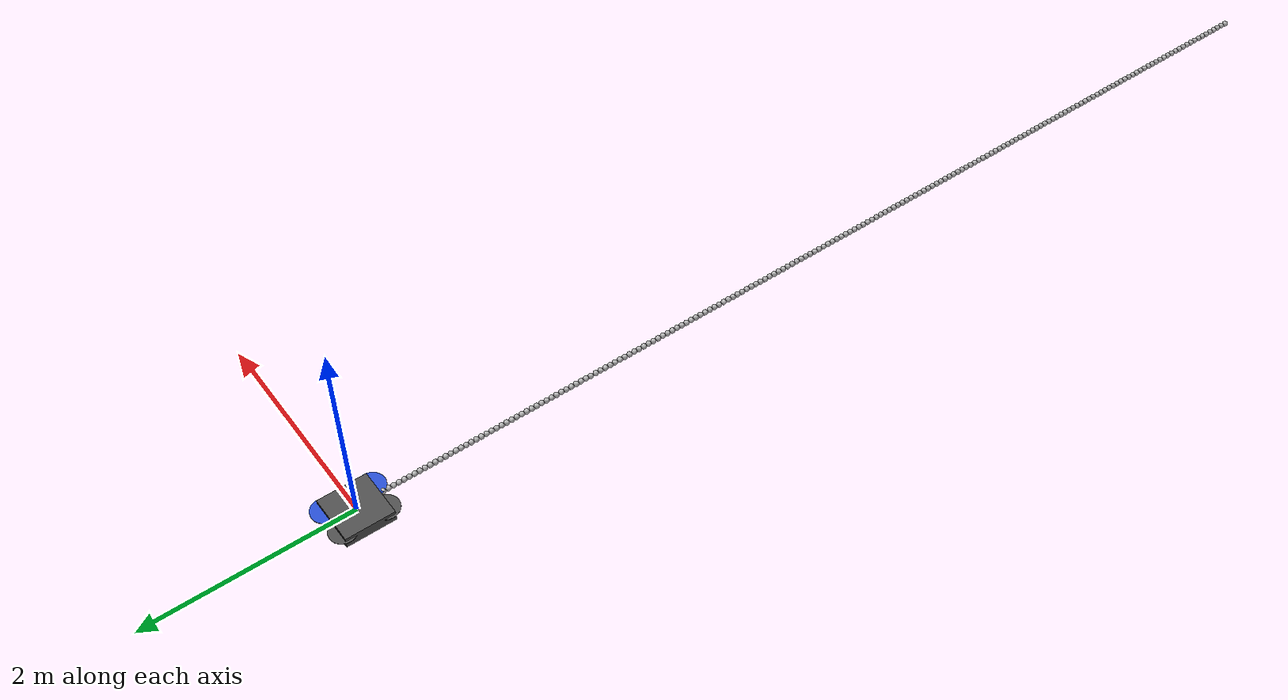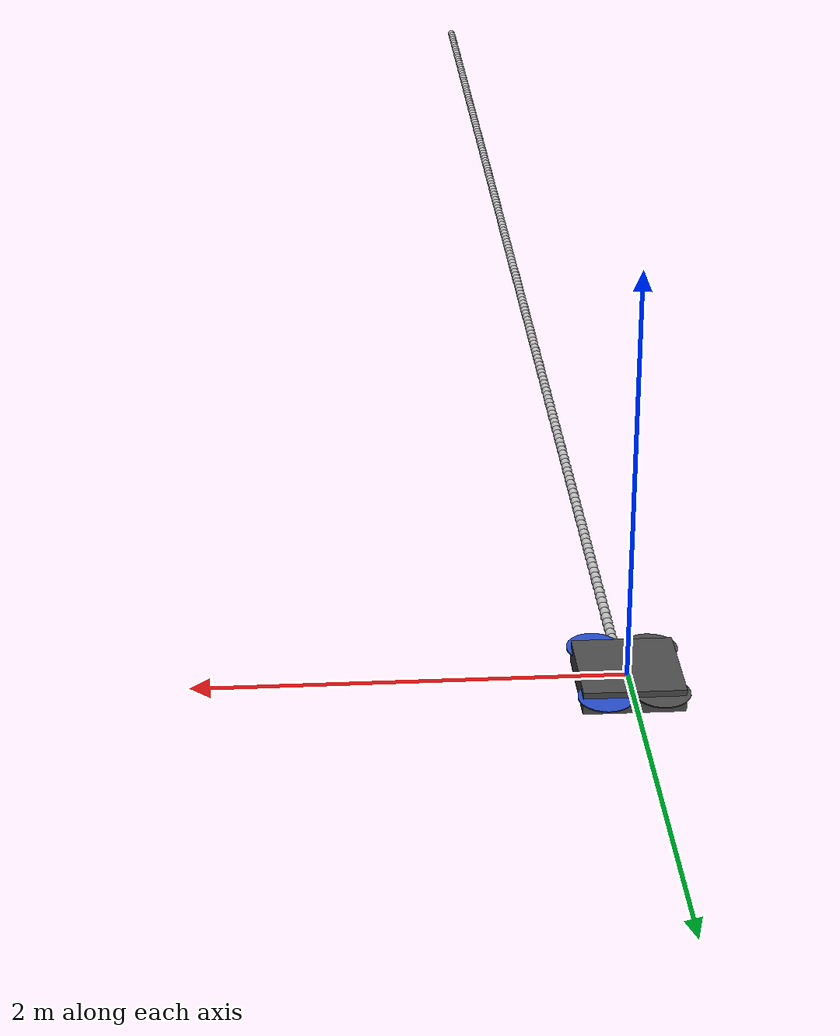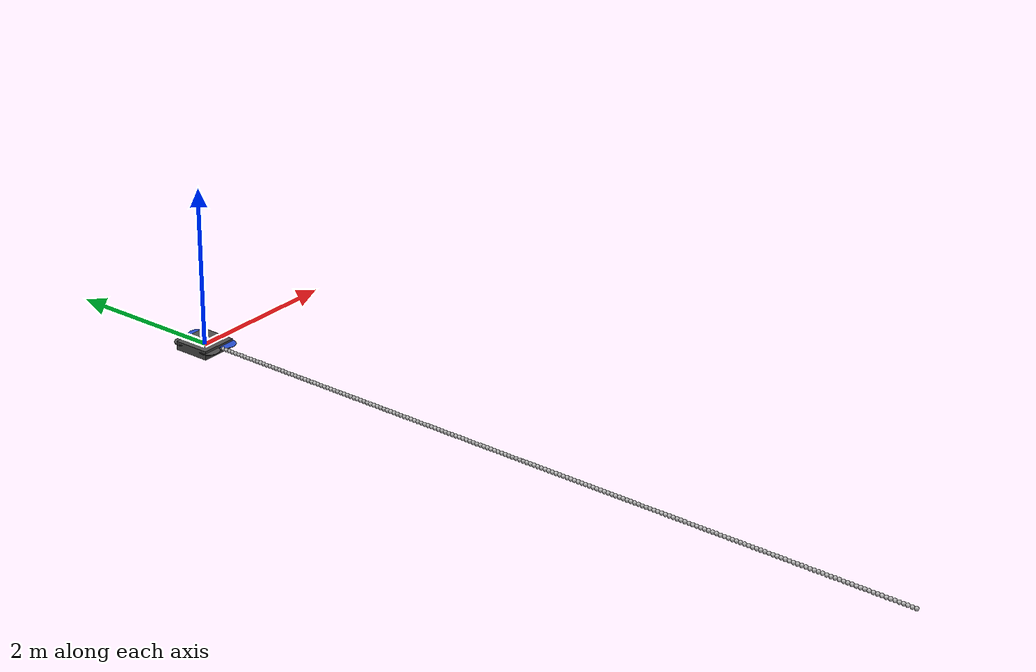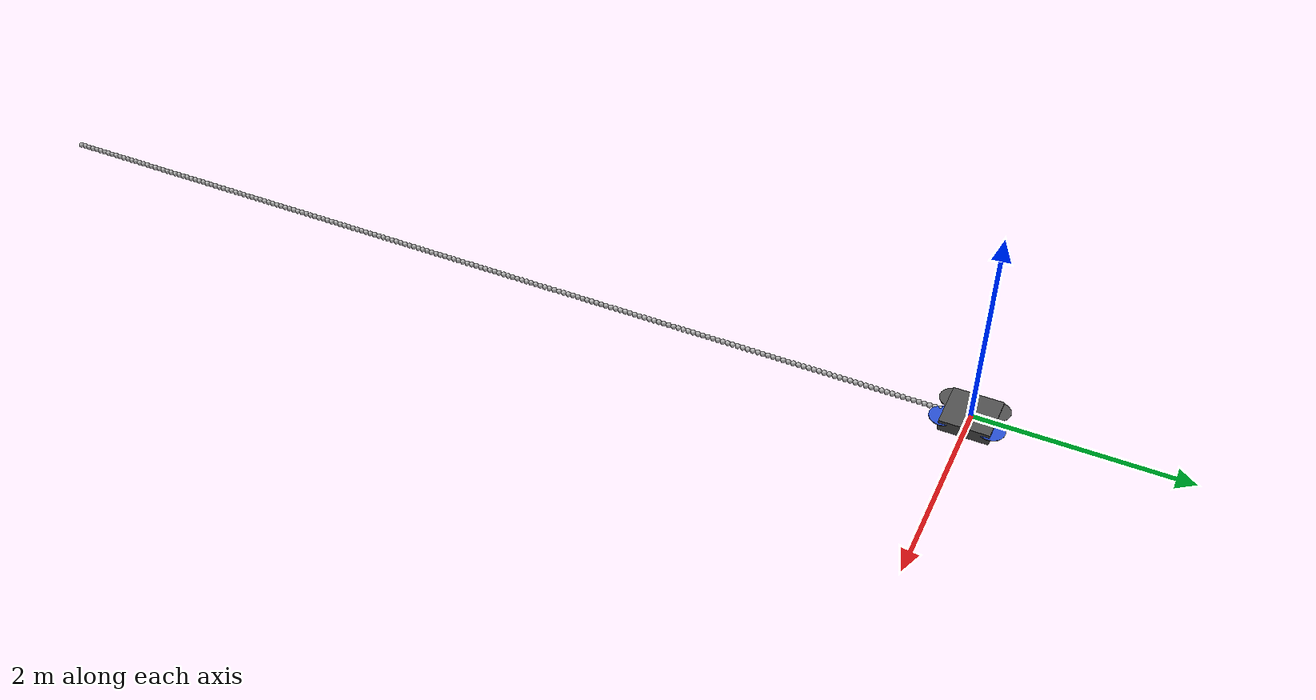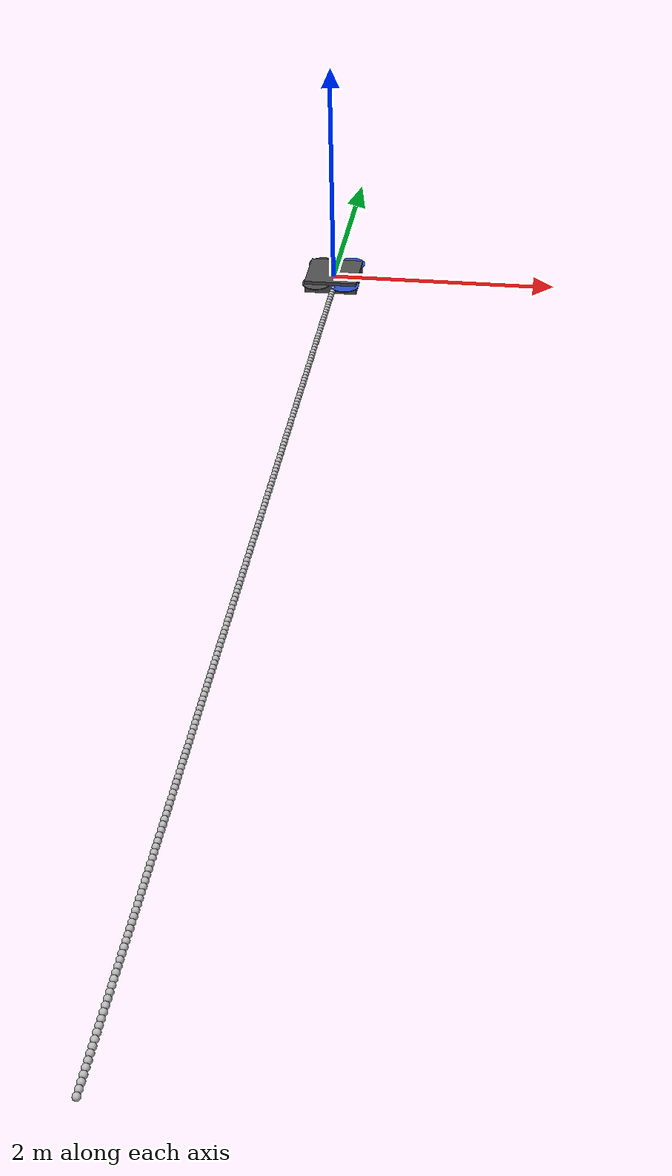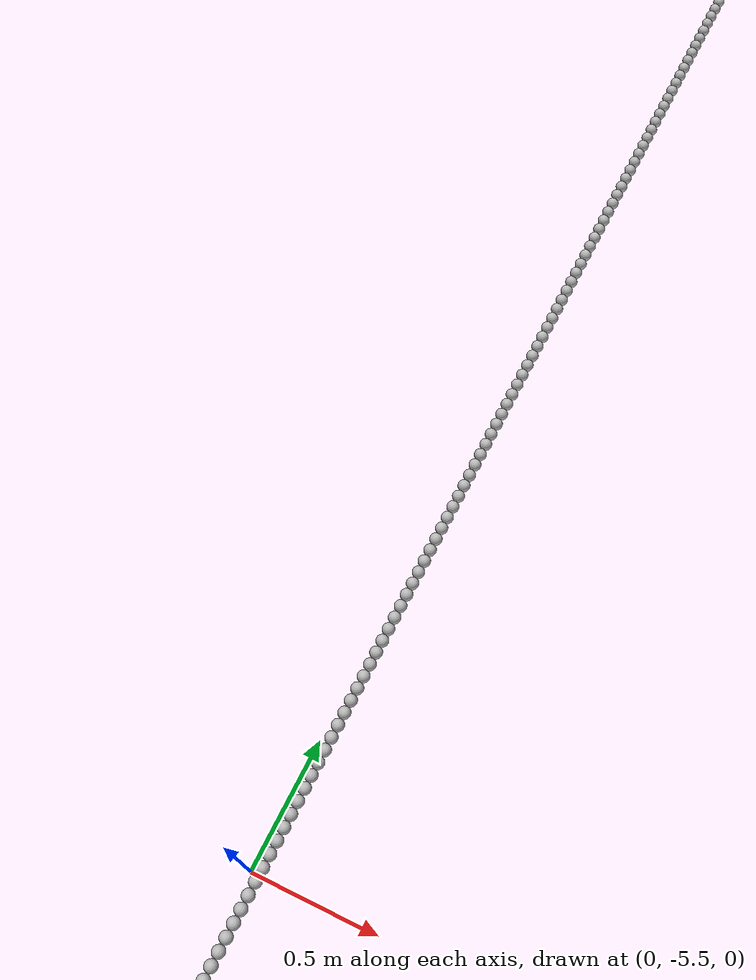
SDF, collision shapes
<?xml version='1.0'?>
<sdf version='1.6'>
  <model name='iris'>
    <link name='base_link'>
      <pose frame=''>0 0 0 0 -0 0</pose>
      <inertial>
        <pose frame=''>0 0 0 0 -0 0</pose>
        <mass>1.5</mass>
        <inertia>
          <ixx>0.029125</ixx>
          <ixy>0</ixy>
          <ixz>0</ixz>
          <iyy>0.029125</iyy>
          <iyz>0</iyz>
          <izz>0.055225</izz>
        </inertia>
      </inertial>
      <gravity>1</gravity>
      <velocity_decay/>
      <self_collide>0</self_collide>
      <enable_wind>0</enable_wind>
      <kinematic>0</kinematic>
      <visual name='base_link_inertia_visual'>
        <pose frame=''>0 0 0 0 -0 0</pose>
        <geometry>
          <mesh>
            <scale>1 1 1</scale>
            <uri>model://rotors_description/meshes/iris.stl</uri>
          </mesh>
        </geometry>
        <material>
          <script>
            <name>Gazebo/DarkGrey</name>
            <uri>file://media/materials/scripts/gazebo.material</uri>
          </script>
          <shader type='pixel'/>
          <emissive>0 0 0 1</emissive>
        </material>
        <transparency>0</transparency>
        <cast_shadows>1</cast_shadows>
      </visual>
      <collision name='base_link_inertia_collision'>
        <laser_retro>0</laser_retro>
        <max_contacts>10</max_contacts>
        <pose frame=''>0 0 0 0 -0 0</pose>
        <geometry>
          <box>
            <size>0.47 0.47 0.11</size>
          </box>
        </geometry>
        <surface>
          <friction>
            <ode>
              <mu>1</mu>
              <mu2>1</mu2>
              <fdir1>0 0 0</fdir1>
              <slip1>0</slip1>
              <slip2>0</slip2>
            </ode>
            <torsional>
              <coefficient>1</coefficient>
              <patch_radius>0</patch_radius>
              <surface_radius>0</surface_radius>
              <use_patch_radius>1</use_patch_radius>
              <ode>
                <slip>0</slip>
              </ode>
            </torsional>
          </friction>
          <bounce>
            <restitution_coefficient>0</restitution_coefficient>
            <threshold>1e+06</threshold>
          </bounce>
          <contact>
            <collide_without_contact>0</collide_without_contact>
            <collide_without_contact_bitmask>1</collide_without_contact_bitmask>
            <collide_bitmask>1</collide_bitmask>
            <ode>
              <soft_cfm>0</soft_cfm>
              <soft_erp>0.2</soft_erp>
              <kp>1e+13</kp>
              <kd>1</kd>
              <max_vel>0</max_vel>
              <min_depth>0.001</min_depth>
            </ode>
            <bullet>
              <split_impulse>1</split_impulse>
              <split_impulse_penetration_threshold>-0.01</split_impulse_penetration_threshold>
              <soft_cfm>0</soft_cfm>
              <soft_erp>0.2</soft_erp>
              <kp>1e+13</kp>
              <kd>1</kd>
            </bullet>
          </contact>
        </surface>
      </collision>
    </link>
    <link name='/imu_link'>
      <pose frame=''>0 0 0 0 -0 0</pose>
      <inertial>
        <pose frame=''>0 0 0 0 -0 0</pose>
        <mass>0.015</mass>
        <inertia>
          <ixx>1e-05</ixx>
          <ixy>0</ixy>
          <ixz>0</ixz>
          <iyy>1e-05</iyy>
          <iyz>0</iyz>
          <izz>1e-05</izz>
        </inertia>
      </inertial>
      <self_collide>0</self_collide>
      <enable_wind>0</enable_wind>
      <kinematic>0</kinematic>
    </link>
    <link name='rotor_0'>
      <pose frame=''>0.13 -0.22 0.023 0 -0 0</pose>
      <inertial>
        <pose frame=''>0 0 0 0 -0 0</pose>
        <mass>0.005</mass>
        <inertia>
          <ixx>9.75e-07</ixx>
          <ixy>0</ixy>
          <ixz>0</ixz>
          <iyy>0.000273104</iyy>
          <iyz>0</iyz>
          <izz>0.000274004</izz>
        </inertia>
      </inertial>
      <gravity>1</gravity>
      <velocity_decay/>
      <self_collide>0</self_collide>
      <enable_wind>0</enable_wind>
      <kinematic>0</kinematic>
      <visual name='rotor_0_visual'>
        <pose frame=''>0 0 0 0 -0 0</pose>
        <geometry>
          <mesh>
            <scale>1 1 1</scale>
            <uri>model://rotors_description/meshes/iris_prop_ccw.dae</uri>
          </mesh>
        </geometry>
        <material>
          <script>
            <name>Gazebo/Blue</name>
            <uri>file://media/materials/scripts/gazebo.material</uri>
          </script>
          <shader type='pixel'/>
        </material>
        <transparency>0</transparency>
        <cast_shadows>1</cast_shadows>
      </visual>
      <collision name='rotor_0_collision'>
        <laser_retro>0</laser_retro>
        <max_contacts>10</max_contacts>
        <pose frame=''>0 0 0 0 -0 0</pose>
        <geometry>
          <cylinder>
            <radius>0.128</radius>
            <length>0.005</length>
          </cylinder>
        </geometry>
        <surface>
          <friction>
            <ode>
              <mu>1</mu>
              <mu2>1</mu2>
              <fdir1>0 0 0</fdir1>
              <slip1>0</slip1>
              <slip2>0</slip2>
            </ode>
            <torsional>
              <coefficient>1</coefficient>
              <patch_radius>0</patch_radius>
              <surface_radius>0</surface_radius>
              <use_patch_radius>1</use_patch_radius>
              <ode>
                <slip>0</slip>
              </ode>
            </torsional>
          </friction>
          <bounce>
            <restitution_coefficient>0</restitution_coefficient>
            <threshold>1e+06</threshold>
          </bounce>
          <contact>
            <collide_without_contact>0</collide_without_contact>
            <collide_without_contact_bitmask>1</collide_without_contact_bitmask>
            <collide_bitmask>1</collide_bitmask>
            <ode>
              <soft_cfm>0</soft_cfm>
              <soft_erp>0.2</soft_erp>
              <kp>1e+13</kp>
              <kd>1</kd>
              <max_vel>0.01</max_vel>
              <min_depth>0</min_depth>
            </ode>
            <bullet>
              <split_impulse>1</split_impulse>
              <split_impulse_penetration_threshold>-0.01</split_impulse_penetration_threshold>
              <soft_cfm>0</soft_cfm>
              <soft_erp>0.2</soft_erp>
              <kp>1e+13</kp>
              <kd>1</kd>
            </bullet>
          </contact>
        </surface>
      </collision>
    </link>
    <link name='rotor_1'>
      <pose frame=''>-0.13 0.2 0.023 0 -0 0</pose>
      <inertial>
        <pose frame=''>0 0 0 0 -0 0</pose>
        <mass>0.005</mass>
        <inertia>
          <ixx>9.75e-07</ixx>
          <ixy>0</ixy>
          <ixz>0</ixz>
          <iyy>0.000273104</iyy>
          <iyz>0</iyz>
          <izz>0.000274004</izz>
        </inertia>
      </inertial>
      <gravity>1</gravity>
      <velocity_decay/>
      <self_collide>0</self_collide>
      <enable_wind>0</enable_wind>
      <kinematic>0</kinematic>
      <visual name='rotor_1_visual'>
        <pose frame=''>0 0 0 0 -0 0</pose>
        <geometry>
          <mesh>
            <scale>1 1 1</scale>
            <uri>model://rotors_description/meshes/iris_prop_ccw.dae</uri>
          </mesh>
        </geometry>
        <material>
          <script>
            <name>Gazebo/DarkGrey</name>
            <uri>file://media/materials/scripts/gazebo.material</uri>
          </script>
          <shader type='pixel'/>
        </material>
        <transparency>0</transparency>
        <cast_shadows>1</cast_shadows>
      </visual>
      <collision name='rotor_1_collision'>
        <laser_retro>0</laser_retro>
        <max_contacts>10</max_contacts>
        <pose frame=''>0 0 0 0 -0 0</pose>
        <geometry>
          <cylinder>
            <radius>0.128</radius>
            <length>0.005</length>
          </cylinder>
        </geometry>
        <surface>
          <friction>
            <ode>
              <mu>1</mu>
              <mu2>1</mu2>
              <fdir1>0 0 0</fdir1>
              <slip1>0</slip1>
              <slip2>0</slip2>
            </ode>
            <torsional>
              <coefficient>1</coefficient>
              <patch_radius>0</patch_radius>
              <surface_radius>0</surface_radius>
              <use_patch_radius>1</use_patch_radius>
              <ode>
                <slip>0</slip>
              </ode>
            </torsional>
          </friction>
          <bounce>
            <restitution_coefficient>0</restitution_coefficient>
            <threshold>1e+06</threshold>
          </bounce>
          <contact>
            <collide_without_contact>0</collide_without_contact>
            <collide_without_contact_bitmask>1</collide_without_contact_bitmask>
            <collide_bitmask>1</collide_bitmask>
            <ode>
              <soft_cfm>0</soft_cfm>
              <soft_erp>0.2</soft_erp>
              <kp>1e+13</kp>
              <kd>1</kd>
              <max_vel>0.01</max_vel>
              <min_depth>0</min_depth>
            </ode>
            <bullet>
              <split_impulse>1</split_impulse>
              <split_impulse_penetration_threshold>-0.01</split_impulse_penetration_threshold>
              <soft_cfm>0</soft_cfm>
              <soft_erp>0.2</soft_erp>
              <kp>1e+13</kp>
              <kd>1</kd>
            </bullet>
          </contact>
        </surface>
      </collision>
    </link>
    <link name='rotor_2'>
      <pose frame=''>0.13 0.22 0.023 0 -0 0</pose>
      <inertial>
        <pose frame=''>0 0 0 0 -0 0</pose>
        <mass>0.005</mass>
        <inertia>
          <ixx>9.75e-07</ixx>
          <ixy>0</ixy>
          <ixz>0</ixz>
          <iyy>0.000273104</iyy>
          <iyz>0</iyz>
          <izz>0.000274004</izz>
        </inertia>
      </inertial>
      <gravity>1</gravity>
      <velocity_decay/>
      <self_collide>0</self_collide>
      <enable_wind>0</enable_wind>
      <kinematic>0</kinematic>
      <visual name='rotor_2_visual'>
        <pose frame=''>0 0 0 0 -0 0</pose>
        <geometry>
          <mesh>
            <scale>1 1 1</scale>
            <uri>model://rotors_description/meshes/iris_prop_cw.dae</uri>
          </mesh>
        </geometry>
        <material>
          <script>
            <name>Gazebo/Blue</name>
            <uri>file://media/materials/scripts/gazebo.material</uri>
          </script>
          <shader type='pixel'/>
        </material>
        <transparency>0</transparency>
        <cast_shadows>1</cast_shadows>
      </visual>
      <collision name='rotor_2_collision'>
        <laser_retro>0</laser_retro>
        <max_contacts>10</max_contacts>
        <pose frame=''>0 0 0 0 -0 0</pose>
        <geometry>
          <cylinder>
            <radius>0.128</radius>
            <length>0.005</length>
          </cylinder>
        </geometry>
        <surface>
          <friction>
            <ode>
              <mu>1</mu>
              <mu2>1</mu2>
              <fdir1>0 0 0</fdir1>
              <slip1>0</slip1>
              <slip2>0</slip2>
            </ode>
            <torsional>
              <coefficient>1</coefficient>
              <patch_radius>0</patch_radius>
              <surface_radius>0</surface_radius>
              <use_patch_radius>1</use_patch_radius>
              <ode>
                <slip>0</slip>
              </ode>
            </torsional>
          </friction>
          <bounce>
            <restitution_coefficient>0</restitution_coefficient>
            <threshold>1e+06</threshold>
          </bounce>
          <contact>
            <collide_without_contact>0</collide_without_contact>
            <collide_without_contact_bitmask>1</collide_without_contact_bitmask>
            <collide_bitmask>1</collide_bitmask>
            <ode>
              <soft_cfm>0</soft_cfm>
              <soft_erp>0.2</soft_erp>
              <kp>1e+13</kp>
              <kd>1</kd>
              <max_vel>0.01</max_vel>
              <min_depth>0</min_depth>
            </ode>
            <bullet>
              <split_impulse>1</split_impulse>
              <split_impulse_penetration_threshold>-0.01</split_impulse_penetration_threshold>
              <soft_cfm>0</soft_cfm>
              <soft_erp>0.2</soft_erp>
              <kp>1e+13</kp>
              <kd>1</kd>
            </bullet>
          </contact>
        </surface>
      </collision>
    </link>
    <link name='rotor_3'>
      <pose frame=''>-0.13 -0.2 0.023 0 -0 0</pose>
      <inertial>
        <pose frame=''>0 0 0 0 -0 0</pose>
        <mass>0.005</mass>
        <inertia>
          <ixx>9.75e-07</ixx>
          <ixy>0</ixy>
          <ixz>0</ixz>
          <iyy>0.000273104</iyy>
          <iyz>0</iyz>
          <izz>0.000274004</izz>
        </inertia>
      </inertial>
      <gravity>1</gravity>
      <velocity_decay/>
      <self_collide>0</self_collide>
      <enable_wind>0</enable_wind>
      <kinematic>0</kinematic>
      <visual name='rotor_3_visual'>
        <pose frame=''>0 0 0 0 -0 0</pose>
        <geometry>
          <mesh>
            <scale>1 1 1</scale>
            <uri>model://rotors_description/meshes/iris_prop_cw.dae</uri>
          </mesh>
        </geometry>
        <material>
          <script>
            <name>Gazebo/DarkGrey</name>
            <uri>file://media/materials/scripts/gazebo.material</uri>
          </script>
          <shader type='pixel'/>
        </material>
        <transparency>0</transparency>
        <cast_shadows>1</cast_shadows>
      </visual>
      <collision name='rotor_3_collision'>
        <laser_retro>0</laser_retro>
        <max_contacts>10</max_contacts>
        <pose frame=''>0 0 0 0 -0 0</pose>
        <geometry>
          <cylinder>
            <radius>0.128</radius>
            <length>0.005</length>
          </cylinder>
        </geometry>
        <surface>
          <friction>
            <ode>
              <mu>1</mu>
              <mu2>1</mu2>
              <fdir1>0 0 0</fdir1>
              <slip1>0</slip1>
              <slip2>0</slip2>
            </ode>
            <torsional>
              <coefficient>1</coefficient>
              <patch_radius>0</patch_radius>
              <surface_radius>0</surface_radius>
              <use_patch_radius>1</use_patch_radius>
              <ode>
                <slip>0</slip>
              </ode>
            </torsional>
          </friction>
          <bounce>
            <restitution_coefficient>0</restitution_coefficient>
            <threshold>1e+06</threshold>
          </bounce>
          <contact>
            <collide_without_contact>0</collide_without_contact>
            <collide_without_contact_bitmask>1</collide_without_contact_bitmask>
            <collide_bitmask>1</collide_bitmask>
            <ode>
              <soft_cfm>0</soft_cfm>
              <soft_erp>0.2</soft_erp>
              <kp>1e+13</kp>
              <kd>1</kd>
              <max_vel>0.01</max_vel>
              <min_depth>0</min_depth>
            </ode>
            <bullet>
              <split_impulse>1</split_impulse>
              <split_impulse_penetration_threshold>-0.01</split_impulse_penetration_threshold>
              <soft_cfm>0</soft_cfm>
              <soft_erp>0.2</soft_erp>
              <kp>1e+13</kp>
              <kd>1</kd>
            </bullet>
          </contact>
        </surface>
      </collision>
    </link>
    <model name='my_rope'>
      <model name='fastening'>
        <link name='link'>
          <inertial>
            <mass>1000</mass>
            <inertia>
              <ixx>0.166667</ixx>
              <ixy>0</ixy>
              <ixz>0</ixz>
              <iyy>0.166667</iyy>
              <iyz>0</iyz>
              <izz>0.166667</izz>
            </inertia>
            <pose frame=''>0 0 0 0 -0 0</pose>
          </inertial>
          <self_collide>0</self_collide>
          <enable_wind>0</enable_wind>
          <kinematic>0</kinematic>
          <pose frame=''>0 0 0 0 -0 0</pose>
          <gravity>1</gravity>
          <visual name='visual'>
            <geometry>
              <box>
                <size>0.1 0.1 0.1</size>
              </box>
            </geometry>
            <material>
              <shader type='pixel'>
                <normal_map>__default__</normal_map>
              </shader>
              <ambient>0.3 0.3 0.3 1</ambient>
              <diffuse>0.7 0.7 0.7 1</diffuse>
              <specular>0.01 0.01 0.01 1</specular>
              <emissive>0 0 0 1</emissive>
            </material>
            <pose frame=''>0 0 0 0 -0 0</pose>
            <transparency>0</transparency>
            <cast_shadows>1</cast_shadows>
          </visual>
          <collision name='collision'>
            <laser_retro>0</laser_retro>
            <max_contacts>10</max_contacts>
            <pose frame=''>0 0 0 0 -0 0</pose>
            <geometry>
              <box>
                <size>0.008427 0.007421 0.009779</size>
              </box>
            </geometry>
            <surface>
              <friction>
                <ode>
                  <mu>1</mu>
                  <mu2>1</mu2>
                  <fdir1>0 0 0</fdir1>
                  <slip1>0</slip1>
                  <slip2>0</slip2>
                </ode>
                <torsional>
                  <coefficient>1</coefficient>
                  <patch_radius>0</patch_radius>
                  <surface_radius>0</surface_radius>
                  <use_patch_radius>1</use_patch_radius>
                  <ode>
                    <slip>0</slip>
                  </ode>
                </torsional>
              </friction>
              <bounce>
                <restitution_coefficient>0</restitution_coefficient>
                <threshold>1e+06</threshold>
              </bounce>
              <contact>
                <collide_without_contact>0</collide_without_contact>
                <collide_without_contact_bitmask>1</collide_without_contact_bitmask>
                <collide_bitmask>1</collide_bitmask>
                <ode>
                  <soft_cfm>0</soft_cfm>
                  <soft_erp>0.2</soft_erp>
                  <kp>1e+13</kp>
                  <kd>1</kd>
                  <max_vel>0.01</max_vel>
                  <min_depth>0</min_depth>
                </ode>
                <bullet>
                  <split_impulse>1</split_impulse>
                  <split_impulse_penetration_threshold>-0.01</split_impulse_penetration_threshold>
                  <soft_cfm>0</soft_cfm>
                  <soft_erp>0.2</soft_erp>
                  <kp>1e+13</kp>
                  <kd>1</kd>
                </bullet>
              </contact>
            </surface>
          </collision>
        </link>
        <static>0</static>
        <allow_auto_disable>1</allow_auto_disable>
        <pose frame=''>0 0 0 0 -0 0</pose>
      </model>
      <model name='ball_bearing_0'>
        <link name='link'>
          <pose frame=''>0 0 0.003 0 -0 0</pose>
          <inertial>
            <mass>1.1e-09</mass>
            <inertia>
              <ixx>3.96e-09</ixx>
              <ixy>0</ixy>
              <ixz>0</ixz>
              <iyy>3.96e-09</iyy>
              <iyz>0</iyz>
              <izz>3.96e-09</izz>
            </inertia>
          </inertial>
          <collision name='collision'>
            <geometry>
              <sphere>
                <radius>0.025</radius>
              </sphere>
            </geometry>
            <surface>
              <contact>
                <poissons_ratio>0.305</poissons_ratio>
                <elastic_modulus>2e+11</elastic_modulus>
                <ode>
                  <kp>100000</kp>
                  <kd>100</kd>
                  <max_vel>100</max_vel>
                  <min_depth>0.001</min_depth>
                </ode>
              </contact>
              <friction>
                <torsional>
                  <coefficient>1</coefficient>
                  <use_patch_radius>0</use_patch_radius>
                  <surface_radius>0.01</surface_radius>
                </torsional>
              </friction>
            </surface>
          </collision>
          <visual name='visual'>
            <geometry>
              <sphere>
                <radius>0.025</radius>
              </sphere>
            </geometry>
          </visual>
          <velocity_decay>
            <linear>0</linear>
            <angular>0.005</angular>
          </velocity_decay>
        </link>
        <pose frame=''>0 0 0 0 -0 0</pose>
      </model>
      <model name='ball_bearing_1'>
        <link name='link'>
          <pose frame=''>0 0 0.003 0 -0 0</pose>
          <inertial>
            <mass>1.1e-09</mass>
            <inertia>
              <ixx>3.96e-09</ixx>
              <ixy>0</ixy>
              <ixz>0</ixz>
              <iyy>3.96e-09</iyy>
              <iyz>0</iyz>
              <izz>3.96e-09</izz>
            </inertia>
          </inertial>
          <collision name='collision'>
            <geometry>
              <sphere>
                <radius>0.025</radius>
              </sphere>
            </geometry>
            <surface>
              <contact>
                <poissons_ratio>0.305</poissons_ratio>
                <elastic_modulus>2e+11</elastic_modulus>
                <ode>
                  <kp>100000</kp>
                  <kd>100</kd>
                  <max_vel>100</max_vel>
                  <min_depth>0.001</min_depth>
                </ode>
              </contact>
              <friction>
                <torsional>
                  <coefficient>1</coefficient>
                  <use_patch_radius>0</use_patch_radius>
                  <surface_radius>0.01</surface_radius>
                </torsional>
              </friction>
            </surface>
          </collision>
          <visual name='visual'>
            <geometry>
              <sphere>
                <radius>0.025</radius>
              </sphere>
            </geometry>
          </visual>
          <velocity_decay>
            <linear>0</linear>
            <angular>0.005</angular>
          </velocity_decay>
        </link>
        <pose frame=''>0 0.05 0 0 -0 0</pose>
      </model>
      <model name='ball_bearing_2'>
        <link name='link'>
          <pose frame=''>0 0 0.003 0 -0 0</pose>
          <inertial>
            <mass>1.1e-09</mass>
            <inertia>
              <ixx>3.96e-09</ixx>
              <ixy>0</ixy>
              <ixz>0</ixz>
              <iyy>3.96e-09</iyy>
              <iyz>0</iyz>
              <izz>3.96e-09</izz>
            </inertia>
          </inertial>
          <collision name='collision'>
            <geometry>
              <sphere>
                <radius>0.025</radius>
              </sphere>
            </geometry>
            <surface>
              <contact>
                <poissons_ratio>0.305</poissons_ratio>
                <elastic_modulus>2e+11</elastic_modulus>
                <ode>
                  <kp>100000</kp>
                  <kd>100</kd>
                  <max_vel>100</max_vel>
                  <min_depth>0.001</min_depth>
                </ode>
              </contact>
              <friction>
                <torsional>
                  <coefficient>1</coefficient>
                  <use_patch_radius>0</use_patch_radius>
                  <surface_radius>0.01</surface_radius>
                </torsional>
              </friction>
            </surface>
          </collision>
          <visual name='visual'>
            <geometry>
              <sphere>
                <radius>0.025</radius>
              </sphere>
            </geometry>
          </visual>
          <velocity_decay>
            <linear>0</linear>
            <angular>0.005</angular>
          </velocity_decay>
        </link>
        <pose frame=''>0 0.1 0 0 -0 0</pose>
      </model>
      <model name='ball_bearing_3'>
        <link name='link'>
          <pose frame=''>0 0 0.003 0 -0 0</pose>
          <inertial>
            <mass>1.1e-09</mass>
            <inertia>
              <ixx>3.96e-09</ixx>
              <ixy>0</ixy>
              <ixz>0</ixz>
              <iyy>3.96e-09</iyy>
              <iyz>0</iyz>
              <izz>3.96e-09</izz>
            </inertia>
          </inertial>
          <collision name='collision'>
            <geometry>
              <sphere>
                <radius>0.025</radius>
              </sphere>
            </geometry>
            <surface>
              <contact>
                <poissons_ratio>0.305</poissons_ratio>
                <elastic_modulus>2e+11</elastic_modulus>
                <ode>
                  <kp>100000</kp>
                  <kd>100</kd>
                  <max_vel>100</max_vel>
                  <min_depth>0.001</min_depth>
                </ode>
              </contact>
              <friction>
                <torsional>
                  <coefficient>1</coefficient>
                  <use_patch_radius>0</use_patch_radius>
                  <surface_radius>0.01</surface_radius>
                </torsional>
              </friction>
            </surface>
          </collision>
          <visual name='visual'>
            <geometry>
              <sphere>
                <radius>0.025</radius>
              </sphere>
            </geometry>
          </visual>
          <velocity_decay>
            <linear>0</linear>
            <angular>0.005</angular>
          </velocity_decay>
        </link>
        <pose frame=''>0 0.15 0 0 -0 0</pose>
      </model>
      <model name='ball_bearing_4'>
        <link name='link'>
          <pose frame=''>0 0 0.003 0 -0 0</pose>
          <inertial>
            <mass>1.1e-09</mass>
            <inertia>
              <ixx>3.96e-09</ixx>
              <ixy>0</ixy>
              <ixz>0</ixz>
              <iyy>3.96e-09</iyy>
              <iyz>0</iyz>
              <izz>3.96e-09</izz>
            </inertia>
          </inertial>
          <collision name='collision'>
            <geometry>
              <sphere>
                <radius>0.025</radius>
              </sphere>
            </geometry>
            <surface>
              <contact>
                <poissons_ratio>0.305</poissons_ratio>
                <elastic_modulus>2e+11</elastic_modulus>
                <ode>
                  <kp>100000</kp>
                  <kd>100</kd>
                  <max_vel>100</max_vel>
                  <min_depth>0.001</min_depth>
                </ode>
              </contact>
              <friction>
                <torsional>
                  <coefficient>1</coefficient>
                  <use_patch_radius>0</use_patch_radius>
                  <surface_radius>0.01</surface_radius>
                </torsional>
              </friction>
            </surface>
          </collision>
          <visual name='visual'>
            <geometry>
              <sphere>
                <radius>0.025</radius>
              </sphere>
            </geometry>
          </visual>
          <velocity_decay>
            <linear>0</linear>
            <angular>0.005</angular>
          </velocity_decay>
        </link>
        <pose frame=''>0 0.2 0 0 -0 0</pose>
      </model>
      <model name='ball_bearing_5'>
        <link name='link'>
          <pose frame=''>0 0 0.003 0 -0 0</pose>
          <inertial>
            <mass>1.1e-09</mass>
            <inertia>
              <ixx>3.96e-09</ixx>
              <ixy>0</ixy>
              <ixz>0</ixz>
              <iyy>3.96e-09</iyy>
              <iyz>0</iyz>
              <izz>3.96e-09</izz>
            </inertia>
          </inertial>
          <collision name='collision'>
            <geometry>
              <sphere>
                <radius>0.025</radius>
              </sphere>
            </geometry>
            <surface>
              <contact>
                <poissons_ratio>0.305</poissons_ratio>
                <elastic_modulus>2e+11</elastic_modulus>
                <ode>
                  <kp>100000</kp>
                  <kd>100</kd>
                  <max_vel>100</max_vel>
                  <min_depth>0.001</min_depth>
                </ode>
              </contact>
              <friction>
                <torsional>
                  <coefficient>1</coefficient>
                  <use_patch_radius>0</use_patch_radius>
                  <surface_radius>0.01</surface_radius>
                </torsional>
              </friction>
            </surface>
          </collision>
          <visual name='visual'>
            <geometry>
              <sphere>
                <radius>0.025</radius>
              </sphere>
            </geometry>
          </visual>
          <velocity_decay>
            <linear>0</linear>
            <angular>0.005</angular>
          </velocity_decay>
        </link>
        <pose frame=''>0 0.25 0 0 -0 0</pose>
      </model>
      <model name='ball_bearing_6'>
        <link name='link'>
          <pose frame=''>0 0 0.003 0 -0 0</pose>
          <inertial>
            <mass>1.1e-09</mass>
            <inertia>
              <ixx>3.96e-09</ixx>
              <ixy>0</ixy>
              <ixz>0</ixz>
              <iyy>3.96e-09</iyy>
              <iyz>0</iyz>
              <izz>3.96e-09</izz>
            </inertia>
          </inertial>
          <collision name='collision'>
            <geometry>
              <sphere>
                <radius>0.025</radius>
              </sphere>
            </geometry>
            <surface>
              <contact>
                <poissons_ratio>0.305</poissons_ratio>
                <elastic_modulus>2e+11</elastic_modulus>
                <ode>
                  <kp>100000</kp>
                  <kd>100</kd>
                  <max_vel>100</max_vel>
                  <min_depth>0.001</min_depth>
                </ode>
              </contact>
              <friction>
                <torsional>
                  <coefficient>1</coefficient>
                  <use_patch_radius>0</use_patch_radius>
                  <surface_radius>0.01</surface_radius>
                </torsional>
              </friction>
            </surface>
          </collision>
          <visual name='visual'>
            <geometry>
              <sphere>
                <radius>0.025</radius>
              </sphere>
            </geometry>
          </visual>
          <velocity_decay>
            <linear>0</linear>
            <angular>0.005</angular>
          </velocity_decay>
        </link>
        <pose frame=''>0 0.3 0 0 -0 0</pose>
      </model>
      <model name='ball_bearing_7'>
        <link name='link'>
          <pose frame=''>0 0 0.003 0 -0 0</pose>
          <inertial>
            <mass>1.1e-09</mass>
            <inertia>
              <ixx>3.96e-09</ixx>
              <ixy>0</ixy>
              <ixz>0</ixz>
              <iyy>3.96e-09</iyy>
              <iyz>0</iyz>
              <izz>3.96e-09</izz>
            </inertia>
          </inertial>
          <collision name='collision'>
            <geometry>
              <sphere>
                <radius>0.025</radius>
              </sphere>
            </geometry>
            <surface>
              <contact>
                <poissons_ratio>0.305</poissons_ratio>
                <elastic_modulus>2e+11</elastic_modulus>
                <ode>
                  <kp>100000</kp>
                  <kd>100</kd>
                  <max_vel>100</max_vel>
                  <min_depth>0.001</min_depth>
                </ode>
              </contact>
              <friction>
                <torsional>
                  <coefficient>1</coefficient>
                  <use_patch_radius>0</use_patch_radius>
                  <surface_radius>0.01</surface_radius>
                </torsional>
              </friction>
            </surface>
          </collision>
          <visual name='visual'>
            <geometry>
              <sphere>
                <radius>0.025</radius>
              </sphere>
            </geometry>
          </visual>
          <velocity_decay>
            <linear>0</linear>
            <angular>0.005</angular>
          </velocity_decay>
        </link>
        <pose frame=''>0 0.35 0 0 -0 0</pose>
      </model>
      <model name='ball_bearing_8'>
        <link name='link'>
          <pose frame=''>0 0 0.003 0 -0 0</pose>
          <inertial>
            <mass>1.1e-09</mass>
            <inertia>
              <ixx>3.96e-09</ixx>
              <ixy>0</ixy>
              <ixz>0</ixz>
              <iyy>3.96e-09</iyy>
              <iyz>0</iyz>
              <izz>3.96e-09</izz>
            </inertia>
          </inertial>
          <collision name='collision'>
            <geometry>
              <sphere>
                <radius>0.025</radius>
              </sphere>
            </geometry>
            <surface>
              <contact>
                <poissons_ratio>0.305</poissons_ratio>
                <elastic_modulus>2e+11</elastic_modulus>
                <ode>
                  <kp>100000</kp>
                  <kd>100</kd>
                  <max_vel>100</max_vel>
                  <min_depth>0.001</min_depth>
                </ode>
              </contact>
              <friction>
                <torsional>
                  <coefficient>1</coefficient>
                  <use_patch_radius>0</use_patch_radius>
                  <surface_radius>0.01</surface_radius>
                </torsional>
              </friction>
            </surface>
          </collision>
          <visual name='visual'>
            <geometry>
              <sphere>
                <radius>0.025</radius>
              </sphere>
            </geometry>
          </visual>
          <velocity_decay>
            <linear>0</linear>
            <angular>0.005</angular>
          </velocity_decay>
        </link>
        <pose frame=''>0 0.4 0 0 -0 0</pose>
      </model>
      <model name='ball_bearing_9'>
        <link name='link'>
          <pose frame=''>0 0 0.003 0 -0 0</pose>
          <inertial>
            <mass>1.1e-09</mass>
            <inertia>
              <ixx>3.96e-09</ixx>
              <ixy>0</ixy>
              <ixz>0</ixz>
              <iyy>3.96e-09</iyy>
              <iyz>0</iyz>
              <izz>3.96e-09</izz>
            </inertia>
          </inertial>
          <collision name='collision'>
            <geometry>
              <sphere>
                <radius>0.025</radius>
              </sphere>
            </geometry>
            <surface>
              <contact>
                <poissons_ratio>0.305</poissons_ratio>
                <elastic_modulus>2e+11</elastic_modulus>
                <ode>
                  <kp>100000</kp>
                  <kd>100</kd>
                  <max_vel>100</max_vel>
                  <min_depth>0.001</min_depth>
                </ode>
              </contact>
              <friction>
                <torsional>
                  <coefficient>1</coefficient>
                  <use_patch_radius>0</use_patch_radius>
                  <surface_radius>0.01</surface_radius>
                </torsional>
              </friction>
            </surface>
          </collision>
          <visual name='visual'>
            <geometry>
              <sphere>
                <radius>0.025</radius>
              </sphere>
            </geometry>
          </visual>
          <velocity_decay>
            <linear>0</linear>
            <angular>0.005</angular>
          </velocity_decay>
        </link>
        <pose frame=''>0 0.45 0 0 -0 0</pose>
      </model>
      <model name='ball_bearing_10'>
        <link name='link'>
          <pose frame=''>0 0 0.003 0 -0 0</pose>
          <inertial>
            <mass>1.1e-09</mass>
            <inertia>
              <ixx>3.96e-09</ixx>
              <ixy>0</ixy>
              <ixz>0</ixz>
              <iyy>3.96e-09</iyy>
              <iyz>0</iyz>
              <izz>3.96e-09</izz>
            </inertia>
          </inertial>
          <collision name='collision'>
            <geometry>
              <sphere>
                <radius>0.025</radius>
              </sphere>
            </geometry>
            <surface>
              <contact>
                <poissons_ratio>0.305</poissons_ratio>
                <elastic_modulus>2e+11</elastic_modulus>
                <ode>
                  <kp>100000</kp>
                  <kd>100</kd>
                  <max_vel>100</max_vel>
                  <min_depth>0.001</min_depth>
                </ode>
              </contact>
              <friction>
                <torsional>
                  <coefficient>1</coefficient>
                  <use_patch_radius>0</use_patch_radius>
                  <surface_radius>0.01</surface_radius>
                </torsional>
              </friction>
            </surface>
          </collision>
          <visual name='visual'>
            <geometry>
              <sphere>
                <radius>0.025</radius>
              </sphere>
            </geometry>
          </visual>
          <velocity_decay>
            <linear>0</linear>
            <angular>0.005</angular>
          </velocity_decay>
        </link>
        <pose frame=''>0 0.5 0 0 -0 0</pose>
      </model>
      <model name='ball_bearing_11'>
        <link name='link'>
          <pose frame=''>0 0 0.003 0 -0 0</pose>
          <inertial>
            <mass>1.1e-09</mass>
            <inertia>
              <ixx>3.96e-09</ixx>
              <ixy>0</ixy>
              <ixz>0</ixz>
              <iyy>3.96e-09</iyy>
              <iyz>0</iyz>
              <izz>3.96e-09</izz>
            </inertia>
          </inertial>
          <collision name='collision'>
            <geometry>
              <sphere>
                <radius>0.025</radius>
              </sphere>
            </geometry>
            <surface>
              <contact>
                <poissons_ratio>0.305</poissons_ratio>
                <elastic_modulus>2e+11</elastic_modulus>
                <ode>
                  <kp>100000</kp>
                  <kd>100</kd>
                  <max_vel>100</max_vel>
                  <min_depth>0.001</min_depth>
                </ode>
              </contact>
              <friction>
                <torsional>
                  <coefficient>1</coefficient>
                  <use_patch_radius>0</use_patch_radius>
                  <surface_radius>0.01</surface_radius>
                </torsional>
              </friction>
            </surface>
          </collision>
          <visual name='visual'>
            <geometry>
              <sphere>
                <radius>0.025</radius>
              </sphere>
            </geometry>
          </visual>
          <velocity_decay>
            <linear>0</linear>
            <angular>0.005</angular>
          </velocity_decay>
        </link>
        <pose frame=''>0 0.55 0 0 -0 0</pose>
      </model>
      <model name='ball_bearing_12'>
        <link name='link'>
          <pose frame=''>0 0 0.003 0 -0 0</pose>
          <inertial>
            <mass>1.1e-09</mass>
            <inertia>
              <ixx>3.96e-09</ixx>
              <ixy>0</ixy>
              <ixz>0</ixz>
              <iyy>3.96e-09</iyy>
              <iyz>0</iyz>
              <izz>3.96e-09</izz>
            </inertia>
          </inertial>
          <collision name='collision'>
            <geometry>
              <sphere>
                <radius>0.025</radius>
              </sphere>
            </geometry>
            <surface>
              <contact>
                <poissons_ratio>0.305</poissons_ratio>
                <elastic_modulus>2e+11</elastic_modulus>
                <ode>
                  <kp>100000</kp>
                  <kd>100</kd>
                  <max_vel>100</max_vel>
                  <min_depth>0.001</min_depth>
                </ode>
              </contact>
              <friction>
                <torsional>
                  <coefficient>1</coefficient>
                  <use_patch_radius>0</use_patch_radius>
                  <surface_radius>0.01</surface_radius>
                </torsional>
              </friction>
            </surface>
          </collision>
          <visual name='visual'>
            <geometry>
              <sphere>
                <radius>0.025</radius>
              </sphere>
            </geometry>
          </visual>
          <velocity_decay>
            <linear>0</linear>
            <angular>0.005</angular>
          </velocity_decay>
        </link>
        <pose frame=''>0 0.6 0 0 -0 0</pose>
      </model>
      <model name='ball_bearing_13'>
        <link name='link'>
          <pose frame=''>0 0 0.003 0 -0 0</pose>
          <inertial>
            <mass>1.1e-09</mass>
            <inertia>
              <ixx>3.96e-09</ixx>
              <ixy>0</ixy>
              <ixz>0</ixz>
              <iyy>3.96e-09</iyy>
              <iyz>0</iyz>
              <izz>3.96e-09</izz>
            </inertia>
          </inertial>
          <collision name='collision'>
            <geometry>
              <sphere>
                <radius>0.025</radius>
              </sphere>
            </geometry>
            <surface>
              <contact>
                <poissons_ratio>0.305</poissons_ratio>
                <elastic_modulus>2e+11</elastic_modulus>
                <ode>
                  <kp>100000</kp>
                  <kd>100</kd>
                  <max_vel>100</max_vel>
                  <min_depth>0.001</min_depth>
                </ode>
              </contact>
              <friction>
                <torsional>
                  <coefficient>1</coefficient>
                  <use_patch_radius>0</use_patch_radius>
                  <surface_radius>0.01</surface_radius>
                </torsional>
              </friction>
            </surface>
          </collision>
          <visual name='visual'>
            <geometry>
              <sphere>
                <radius>0.025</radius>
              </sphere>
            </geometry>
          </visual>
          <velocity_decay>
            <linear>0</linear>
            <angular>0.005</angular>
          </velocity_decay>
        </link>
        <pose frame=''>0 0.65 0 0 -0 0</pose>
      </model>
      <model name='ball_bearing_14'>
        <link name='link'>
          <pose frame=''>0 0 0.003 0 -0 0</pose>
          <inertial>
            <mass>1.1e-09</mass>
            <inertia>
              <ixx>3.96e-09</ixx>
              <ixy>0</ixy>
              <ixz>0</ixz>
              <iyy>3.96e-09</iyy>
              <iyz>0</iyz>
              <izz>3.96e-09</izz>
            </inertia>
          </inertial>
          <collision name='collision'>
            <geometry>
              <sphere>
                <radius>0.025</radius>
              </sphere>
            </geometry>
            <surface>
              <contact>
                <poissons_ratio>0.305</poissons_ratio>
                <elastic_modulus>2e+11</elastic_modulus>
                <ode>
                  <kp>100000</kp>
                  <kd>100</kd>
                  <max_vel>100</max_vel>
                  <min_depth>0.001</min_depth>
                </ode>
              </contact>
              <friction>
                <torsional>
                  <coefficient>1</coefficient>
                  <use_patch_radius>0</use_patch_radius>
                  <surface_radius>0.01</surface_radius>
                </torsional>
              </friction>
            </surface>
          </collision>
          <visual name='visual'>
            <geometry>
              <sphere>
                <radius>0.025</radius>
              </sphere>
            </geometry>
          </visual>
          <velocity_decay>
            <linear>0</linear>
            <angular>0.005</angular>
          </velocity_decay>
        </link>
        <pose frame=''>0 0.7 0 0 -0 0</pose>
      </model>
      <model name='ball_bearing_15'>
        <link name='link'>
          <pose frame=''>0 0 0.003 0 -0 0</pose>
          <inertial>
            <mass>1.1e-09</mass>
            <inertia>
              <ixx>3.96e-09</ixx>
              <ixy>0</ixy>
              <ixz>0</ixz>
              <iyy>3.96e-09</iyy>
              <iyz>0</iyz>
              <izz>3.96e-09</izz>
            </inertia>
          </inertial>
          <collision name='collision'>
            <geometry>
              <sphere>
                <radius>0.025</radius>
              </sphere>
            </geometry>
            <surface>
              <contact>
                <poissons_ratio>0.305</poissons_ratio>
                <elastic_modulus>2e+11</elastic_modulus>
                <ode>
                  <kp>100000</kp>
                  <kd>100</kd>
                  <max_vel>100</max_vel>
                  <min_depth>0.001</min_depth>
                </ode>
              </contact>
              <friction>
                <torsional>
                  <coefficient>1</coefficient>
                  <use_patch_radius>0</use_patch_radius>
                  <surface_radius>0.01</surface_radius>
                </torsional>
              </friction>
            </surface>
          </collision>
          <visual name='visual'>
            <geometry>
              <sphere>
                <radius>0.025</radius>
              </sphere>
            </geometry>
          </visual>
          <velocity_decay>
            <linear>0</linear>
            <angular>0.005</angular>
          </velocity_decay>
        </link>
        <pose frame=''>0 0.75 0 0 -0 0</pose>
      </model>
      <model name='ball_bearing_16'>
        <link name='link'>
          <pose frame=''>0 0 0.003 0 -0 0</pose>
          <inertial>
            <mass>1.1e-09</mass>
            <inertia>
              <ixx>3.96e-09</ixx>
              <ixy>0</ixy>
              <ixz>0</ixz>
              <iyy>3.96e-09</iyy>
              <iyz>0</iyz>
              <izz>3.96e-09</izz>
            </inertia>
          </inertial>
          <collision name='collision'>
            <geometry>
              <sphere>
                <radius>0.025</radius>
              </sphere>
            </geometry>
            <surface>
              <contact>
                <poissons_ratio>0.305</poissons_ratio>
                <elastic_modulus>2e+11</elastic_modulus>
                <ode>
                  <kp>100000</kp>
                  <kd>100</kd>
                  <max_vel>100</max_vel>
                  <min_depth>0.001</min_depth>
                </ode>
              </contact>
              <friction>
                <torsional>
                  <coefficient>1</coefficient>
                  <use_patch_radius>0</use_patch_radius>
                  <surface_radius>0.01</surface_radius>
                </torsional>
              </friction>
            </surface>
          </collision>
          <visual name='visual'>
            <geometry>
              <sphere>
                <radius>0.025</radius>
              </sphere>
            </geometry>
          </visual>
          <velocity_decay>
            <linear>0</linear>
            <angular>0.005</angular>
          </velocity_decay>
        </link>
        <pose frame=''>0 0.8 0 0 -0 0</pose>
      </model>
      <model name='ball_bearing_17'>
        <link name='link'>
          <pose frame=''>0 0 0.003 0 -0 0</pose>
          <inertial>
            <mass>1.1e-09</mass>
            <inertia>
              <ixx>3.96e-09</ixx>
              <ixy>0</ixy>
              <ixz>0</ixz>
              <iyy>3.96e-09</iyy>
              <iyz>0</iyz>
              <izz>3.96e-09</izz>
            </inertia>
          </inertial>
          <collision name='collision'>
            <geometry>
              <sphere>
                <radius>0.025</radius>
              </sphere>
            </geometry>
            <surface>
              <contact>
                <poissons_ratio>0.305</poissons_ratio>
                <elastic_modulus>2e+11</elastic_modulus>
                <ode>
                  <kp>100000</kp>
                  <kd>100</kd>
                  <max_vel>100</max_vel>
                  <min_depth>0.001</min_depth>
                </ode>
              </contact>
              <friction>
                <torsional>
                  <coefficient>1</coefficient>
                  <use_patch_radius>0</use_patch_radius>
                  <surface_radius>0.01</surface_radius>
                </torsional>
              </friction>
            </surface>
          </collision>
          <visual name='visual'>
            <geometry>
              <sphere>
                <radius>0.025</radius>
              </sphere>
            </geometry>
          </visual>
          <velocity_decay>
            <linear>0</linear>
            <angular>0.005</angular>
          </velocity_decay>
        </link>
        <pose frame=''>0 0.85 0 0 -0 0</pose>
      </model>
      <model name='ball_bearing_18'>
        <link name='link'>
          <pose frame=''>0 0 0.003 0 -0 0</pose>
          <inertial>
            <mass>1.1e-09</mass>
            <inertia>
              <ixx>3.96e-09</ixx>
              <ixy>0</ixy>
              <ixz>0</ixz>
              <iyy>3.96e-09</iyy>
              <iyz>0</iyz>
              <izz>3.96e-09</izz>
            </inertia>
          </inertial>
          <collision name='collision'>
            <geometry>
              <sphere>
                <radius>0.025</radius>
              </sphere>
            </geometry>
            <surface>
              <contact>
                <poissons_ratio>0.305</poissons_ratio>
                <elastic_modulus>2e+11</elastic_modulus>
                <ode>
                  <kp>100000</kp>
                  <kd>100</kd>
                  <max_vel>100</max_vel>
                  <min_depth>0.001</min_depth>
                </ode>
              </contact>
              <friction>
                <torsional>
                  <coefficient>1</coefficient>
                  <use_patch_radius>0</use_patch_radius>
                  <surface_radius>0.01</surface_radius>
                </torsional>
              </friction>
            </surface>
          </collision>
          <visual name='visual'>
            <geometry>
              <sphere>
                <radius>0.025</radius>
              </sphere>
            </geometry>
          </visual>
          <velocity_decay>
            <linear>0</linear>
            <angular>0.005</angular>
          </velocity_decay>
        </link>
        <pose frame=''>0 0.9 0 0 -0 0</pose>
      </model>
      <model name='ball_bearing_19'>
        <link name='link'>
          <pose frame=''>0 0 0.003 0 -0 0</pose>
          <inertial>
            <mass>1.1e-09</mass>
            <inertia>
              <ixx>3.96e-09</ixx>
              <ixy>0</ixy>
              <ixz>0</ixz>
              <iyy>3.96e-09</iyy>
              <iyz>0</iyz>
              <izz>3.96e-09</izz>
            </inertia>
          </inertial>
          <collision name='collision'>
            <geometry>
              <sphere>
                <radius>0.025</radius>
              </sphere>
            </geometry>
            <surface>
              <contact>
                <poissons_ratio>0.305</poissons_ratio>
                <elastic_modulus>2e+11</elastic_modulus>
                <ode>
                  <kp>100000</kp>
                  <kd>100</kd>
                  <max_vel>100</max_vel>
                  <min_depth>0.001</min_depth>
                </ode>
              </contact>
              <friction>
                <torsional>
                  <coefficient>1</coefficient>
                  <use_patch_radius>0</use_patch_radius>
                  <surface_radius>0.01</surface_radius>
                </torsional>
              </friction>
            </surface>
          </collision>
          <visual name='visual'>
            <geometry>
              <sphere>
                <radius>0.025</radius>
              </sphere>
            </geometry>
          </visual>
          <velocity_decay>
            <linear>0</linear>
            <angular>0.005</angular>
          </velocity_decay>
        </link>
        <pose frame=''>0 0.95 0 0 -0 0</pose>
      </model>
      <model name='ball_bearing_20'>
        <link name='link'>
          <pose frame=''>0 0 0.003 0 -0 0</pose>
          <inertial>
            <mass>1.1e-09</mass>
            <inertia>
              <ixx>3.96e-09</ixx>
              <ixy>0</ixy>
              <ixz>0</ixz>
              <iyy>3.96e-09</iyy>
              <iyz>0</iyz>
              <izz>3.96e-09</izz>
            </inertia>
          </inertial>
          <collision name='collision'>
            <geometry>
              <sphere>
                <radius>0.025</radius>
              </sphere>
            </geometry>
            <surface>
              <contact>
                <poissons_ratio>0.305</poissons_ratio>
                <elastic_modulus>2e+11</elastic_modulus>
                <ode>
                  <kp>100000</kp>
                  <kd>100</kd>
                  <max_vel>100</max_vel>
                  <min_depth>0.001</min_depth>
                </ode>
              </contact>
              <friction>
                <torsional>
                  <coefficient>1</coefficient>
                  <use_patch_radius>0</use_patch_radius>
                  <surface_radius>0.01</surface_radius>
                </torsional>
              </friction>
            </surface>
          </collision>
          <visual name='visual'>
            <geometry>
              <sphere>
                <radius>0.025</radius>
              </sphere>
            </geometry>
          </visual>
          <velocity_decay>
            <linear>0</linear>
            <angular>0.005</angular>
          </velocity_decay>
        </link>
        <pose frame=''>0 1 0 0 -0 0</pose>
      </model>
      <model name='ball_bearing_21'>
        <link name='link'>
          <pose frame=''>0 0 0.003 0 -0 0</pose>
          <inertial>
            <mass>1.1e-09</mass>
            <inertia>
              <ixx>3.96e-09</ixx>
              <ixy>0</ixy>
              <ixz>0</ixz>
              <iyy>3.96e-09</iyy>
              <iyz>0</iyz>
              <izz>3.96e-09</izz>
            </inertia>
          </inertial>
          <collision name='collision'>
            <geometry>
              <sphere>
                <radius>0.025</radius>
              </sphere>
            </geometry>
            <surface>
              <contact>
                <poissons_ratio>0.305</poissons_ratio>
                <elastic_modulus>2e+11</elastic_modulus>
                <ode>
                  <kp>100000</kp>
                  <kd>100</kd>
                  <max_vel>100</max_vel>
                  <min_depth>0.001</min_depth>
                </ode>
              </contact>
              <friction>
                <torsional>
                  <coefficient>1</coefficient>
                  <use_patch_radius>0</use_patch_radius>
                  <surface_radius>0.01</surface_radius>
                </torsional>
              </friction>
            </surface>
          </collision>
          <visual name='visual'>
            <geometry>
              <sphere>
                <radius>0.025</radius>
              </sphere>
            </geometry>
          </visual>
          <velocity_decay>
            <linear>0</linear>
            <angular>0.005</angular>
          </velocity_decay>
        </link>
        <pose frame=''>0 1.05 0 0 -0 0</pose>
      </model>
      <model name='ball_bearing_22'>
        <link name='link'>
          <pose frame=''>0 0 0.003 0 -0 0</pose>
          <inertial>
            <mass>1.1e-09</mass>
            <inertia>
              <ixx>3.96e-09</ixx>
              <ixy>0</ixy>
              <ixz>0</ixz>
              <iyy>3.96e-09</iyy>
              <iyz>0</iyz>
              <izz>3.96e-09</izz>
            </inertia>
          </inertial>
          <collision name='collision'>
            <geometry>
              <sphere>
                <radius>0.025</radius>
              </sphere>
            </geometry>
            <surface>
              <contact>
                <poissons_ratio>0.305</poissons_ratio>
                <elastic_modulus>2e+11</elastic_modulus>
                <ode>
                  <kp>100000</kp>
                  <kd>100</kd>
                  <max_vel>100</max_vel>
                  <min_depth>0.001</min_depth>
                </ode>
              </contact>
              <friction>
                <torsional>
                  <coefficient>1</coefficient>
                  <use_patch_radius>0</use_patch_radius>
                  <surface_radius>0.01</surface_radius>
                </torsional>
              </friction>
            </surface>
          </collision>
          <visual name='visual'>
            <geometry>
              <sphere>
                <radius>0.025</radius>
              </sphere>
            </geometry>
          </visual>
          <velocity_decay>
            <linear>0</linear>
            <angular>0.005</angular>
          </velocity_decay>
        </link>
        <pose frame=''>0 1.1 0 0 -0 0</pose>
      </model>
      <model name='ball_bearing_23'>
        <link name='link'>
          <pose frame=''>0 0 0.003 0 -0 0</pose>
          <inertial>
            <mass>1.1e-09</mass>
            <inertia>
              <ixx>3.96e-09</ixx>
              <ixy>0</ixy>
              <ixz>0</ixz>
              <iyy>3.96e-09</iyy>
              <iyz>0</iyz>
              <izz>3.96e-09</izz>
            </inertia>
          </inertial>
          <collision name='collision'>
            <geometry>
              <sphere>
                <radius>0.025</radius>
              </sphere>
            </geometry>
            <surface>
              <contact>
                <poissons_ratio>0.305</poissons_ratio>
                <elastic_modulus>2e+11</elastic_modulus>
                <ode>
                  <kp>100000</kp>
                  <kd>100</kd>
                  <max_vel>100</max_vel>
                  <min_depth>0.001</min_depth>
                </ode>
              </contact>
              <friction>
                <torsional>
                  <coefficient>1</coefficient>
                  <use_patch_radius>0</use_patch_radius>
                  <surface_radius>0.01</surface_radius>
                </torsional>
              </friction>
            </surface>
          </collision>
          <visual name='visual'>
            <geometry>
              <sphere>
                <radius>0.025</radius>
              </sphere>
            </geometry>
          </visual>
          <velocity_decay>
            <linear>0</linear>
            <angular>0.005</angular>
          </velocity_decay>
        </link>
        <pose frame=''>0 1.15 0 0 -0 0</pose>
      </model>
      <model name='ball_bearing_24'>
        <link name='link'>
          <pose frame=''>0 0 0.003 0 -0 0</pose>
          <inertial>
            <mass>1.1e-09</mass>
            <inertia>
              <ixx>3.96e-09</ixx>
              <ixy>0</ixy>
              <ixz>0</ixz>
              <iyy>3.96e-09</iyy>
              <iyz>0</iyz>
              <izz>3.96e-09</izz>
            </inertia>
          </inertial>
          <collision name='collision'>
            <geometry>
              <sphere>
                <radius>0.025</radius>
              </sphere>
            </geometry>
            <surface>
              <contact>
                <poissons_ratio>0.305</poissons_ratio>
                <elastic_modulus>2e+11</elastic_modulus>
                <ode>
                  <kp>100000</kp>
                  <kd>100</kd>
                  <max_vel>100</max_vel>
                  <min_depth>0.001</min_depth>
                </ode>
              </contact>
              <friction>
                <torsional>
                  <coefficient>1</coefficient>
                  <use_patch_radius>0</use_patch_radius>
                  <surface_radius>0.01</surface_radius>
                </torsional>
              </friction>
            </surface>
          </collision>
          <visual name='visual'>
            <geometry>
              <sphere>
                <radius>0.025</radius>
              </sphere>
            </geometry>
          </visual>
          <velocity_decay>
            <linear>0</linear>
            <angular>0.005</angular>
          </velocity_decay>
        </link>
        <pose frame=''>0 1.2 0 0 -0 0</pose>
      </model>
      <model name='ball_bearing_25'>
        <link name='link'>
          <pose frame=''>0 0 0.003 0 -0 0</pose>
          <inertial>
            <mass>1.1e-09</mass>
            <inertia>
              <ixx>3.96e-09</ixx>
              <ixy>0</ixy>
              <ixz>0</ixz>
              <iyy>3.96e-09</iyy>
              <iyz>0</iyz>
              <izz>3.96e-09</izz>
            </inertia>
          </inertial>
          <collision name='collision'>
            <geometry>
              <sphere>
                <radius>0.025</radius>
              </sphere>
            </geometry>
            <surface>
              <contact>
                <poissons_ratio>0.305</poissons_ratio>
                <elastic_modulus>2e+11</elastic_modulus>
                <ode>
                  <kp>100000</kp>
                  <kd>100</kd>
                  <max_vel>100</max_vel>
                  <min_depth>0.001</min_depth>
                </ode>
              </contact>
              <friction>
                <torsional>
                  <coefficient>1</coefficient>
                  <use_patch_radius>0</use_patch_radius>
                  <surface_radius>0.01</surface_radius>
                </torsional>
              </friction>
            </surface>
          </collision>
          <visual name='visual'>
            <geometry>
              <sphere>
                <radius>0.025</radius>
              </sphere>
            </geometry>
          </visual>
          <velocity_decay>
            <linear>0</linear>
            <angular>0.005</angular>
          </velocity_decay>
        </link>
        <pose frame=''>0 1.25 0 0 -0 0</pose>
      </model>
      <model name='ball_bearing_26'>
        <link name='link'>
          <pose frame=''>0 0 0.003 0 -0 0</pose>
          <inertial>
            <mass>1.1e-09</mass>
            <inertia>
              <ixx>3.96e-09</ixx>
              <ixy>0</ixy>
              <ixz>0</ixz>
              <iyy>3.96e-09</iyy>
              <iyz>0</iyz>
              <izz>3.96e-09</izz>
            </inertia>
          </inertial>
          <collision name='collision'>
            <geometry>
              <sphere>
                <radius>0.025</radius>
              </sphere>
            </geometry>
            <surface>
              <contact>
                <poissons_ratio>0.305</poissons_ratio>
                <elastic_modulus>2e+11</elastic_modulus>
                <ode>
                  <kp>100000</kp>
                  <kd>100</kd>
                  <max_vel>100</max_vel>
                  <min_depth>0.001</min_depth>
                </ode>
              </contact>
              <friction>
                <torsional>
                  <coefficient>1</coefficient>
                  <use_patch_radius>0</use_patch_radius>
                  <surface_radius>0.01</surface_radius>
                </torsional>
              </friction>
            </surface>
          </collision>
          <visual name='visual'>
            <geometry>
              <sphere>
                <radius>0.025</radius>
              </sphere>
            </geometry>
          </visual>
          <velocity_decay>
            <linear>0</linear>
            <angular>0.005</angular>
          </velocity_decay>
        </link>
        <pose frame=''>0 1.3 0 0 -0 0</pose>
      </model>
      <model name='ball_bearing_27'>
        <link name='link'>
          <pose frame=''>0 0 0.003 0 -0 0</pose>
          <inertial>
            <mass>1.1e-09</mass>
            <inertia>
              <ixx>3.96e-09</ixx>
              <ixy>0</ixy>
              <ixz>0</ixz>
              <iyy>3.96e-09</iyy>
              <iyz>0</iyz>
              <izz>3.96e-09</izz>
            </inertia>
          </inertial>
          <collision name='collision'>
            <geometry>
              <sphere>
                <radius>0.025</radius>
              </sphere>
            </geometry>
            <surface>
              <contact>
                <poissons_ratio>0.305</poissons_ratio>
                <elastic_modulus>2e+11</elastic_modulus>
                <ode>
                  <kp>100000</kp>
                  <kd>100</kd>
                  <max_vel>100</max_vel>
                  <min_depth>0.001</min_depth>
                </ode>
              </contact>
              <friction>
                <torsional>
                  <coefficient>1</coefficient>
                  <use_patch_radius>0</use_patch_radius>
                  <surface_radius>0.01</surface_radius>
                </torsional>
              </friction>
            </surface>
          </collision>
          <visual name='visual'>
            <geometry>
              <sphere>
                <radius>0.025</radius>
              </sphere>
            </geometry>
          </visual>
          <velocity_decay>
            <linear>0</linear>
            <angular>0.005</angular>
          </velocity_decay>
        </link>
        <pose frame=''>0 1.35 0 0 -0 0</pose>
      </model>
      <model name='ball_bearing_28'>
        <link name='link'>
          <pose frame=''>0 0 0.003 0 -0 0</pose>
          <inertial>
            <mass>1.1e-09</mass>
            <inertia>
              <ixx>3.96e-09</ixx>
              <ixy>0</ixy>
              <ixz>0</ixz>
              <iyy>3.96e-09</iyy>
              <iyz>0</iyz>
              <izz>3.96e-09</izz>
            </inertia>
          </inertial>
          <collision name='collision'>
            <geometry>
              <sphere>
                <radius>0.025</radius>
              </sphere>
            </geometry>
            <surface>
              <contact>
                <poissons_ratio>0.305</poissons_ratio>
                <elastic_modulus>2e+11</elastic_modulus>
                <ode>
                  <kp>100000</kp>
                  <kd>100</kd>
                  <max_vel>100</max_vel>
                  <min_depth>0.001</min_depth>
                </ode>
              </contact>
              <friction>
                <torsional>
                  <coefficient>1</coefficient>
                  <use_patch_radius>0</use_patch_radius>
                  <surface_radius>0.01</surface_radius>
                </torsional>
              </friction>
            </surface>
          </collision>
          <visual name='visual'>
            <geometry>
              <sphere>
                <radius>0.025</radius>
              </sphere>
            </geometry>
          </visual>
          <velocity_decay>
            <linear>0</linear>
            <angular>0.005</angular>
          </velocity_decay>
        </link>
        <pose frame=''>0 1.4 0 0 -0 0</pose>
      </model>
      <model name='ball_bearing_29'>
        <link name='link'>
          <pose frame=''>0 0 0.003 0 -0 0</pose>
          <inertial>
            <mass>1.1e-09</mass>
            <inertia>
              <ixx>3.96e-09</ixx>
              <ixy>0</ixy>
              <ixz>0</ixz>
              <iyy>3.96e-09</iyy>
              <iyz>0</iyz>
              <izz>3.96e-09</izz>
            </inertia>
          </inertial>
          <collision name='collision'>
            <geometry>
              <sphere>
                <radius>0.025</radius>
              </sphere>
            </geometry>
            <surface>
              <contact>
                <poissons_ratio>0.305</poissons_ratio>
                <elastic_modulus>2e+11</elastic_modulus>
                <ode>
                  <kp>100000</kp>
                  <kd>100</kd>
                  <max_vel>100</max_vel>
                  <min_depth>0.001</min_depth>
                </ode>
              </contact>
              <friction>
                <torsional>
                  <coefficient>1</coefficient>
                  <use_patch_radius>0</use_patch_radius>
                  <surface_radius>0.01</surface_radius>
                </torsional>
              </friction>
            </surface>
          </collision>
          <visual name='visual'>
            <geometry>
              <sphere>
                <radius>0.025</radius>
              </sphere>
            </geometry>
          </visual>
          <velocity_decay>
            <linear>0</linear>
            <angular>0.005</angular>
          </velocity_decay>
        </link>
        <pose frame=''>0 1.45 0 0 -0 0</pose>
      </model>
      <model name='ball_bearing_30'>
        <link name='link'>
          <pose frame=''>0 0 0.003 0 -0 0</pose>
          <inertial>
            <mass>1.1e-09</mass>
            <inertia>
              <ixx>3.96e-09</ixx>
              <ixy>0</ixy>
              <ixz>0</ixz>
              <iyy>3.96e-09</iyy>
              <iyz>0</iyz>
              <izz>3.96e-09</izz>
            </inertia>
          </inertial>
          <collision name='collision'>
            <geometry>
              <sphere>
                <radius>0.025</radius>
              </sphere>
            </geometry>
            <surface>
              <contact>
                <poissons_ratio>0.305</poissons_ratio>
                <elastic_modulus>2e+11</elastic_modulus>
                <ode>
                  <kp>100000</kp>
                  <kd>100</kd>
                  <max_vel>100</max_vel>
                  <min_depth>0.001</min_depth>
                </ode>
              </contact>
              <friction>
                <torsional>
                  <coefficient>1</coefficient>
                  <use_patch_radius>0</use_patch_radius>
                  <surface_radius>0.01</surface_radius>
                </torsional>
              </friction>
            </surface>
          </collision>
          <visual name='visual'>
            <geometry>
              <sphere>
                <radius>0.025</radius>
              </sphere>
            </geometry>
          </visual>
          <velocity_decay>
            <linear>0</linear>
            <angular>0.005</angular>
          </velocity_decay>
        </link>
        <pose frame=''>0 1.5 0 0 -0 0</pose>
      </model>
      <model name='ball_bearing_31'>
        <link name='link'>
          <pose frame=''>0 0 0.003 0 -0 0</pose>
          <inertial>
            <mass>1.1e-09</mass>
            <inertia>
              <ixx>3.96e-09</ixx>
              <ixy>0</ixy>
              <ixz>0</ixz>
              <iyy>3.96e-09</iyy>
              <iyz>0</iyz>
              <izz>3.96e-09</izz>
            </inertia>
          </inertial>
          <collision name='collision'>
            <geometry>
              <sphere>
                <radius>0.025</radius>
              </sphere>
            </geometry>
            <surface>
              <contact>
                <poissons_ratio>0.305</poissons_ratio>
                <elastic_modulus>2e+11</elastic_modulus>
                <ode>
                  <kp>100000</kp>
                  <kd>100</kd>
                  <max_vel>100</max_vel>
                  <min_depth>0.001</min_depth>
                </ode>
              </contact>
              <friction>
                <torsional>
                  <coefficient>1</coefficient>
                  <use_patch_radius>0</use_patch_radius>
                  <surface_radius>0.01</surface_radius>
                </torsional>
              </friction>
            </surface>
          </collision>
          <visual name='visual'>
            <geometry>
              <sphere>
                <radius>0.025</radius>
              </sphere>
            </geometry>
          </visual>
          <velocity_decay>
            <linear>0</linear>
            <angular>0.005</angular>
          </velocity_decay>
        </link>
        <pose frame=''>0 1.55 0 0 -0 0</pose>
      </model>
      <model name='ball_bearing_32'>
        <link name='link'>
          <pose frame=''>0 0 0.003 0 -0 0</pose>
          <inertial>
            <mass>1.1e-09</mass>
            <inertia>
              <ixx>3.96e-09</ixx>
              <ixy>0</ixy>
              <ixz>0</ixz>
              <iyy>3.96e-09</iyy>
              <iyz>0</iyz>
              <izz>3.96e-09</izz>
            </inertia>
          </inertial>
          <collision name='collision'>
            <geometry>
              <sphere>
                <radius>0.025</radius>
              </sphere>
            </geometry>
            <surface>
              <contact>
                <poissons_ratio>0.305</poissons_ratio>
                <elastic_modulus>2e+11</elastic_modulus>
                <ode>
                  <kp>100000</kp>
                  <kd>100</kd>
                  <max_vel>100</max_vel>
                  <min_depth>0.001</min_depth>
                </ode>
              </contact>
              <friction>
                <torsional>
                  <coefficient>1</coefficient>
                  <use_patch_radius>0</use_patch_radius>
                  <surface_radius>0.01</surface_radius>
                </torsional>
              </friction>
            </surface>
          </collision>
          <visual name='visual'>
            <geometry>
              <sphere>
                <radius>0.025</radius>
              </sphere>
            </geometry>
          </visual>
          <velocity_decay>
            <linear>0</linear>
            <angular>0.005</angular>
          </velocity_decay>
        </link>
        <pose frame=''>0 1.6 0 0 -0 0</pose>
      </model>
      <model name='ball_bearing_33'>
        <link name='link'>
          <pose frame=''>0 0 0.003 0 -0 0</pose>
          <inertial>
            <mass>1.1e-09</mass>
            <inertia>
              <ixx>3.96e-09</ixx>
              <ixy>0</ixy>
              <ixz>0</ixz>
              <iyy>3.96e-09</iyy>
              <iyz>0</iyz>
              <izz>3.96e-09</izz>
            </inertia>
          </inertial>
          <collision name='collision'>
            <geometry>
              <sphere>
                <radius>0.025</radius>
              </sphere>
            </geometry>
            <surface>
              <contact>
                <poissons_ratio>0.305</poissons_ratio>
                <elastic_modulus>2e+11</elastic_modulus>
                <ode>
                  <kp>100000</kp>
                  <kd>100</kd>
                  <max_vel>100</max_vel>
                  <min_depth>0.001</min_depth>
                </ode>
              </contact>
              <friction>
                <torsional>
                  <coefficient>1</coefficient>
                  <use_patch_radius>0</use_patch_radius>
                  <surface_radius>0.01</surface_radius>
                </torsional>
              </friction>
            </surface>
          </collision>
          <visual name='visual'>
            <geometry>
              <sphere>
                <radius>0.025</radius>
              </sphere>
            </geometry>
          </visual>
          <velocity_decay>
            <linear>0</linear>
            <angular>0.005</angular>
          </velocity_decay>
        </link>
        <pose frame=''>0 1.65 0 0 -0 0</pose>
      </model>
      <model name='ball_bearing_34'>
        <link name='link'>
          <pose frame=''>0 0 0.003 0 -0 0</pose>
          <inertial>
            <mass>1.1e-09</mass>
            <inertia>
              <ixx>3.96e-09</ixx>
              <ixy>0</ixy>
              <ixz>0</ixz>
              <iyy>3.96e-09</iyy>
              <iyz>0</iyz>
              <izz>3.96e-09</izz>
            </inertia>
          </inertial>
          <collision name='collision'>
            <geometry>
              <sphere>
                <radius>0.025</radius>
              </sphere>
            </geometry>
            <surface>
              <contact>
                <poissons_ratio>0.305</poissons_ratio>
                <elastic_modulus>2e+11</elastic_modulus>
                <ode>
                  <kp>100000</kp>
                  <kd>100</kd>
                  <max_vel>100</max_vel>
                  <min_depth>0.001</min_depth>
                </ode>
              </contact>
              <friction>
                <torsional>
                  <coefficient>1</coefficient>
                  <use_patch_radius>0</use_patch_radius>
                  <surface_radius>0.01</surface_radius>
                </torsional>
              </friction>
            </surface>
          </collision>
          <visual name='visual'>
            <geometry>
              <sphere>
                <radius>0.025</radius>
              </sphere>
            </geometry>
          </visual>
          <velocity_decay>
            <linear>0</linear>
            <angular>0.005</angular>
          </velocity_decay>
        </link>
        <pose frame=''>0 1.7 0 0 -0 0</pose>
      </model>
      <model name='ball_bearing_35'>
        <link name='link'>
          <pose frame=''>0 0 0.003 0 -0 0</pose>
          <inertial>
            <mass>1.1e-09</mass>
            <inertia>
              <ixx>3.96e-09</ixx>
              <ixy>0</ixy>
              <ixz>0</ixz>
              <iyy>3.96e-09</iyy>
              <iyz>0</iyz>
              <izz>3.96e-09</izz>
            </inertia>
          </inertial>
          <collision name='collision'>
            <geometry>
              <sphere>
                <radius>0.025</radius>
              </sphere>
            </geometry>
            <surface>
              <contact>
                <poissons_ratio>0.305</poissons_ratio>
                <elastic_modulus>2e+11</elastic_modulus>
                <ode>
                  <kp>100000</kp>
                  <kd>100</kd>
                  <max_vel>100</max_vel>
                  <min_depth>0.001</min_depth>
                </ode>
              </contact>
              <friction>
                <torsional>
                  <coefficient>1</coefficient>
                  <use_patch_radius>0</use_patch_radius>
                  <surface_radius>0.01</surface_radius>
                </torsional>
              </friction>
            </surface>
          </collision>
          <visual name='visual'>
            <geometry>
              <sphere>
                <radius>0.025</radius>
              </sphere>
            </geometry>
          </visual>
          <velocity_decay>
            <linear>0</linear>
            <angular>0.005</angular>
          </velocity_decay>
        </link>
        <pose frame=''>0 1.75 0 0 -0 0</pose>
      </model>
      <model name='ball_bearing_36'>
        <link name='link'>
          <pose frame=''>0 0 0.003 0 -0 0</pose>
          <inertial>
            <mass>1.1e-09</mass>
            <inertia>
              <ixx>3.96e-09</ixx>
              <ixy>0</ixy>
              <ixz>0</ixz>
              <iyy>3.96e-09</iyy>
              <iyz>0</iyz>
              <izz>3.96e-09</izz>
            </inertia>
          </inertial>
          <collision name='collision'>
            <geometry>
              <sphere>
                <radius>0.025</radius>
              </sphere>
            </geometry>
            <surface>
              <contact>
                <poissons_ratio>0.305</poissons_ratio>
                <elastic_modulus>2e+11</elastic_modulus>
                <ode>
                  <kp>100000</kp>
                  <kd>100</kd>
                  <max_vel>100</max_vel>
                  <min_depth>0.001</min_depth>
                </ode>
              </contact>
              <friction>
                <torsional>
                  <coefficient>1</coefficient>
                  <use_patch_radius>0</use_patch_radius>
                  <surface_radius>0.01</surface_radius>
                </torsional>
              </friction>
            </surface>
          </collision>
          <visual name='visual'>
            <geometry>
              <sphere>
                <radius>0.025</radius>
              </sphere>
            </geometry>
          </visual>
          <velocity_decay>
            <linear>0</linear>
            <angular>0.005</angular>
          </velocity_decay>
        </link>
        <pose frame=''>0 1.8 0 0 -0 0</pose>
      </model>
      <model name='ball_bearing_37'>
        <link name='link'>
          <pose frame=''>0 0 0.003 0 -0 0</pose>
          <inertial>
            <mass>1.1e-09</mass>
            <inertia>
              <ixx>3.96e-09</ixx>
              <ixy>0</ixy>
              <ixz>0</ixz>
              <iyy>3.96e-09</iyy>
              <iyz>0</iyz>
              <izz>3.96e-09</izz>
            </inertia>
          </inertial>
          <collision name='collision'>
            <geometry>
              <sphere>
                <radius>0.025</radius>
              </sphere>
            </geometry>
            <surface>
              <contact>
                <poissons_ratio>0.305</poissons_ratio>
                <elastic_modulus>2e+11</elastic_modulus>
                <ode>
                  <kp>100000</kp>
                  <kd>100</kd>
                  <max_vel>100</max_vel>
                  <min_depth>0.001</min_depth>
                </ode>
              </contact>
              <friction>
                <torsional>
                  <coefficient>1</coefficient>
                  <use_patch_radius>0</use_patch_radius>
                  <surface_radius>0.01</surface_radius>
                </torsional>
              </friction>
            </surface>
          </collision>
          <visual name='visual'>
            <geometry>
              <sphere>
                <radius>0.025</radius>
              </sphere>
            </geometry>
          </visual>
          <velocity_decay>
            <linear>0</linear>
            <angular>0.005</angular>
          </velocity_decay>
        </link>
        <pose frame=''>0 1.85 0 0 -0 0</pose>
      </model>
      <model name='ball_bearing_38'>
        <link name='link'>
          <pose frame=''>0 0 0.003 0 -0 0</pose>
          <inertial>
            <mass>1.1e-09</mass>
            <inertia>
              <ixx>3.96e-09</ixx>
              <ixy>0</ixy>
              <ixz>0</ixz>
              <iyy>3.96e-09</iyy>
              <iyz>0</iyz>
              <izz>3.96e-09</izz>
            </inertia>
          </inertial>
          <collision name='collision'>
            <geometry>
              <sphere>
                <radius>0.025</radius>
              </sphere>
            </geometry>
            <surface>
              <contact>
                <poissons_ratio>0.305</poissons_ratio>
                <elastic_modulus>2e+11</elastic_modulus>
                <ode>
                  <kp>100000</kp>
                  <kd>100</kd>
                  <max_vel>100</max_vel>
                  <min_depth>0.001</min_depth>
                </ode>
              </contact>
              <friction>
                <torsional>
                  <coefficient>1</coefficient>
                  <use_patch_radius>0</use_patch_radius>
                  <surface_radius>0.01</surface_radius>
                </torsional>
              </friction>
            </surface>
          </collision>
          <visual name='visual'>
            <geometry>
              <sphere>
                <radius>0.025</radius>
              </sphere>
            </geometry>
          </visual>
          <velocity_decay>
            <linear>0</linear>
            <angular>0.005</angular>
          </velocity_decay>
        </link>
        <pose frame=''>0 1.9 0 0 -0 0</pose>
      </model>
      <model name='ball_bearing_39'>
        <link name='link'>
          <pose frame=''>0 0 0.003 0 -0 0</pose>
          <inertial>
            <mass>1.1e-09</mass>
            <inertia>
              <ixx>3.96e-09</ixx>
              <ixy>0</ixy>
              <ixz>0</ixz>
              <iyy>3.96e-09</iyy>
              <iyz>0</iyz>
              <izz>3.96e-09</izz>
            </inertia>
          </inertial>
          <collision name='collision'>
            <geometry>
              <sphere>
                <radius>0.025</radius>
              </sphere>
            </geometry>
            <surface>
              <contact>
                <poissons_ratio>0.305</poissons_ratio>
                <elastic_modulus>2e+11</elastic_modulus>
                <ode>
                  <kp>100000</kp>
                  <kd>100</kd>
                  <max_vel>100</max_vel>
                  <min_depth>0.001</min_depth>
                </ode>
              </contact>
              <friction>
                <torsional>
                  <coefficient>1</coefficient>
                  <use_patch_radius>0</use_patch_radius>
                  <surface_radius>0.01</surface_radius>
                </torsional>
              </friction>
            </surface>
          </collision>
          <visual name='visual'>
            <geometry>
              <sphere>
                <radius>0.025</radius>
              </sphere>
            </geometry>
          </visual>
          <velocity_decay>
            <linear>0</linear>
            <angular>0.005</angular>
          </velocity_decay>
        </link>
        <pose frame=''>0 1.95 0 0 -0 0</pose>
      </model>
      <model name='ball_bearing_40'>
        <link name='link'>
          <pose frame=''>0 0 0.003 0 -0 0</pose>
          <inertial>
            <mass>1.1e-09</mass>
            <inertia>
              <ixx>3.96e-09</ixx>
              <ixy>0</ixy>
              <ixz>0</ixz>
              <iyy>3.96e-09</iyy>
              <iyz>0</iyz>
              <izz>3.96e-09</izz>
            </inertia>
          </inertial>
          <collision name='collision'>
            <geometry>
              <sphere>
                <radius>0.025</radius>
              </sphere>
            </geometry>
            <surface>
              <contact>
                <poissons_ratio>0.305</poissons_ratio>
                <elastic_modulus>2e+11</elastic_modulus>
                <ode>
                  <kp>100000</kp>
                  <kd>100</kd>
                  <max_vel>100</max_vel>
                  <min_depth>0.001</min_depth>
                </ode>
              </contact>
              <friction>
                <torsional>
                  <coefficient>1</coefficient>
                  <use_patch_radius>0</use_patch_radius>
                  <surface_radius>0.01</surface_radius>
                </torsional>
              </friction>
            </surface>
          </collision>
          <visual name='visual'>
            <geometry>
              <sphere>
                <radius>0.025</radius>
              </sphere>
            </geometry>
          </visual>
          <velocity_decay>
            <linear>0</linear>
            <angular>0.005</angular>
          </velocity_decay>
        </link>
        <pose frame=''>0 2 0 0 -0 0</pose>
      </model>
      <model name='ball_bearing_41'>
        <link name='link'>
          <pose frame=''>0 0 0.003 0 -0 0</pose>
          <inertial>
            <mass>1.1e-09</mass>
            <inertia>
              <ixx>3.96e-09</ixx>
              <ixy>0</ixy>
              <ixz>0</ixz>
              <iyy>3.96e-09</iyy>
              <iyz>0</iyz>
              <izz>3.96e-09</izz>
            </inertia>
          </inertial>
          <collision name='collision'>
            <geometry>
              <sphere>
                <radius>0.025</radius>
              </sphere>
            </geometry>
            <surface>
              <contact>
                <poissons_ratio>0.305</poissons_ratio>
                <elastic_modulus>2e+11</elastic_modulus>
                <ode>
                  <kp>100000</kp>
                  <kd>100</kd>
                  <max_vel>100</max_vel>
                  <min_depth>0.001</min_depth>
                </ode>
              </contact>
              <friction>
                <torsional>
                  <coefficient>1</coefficient>
                  <use_patch_radius>0</use_patch_radius>
                  <surface_radius>0.01</surface_radius>
                </torsional>
              </friction>
            </surface>
          </collision>
          <visual name='visual'>
            <geometry>
              <sphere>
                <radius>0.025</radius>
              </sphere>
            </geometry>
          </visual>
          <velocity_decay>
            <linear>0</linear>
            <angular>0.005</angular>
          </velocity_decay>
        </link>
        <pose frame=''>0 2.05 0 0 -0 0</pose>
      </model>
      <model name='ball_bearing_42'>
        <link name='link'>
          <pose frame=''>0 0 0.003 0 -0 0</pose>
          <inertial>
            <mass>1.1e-09</mass>
            <inertia>
              <ixx>3.96e-09</ixx>
              <ixy>0</ixy>
              <ixz>0</ixz>
              <iyy>3.96e-09</iyy>
              <iyz>0</iyz>
              <izz>3.96e-09</izz>
            </inertia>
          </inertial>
          <collision name='collision'>
            <geometry>
              <sphere>
                <radius>0.025</radius>
              </sphere>
            </geometry>
            <surface>
              <contact>
                <poissons_ratio>0.305</poissons_ratio>
                <elastic_modulus>2e+11</elastic_modulus>
                <ode>
                  <kp>100000</kp>
                  <kd>100</kd>
                  <max_vel>100</max_vel>
                  <min_depth>0.001</min_depth>
                </ode>
              </contact>
              <friction>
                <torsional>
                  <coefficient>1</coefficient>
                  <use_patch_radius>0</use_patch_radius>
                  <surface_radius>0.01</surface_radius>
                </torsional>
              </friction>
            </surface>
          </collision>
          <visual name='visual'>
            <geometry>
              <sphere>
                <radius>0.025</radius>
              </sphere>
            </geometry>
          </visual>
          <velocity_decay>
            <linear>0</linear>
            <angular>0.005</angular>
          </velocity_decay>
        </link>
        <pose frame=''>0 2.1 0 0 -0 0</pose>
      </model>
      <model name='ball_bearing_43'>
        <link name='link'>
          <pose frame=''>0 0 0.003 0 -0 0</pose>
          <inertial>
            <mass>1.1e-09</mass>
            <inertia>
              <ixx>3.96e-09</ixx>
              <ixy>0</ixy>
              <ixz>0</ixz>
              <iyy>3.96e-09</iyy>
              <iyz>0</iyz>
              <izz>3.96e-09</izz>
            </inertia>
          </inertial>
          <collision name='collision'>
            <geometry>
              <sphere>
                <radius>0.025</radius>
              </sphere>
            </geometry>
            <surface>
              <contact>
                <poissons_ratio>0.305</poissons_ratio>
                <elastic_modulus>2e+11</elastic_modulus>
                <ode>
                  <kp>100000</kp>
                  <kd>100</kd>
                  <max_vel>100</max_vel>
                  <min_depth>0.001</min_depth>
                </ode>
              </contact>
              <friction>
                <torsional>
                  <coefficient>1</coefficient>
                  <use_patch_radius>0</use_patch_radius>
                  <surface_radius>0.01</surface_radius>
                </torsional>
              </friction>
            </surface>
          </collision>
          <visual name='visual'>
            <geometry>
              <sphere>
                <radius>0.025</radius>
              </sphere>
            </geometry>
          </visual>
          <velocity_decay>
            <linear>0</linear>
            <angular>0.005</angular>
          </velocity_decay>
        </link>
        <pose frame=''>0 2.15 0 0 -0 0</pose>
      </model>
      <model name='ball_bearing_44'>
        <link name='link'>
          <pose frame=''>0 0 0.003 0 -0 0</pose>
          <inertial>
            <mass>1.1e-09</mass>
            <inertia>
              <ixx>3.96e-09</ixx>
              <ixy>0</ixy>
              <ixz>0</ixz>
              <iyy>3.96e-09</iyy>
              <iyz>0</iyz>
              <izz>3.96e-09</izz>
            </inertia>
          </inertial>
          <collision name='collision'>
            <geometry>
              <sphere>
                <radius>0.025</radius>
              </sphere>
            </geometry>
            <surface>
              <contact>
                <poissons_ratio>0.305</poissons_ratio>
                <elastic_modulus>2e+11</elastic_modulus>
                <ode>
                  <kp>100000</kp>
                  <kd>100</kd>
                  <max_vel>100</max_vel>
                  <min_depth>0.001</min_depth>
                </ode>
              </contact>
              <friction>
                <torsional>
                  <coefficient>1</coefficient>
                  <use_patch_radius>0</use_patch_radius>
                  <surface_radius>0.01</surface_radius>
                </torsional>
              </friction>
            </surface>
          </collision>
          <visual name='visual'>
            <geometry>
              <sphere>
                <radius>0.025</radius>
              </sphere>
            </geometry>
          </visual>
          <velocity_decay>
            <linear>0</linear>
            <angular>0.005</angular>
          </velocity_decay>
        </link>
        <pose frame=''>0 2.2 0 0 -0 0</pose>
      </model>
      <model name='ball_bearing_45'>
        <link name='link'>
          <pose frame=''>0 0 0.003 0 -0 0</pose>
          <inertial>
            <mass>1.1e-09</mass>
            <inertia>
              <ixx>3.96e-09</ixx>
              <ixy>0</ixy>
              <ixz>0</ixz>
              <iyy>3.96e-09</iyy>
              <iyz>0</iyz>
              <izz>3.96e-09</izz>
            </inertia>
          </inertial>
          <collision name='collision'>
            <geometry>
              <sphere>
                <radius>0.025</radius>
              </sphere>
            </geometry>
            <surface>
              <contact>
                <poissons_ratio>0.305</poissons_ratio>
                <elastic_modulus>2e+11</elastic_modulus>
                <ode>
                  <kp>100000</kp>
                  <kd>100</kd>
                  <max_vel>100</max_vel>
                  <min_depth>0.001</min_depth>
                </ode>
              </contact>
              <friction>
                <torsional>
                  <coefficient>1</coefficient>
                  <use_patch_radius>0</use_patch_radius>
                  <surface_radius>0.01</surface_radius>
                </torsional>
              </friction>
            </surface>
          </collision>
          <visual name='visual'>
            <geometry>
              <sphere>
                <radius>0.025</radius>
              </sphere>
            </geometry>
          </visual>
          <velocity_decay>
            <linear>0</linear>
            <angular>0.005</angular>
          </velocity_decay>
        </link>
        <pose frame=''>0 2.25 0 0 -0 0</pose>
      </model>
      <model name='ball_bearing_46'>
        <link name='link'>
          <pose frame=''>0 0 0.003 0 -0 0</pose>
          <inertial>
            <mass>1.1e-09</mass>
            <inertia>
              <ixx>3.96e-09</ixx>
              <ixy>0</ixy>
              <ixz>0</ixz>
              <iyy>3.96e-09</iyy>
              <iyz>0</iyz>
              <izz>3.96e-09</izz>
            </inertia>
          </inertial>
          <collision name='collision'>
            <geometry>
              <sphere>
                <radius>0.025</radius>
              </sphere>
            </geometry>
            <surface>
              <contact>
                <poissons_ratio>0.305</poissons_ratio>
                <elastic_modulus>2e+11</elastic_modulus>
                <ode>
                  <kp>100000</kp>
                  <kd>100</kd>
                  <max_vel>100</max_vel>
                  <min_depth>0.001</min_depth>
                </ode>
              </contact>
              <friction>
                <torsional>
                  <coefficient>1</coefficient>
                  <use_patch_radius>0</use_patch_radius>
                  <surface_radius>0.01</surface_radius>
                </torsional>
              </friction>
            </surface>
          </collision>
          <visual name='visual'>
            <geometry>
              <sphere>
                <radius>0.025</radius>
              </sphere>
            </geometry>
          </visual>
          <velocity_decay>
            <linear>0</linear>
            <angular>0.005</angular>
          </velocity_decay>
        </link>
        <pose frame=''>0 2.3 0 0 -0 0</pose>
      </model>
      <model name='ball_bearing_47'>
        <link name='link'>
          <pose frame=''>0 0 0.003 0 -0 0</pose>
          <inertial>
            <mass>1.1e-09</mass>
            <inertia>
              <ixx>3.96e-09</ixx>
              <ixy>0</ixy>
              <ixz>0</ixz>
              <iyy>3.96e-09</iyy>
              <iyz>0</iyz>
              <izz>3.96e-09</izz>
            </inertia>
          </inertial>
          <collision name='collision'>
            <geometry>
              <sphere>
                <radius>0.025</radius>
              </sphere>
            </geometry>
            <surface>
              <contact>
                <poissons_ratio>0.305</poissons_ratio>
                <elastic_modulus>2e+11</elastic_modulus>
                <ode>
                  <kp>100000</kp>
                  <kd>100</kd>
                  <max_vel>100</max_vel>
                  <min_depth>0.001</min_depth>
                </ode>
              </contact>
              <friction>
                <torsional>
                  <coefficient>1</coefficient>
                  <use_patch_radius>0</use_patch_radius>
                  <surface_radius>0.01</surface_radius>
                </torsional>
              </friction>
            </surface>
          </collision>
          <visual name='visual'>
            <geometry>
              <sphere>
                <radius>0.025</radius>
              </sphere>
            </geometry>
          </visual>
          <velocity_decay>
            <linear>0</linear>
            <angular>0.005</angular>
          </velocity_decay>
        </link>
        <pose frame=''>0 2.35 0 0 -0 0</pose>
      </model>
      <model name='ball_bearing_48'>
        <link name='link'>
          <pose frame=''>0 0 0.003 0 -0 0</pose>
          <inertial>
            <mass>1.1e-09</mass>
            <inertia>
              <ixx>3.96e-09</ixx>
              <ixy>0</ixy>
              <ixz>0</ixz>
              <iyy>3.96e-09</iyy>
              <iyz>0</iyz>
              <izz>3.96e-09</izz>
            </inertia>
          </inertial>
          <collision name='collision'>
            <geometry>
              <sphere>
                <radius>0.025</radius>
              </sphere>
            </geometry>
            <surface>
              <contact>
                <poissons_ratio>0.305</poissons_ratio>
                <elastic_modulus>2e+11</elastic_modulus>
                <ode>
                  <kp>100000</kp>
                  <kd>100</kd>
                  <max_vel>100</max_vel>
                  <min_depth>0.001</min_depth>
                </ode>
              </contact>
              <friction>
                <torsional>
                  <coefficient>1</coefficient>
                  <use_patch_radius>0</use_patch_radius>
                  <surface_radius>0.01</surface_radius>
                </torsional>
              </friction>
            </surface>
          </collision>
          <visual name='visual'>
            <geometry>
              <sphere>
                <radius>0.025</radius>
              </sphere>
            </geometry>
          </visual>
          <velocity_decay>
            <linear>0</linear>
            <angular>0.005</angular>
          </velocity_decay>
        </link>
        <pose frame=''>0 2.4 0 0 -0 0</pose>
      </model>
      <model name='ball_bearing_49'>
        <link name='link'>
          <pose frame=''>0 0 0.003 0 -0 0</pose>
          <inertial>
            <mass>1.1e-09</mass>
            <inertia>
              <ixx>3.96e-09</ixx>
              <ixy>0</ixy>
              <ixz>0</ixz>
              <iyy>3.96e-09</iyy>
              <iyz>0</iyz>
              <izz>3.96e-09</izz>
            </inertia>
          </inertial>
          <collision name='collision'>
            <geometry>
              <sphere>
                <radius>0.025</radius>
              </sphere>
            </geometry>
            <surface>
              <contact>
                <poissons_ratio>0.305</poissons_ratio>
                <elastic_modulus>2e+11</elastic_modulus>
                <ode>
                  <kp>100000</kp>
                  <kd>100</kd>
                  <max_vel>100</max_vel>
                  <min_depth>0.001</min_depth>
                </ode>
              </contact>
              <friction>
                <torsional>
                  <coefficient>1</coefficient>
                  <use_patch_radius>0</use_patch_radius>
                  <surface_radius>0.01</surface_radius>
                </torsional>
              </friction>
            </surface>
          </collision>
          <visual name='visual'>
            <geometry>
              <sphere>
                <radius>0.025</radius>
              </sphere>
            </geometry>
          </visual>
          <velocity_decay>
            <linear>0</linear>
            <angular>0.005</angular>
          </velocity_decay>
        </link>
        <pose frame=''>0 2.45 0 0 -0 0</pose>
      </model>
      <model name='ball_bearing_50'>
        <link name='link'>
          <pose frame=''>0 0 0.003 0 -0 0</pose>
          <inertial>
            <mass>1.1e-09</mass>
            <inertia>
              <ixx>3.96e-09</ixx>
              <ixy>0</ixy>
              <ixz>0</ixz>
              <iyy>3.96e-09</iyy>
              <iyz>0</iyz>
              <izz>3.96e-09</izz>
            </inertia>
          </inertial>
          <collision name='collision'>
            <geometry>
              <sphere>
                <radius>0.025</radius>
              </sphere>
            </geometry>
            <surface>
              <contact>
                <poissons_ratio>0.305</poissons_ratio>
                <elastic_modulus>2e+11</elastic_modulus>
                <ode>
                  <kp>100000</kp>
                  <kd>100</kd>
                  <max_vel>100</max_vel>
                  <min_depth>0.001</min_depth>
                </ode>
              </contact>
              <friction>
                <torsional>
                  <coefficient>1</coefficient>
                  <use_patch_radius>0</use_patch_radius>
                  <surface_radius>0.01</surface_radius>
                </torsional>
              </friction>
            </surface>
          </collision>
          <visual name='visual'>
            <geometry>
              <sphere>
                <radius>0.025</radius>
              </sphere>
            </geometry>
          </visual>
          <velocity_decay>
            <linear>0</linear>
            <angular>0.005</angular>
          </velocity_decay>
        </link>
        <pose frame=''>0 2.5 0 0 -0 0</pose>
      </model>
      <model name='ball_bearing_51'>
        <link name='link'>
          <pose frame=''>0 0 0.003 0 -0 0</pose>
          <inertial>
            <mass>1.1e-09</mass>
            <inertia>
              <ixx>3.96e-09</ixx>
              <ixy>0</ixy>
              <ixz>0</ixz>
              <iyy>3.96e-09</iyy>
              <iyz>0</iyz>
              <izz>3.96e-09</izz>
            </inertia>
          </inertial>
          <collision name='collision'>
            <geometry>
              <sphere>
                <radius>0.025</radius>
              </sphere>
            </geometry>
            <surface>
              <contact>
                <poissons_ratio>0.305</poissons_ratio>
                <elastic_modulus>2e+11</elastic_modulus>
                <ode>
                  <kp>100000</kp>
                  <kd>100</kd>
                  <max_vel>100</max_vel>
                  <min_depth>0.001</min_depth>
                </ode>
              </contact>
              <friction>
                <torsional>
                  <coefficient>1</coefficient>
                  <use_patch_radius>0</use_patch_radius>
                  <surface_radius>0.01</surface_radius>
                </torsional>
              </friction>
            </surface>
          </collision>
          <visual name='visual'>
            <geometry>
              <sphere>
                <radius>0.025</radius>
              </sphere>
            </geometry>
          </visual>
          <velocity_decay>
            <linear>0</linear>
            <angular>0.005</angular>
          </velocity_decay>
        </link>
        <pose frame=''>0 2.55 0 0 -0 0</pose>
      </model>
      <model name='ball_bearing_52'>
        <link name='link'>
          <pose frame=''>0 0 0.003 0 -0 0</pose>
          <inertial>
            <mass>1.1e-09</mass>
            <inertia>
              <ixx>3.96e-09</ixx>
              <ixy>0</ixy>
              <ixz>0</ixz>
              <iyy>3.96e-09</iyy>
              <iyz>0</iyz>
              <izz>3.96e-09</izz>
            </inertia>
          </inertial>
          <collision name='collision'>
            <geometry>
              <sphere>
                <radius>0.025</radius>
              </sphere>
            </geometry>
            <surface>
              <contact>
                <poissons_ratio>0.305</poissons_ratio>
                <elastic_modulus>2e+11</elastic_modulus>
                <ode>
                  <kp>100000</kp>
                  <kd>100</kd>
                  <max_vel>100</max_vel>
                  <min_depth>0.001</min_depth>
                </ode>
              </contact>
              <friction>
                <torsional>
                  <coefficient>1</coefficient>
                  <use_patch_radius>0</use_patch_radius>
                  <surface_radius>0.01</surface_radius>
                </torsional>
              </friction>
            </surface>
          </collision>
          <visual name='visual'>
            <geometry>
              <sphere>
                <radius>0.025</radius>
              </sphere>
            </geometry>
          </visual>
          <velocity_decay>
            <linear>0</linear>
            <angular>0.005</angular>
          </velocity_decay>
        </link>
        <pose frame=''>0 2.6 0 0 -0 0</pose>
      </model>
      <model name='ball_bearing_53'>
        <link name='link'>
          <pose frame=''>0 0 0.003 0 -0 0</pose>
          <inertial>
            <mass>1.1e-09</mass>
            <inertia>
              <ixx>3.96e-09</ixx>
              <ixy>0</ixy>
              <ixz>0</ixz>
              <iyy>3.96e-09</iyy>
              <iyz>0</iyz>
              <izz>3.96e-09</izz>
            </inertia>
          </inertial>
          <collision name='collision'>
            <geometry>
              <sphere>
                <radius>0.025</radius>
              </sphere>
            </geometry>
            <surface>
              <contact>
                <poissons_ratio>0.305</poissons_ratio>
                <elastic_modulus>2e+11</elastic_modulus>
                <ode>
                  <kp>100000</kp>
                  <kd>100</kd>
                  <max_vel>100</max_vel>
                  <min_depth>0.001</min_depth>
                </ode>
              </contact>
              <friction>
                <torsional>
                  <coefficient>1</coefficient>
                  <use_patch_radius>0</use_patch_radius>
                  <surface_radius>0.01</surface_radius>
                </torsional>
              </friction>
            </surface>
          </collision>
          <visual name='visual'>
            <geometry>
              <sphere>
                <radius>0.025</radius>
              </sphere>
            </geometry>
          </visual>
          <velocity_decay>
            <linear>0</linear>
            <angular>0.005</angular>
          </velocity_decay>
        </link>
        <pose frame=''>0 2.65 0 0 -0 0</pose>
      </model>
      <model name='ball_bearing_54'>
        <link name='link'>
          <pose frame=''>0 0 0.003 0 -0 0</pose>
          <inertial>
            <mass>1.1e-09</mass>
            <inertia>
              <ixx>3.96e-09</ixx>
              <ixy>0</ixy>
              <ixz>0</ixz>
              <iyy>3.96e-09</iyy>
              <iyz>0</iyz>
              <izz>3.96e-09</izz>
            </inertia>
          </inertial>
          <collision name='collision'>
            <geometry>
              <sphere>
                <radius>0.025</radius>
              </sphere>
            </geometry>
            <surface>
              <contact>
                <poissons_ratio>0.305</poissons_ratio>
                <elastic_modulus>2e+11</elastic_modulus>
                <ode>
                  <kp>100000</kp>
                  <kd>100</kd>
                  <max_vel>100</max_vel>
                  <min_depth>0.001</min_depth>
                </ode>
              </contact>
              <friction>
                <torsional>
                  <coefficient>1</coefficient>
                  <use_patch_radius>0</use_patch_radius>
                  <surface_radius>0.01</surface_radius>
                </torsional>
              </friction>
            </surface>
          </collision>
          <visual name='visual'>
            <geometry>
              <sphere>
                <radius>0.025</radius>
              </sphere>
            </geometry>
          </visual>
          <velocity_decay>
            <linear>0</linear>
            <angular>0.005</angular>
          </velocity_decay>
        </link>
        <pose frame=''>0 2.7 0 0 -0 0</pose>
      </model>
      <model name='ball_bearing_55'>
        <link name='link'>
          <pose frame=''>0 0 0.003 0 -0 0</pose>
          <inertial>
            <mass>1.1e-09</mass>
            <inertia>
              <ixx>3.96e-09</ixx>
              <ixy>0</ixy>
              <ixz>0</ixz>
              <iyy>3.96e-09</iyy>
              <iyz>0</iyz>
              <izz>3.96e-09</izz>
            </inertia>
          </inertial>
          <collision name='collision'>
            <geometry>
              <sphere>
                <radius>0.025</radius>
              </sphere>
            </geometry>
            <surface>
              <contact>
                <poissons_ratio>0.305</poissons_ratio>
                <elastic_modulus>2e+11</elastic_modulus>
                <ode>
                  <kp>100000</kp>
                  <kd>100</kd>
                  <max_vel>100</max_vel>
                  <min_depth>0.001</min_depth>
                </ode>
              </contact>
              <friction>
                <torsional>
                  <coefficient>1</coefficient>
                  <use_patch_radius>0</use_patch_radius>
                  <surface_radius>0.01</surface_radius>
                </torsional>
              </friction>
            </surface>
          </collision>
          <visual name='visual'>
            <geometry>
              <sphere>
                <radius>0.025</radius>
              </sphere>
            </geometry>
          </visual>
          <velocity_decay>
            <linear>0</linear>
            <angular>0.005</angular>
          </velocity_decay>
        </link>
        <pose frame=''>0 2.75 0 0 -0 0</pose>
      </model>
      <model name='ball_bearing_56'>
        <link name='link'>
          <pose frame=''>0 0 0.003 0 -0 0</pose>
          <inertial>
            <mass>1.1e-09</mass>
            <inertia>
              <ixx>3.96e-09</ixx>
              <ixy>0</ixy>
              <ixz>0</ixz>
              <iyy>3.96e-09</iyy>
              <iyz>0</iyz>
              <izz>3.96e-09</izz>
            </inertia>
          </inertial>
          <collision name='collision'>
            <geometry>
              <sphere>
                <radius>0.025</radius>
              </sphere>
            </geometry>
            <surface>
              <contact>
                <poissons_ratio>0.305</poissons_ratio>
                <elastic_modulus>2e+11</elastic_modulus>
                <ode>
                  <kp>100000</kp>
                  <kd>100</kd>
                  <max_vel>100</max_vel>
                  <min_depth>0.001</min_depth>
                </ode>
              </contact>
              <friction>
                <torsional>
                  <coefficient>1</coefficient>
                  <use_patch_radius>0</use_patch_radius>
                  <surface_radius>0.01</surface_radius>
                </torsional>
              </friction>
            </surface>
          </collision>
          <visual name='visual'>
            <geometry>
              <sphere>
                <radius>0.025</radius>
              </sphere>
            </geometry>
          </visual>
          <velocity_decay>
            <linear>0</linear>
            <angular>0.005</angular>
          </velocity_decay>
        </link>
        <pose frame=''>0 2.8 0 0 -0 0</pose>
      </model>
      <model name='ball_bearing_57'>
        <link name='link'>
          <pose frame=''>0 0 0.003 0 -0 0</pose>
          <inertial>
            <mass>1.1e-09</mass>
            <inertia>
              <ixx>3.96e-09</ixx>
              <ixy>0</ixy>
              <ixz>0</ixz>
              <iyy>3.96e-09</iyy>
              <iyz>0</iyz>
              <izz>3.96e-09</izz>
            </inertia>
          </inertial>
          <collision name='collision'>
            <geometry>
              <sphere>
                <radius>0.025</radius>
              </sphere>
            </geometry>
            <surface>
              <contact>
                <poissons_ratio>0.305</poissons_ratio>
                <elastic_modulus>2e+11</elastic_modulus>
                <ode>
                  <kp>100000</kp>
                  <kd>100</kd>
                  <max_vel>100</max_vel>
                  <min_depth>0.001</min_depth>
                </ode>
              </contact>
              <friction>
                <torsional>
                  <coefficient>1</coefficient>
                  <use_patch_radius>0</use_patch_radius>
                  <surface_radius>0.01</surface_radius>
                </torsional>
              </friction>
            </surface>
          </collision>
          <visual name='visual'>
            <geometry>
              <sphere>
                <radius>0.025</radius>
              </sphere>
            </geometry>
          </visual>
          <velocity_decay>
            <linear>0</linear>
            <angular>0.005</angular>
          </velocity_decay>
        </link>
        <pose frame=''>0 2.85 0 0 -0 0</pose>
      </model>
      <model name='ball_bearing_58'>
        <link name='link'>
          <pose frame=''>0 0 0.003 0 -0 0</pose>
          <inertial>
            <mass>1.1e-09</mass>
            <inertia>
              <ixx>3.96e-09</ixx>
              <ixy>0</ixy>
              <ixz>0</ixz>
              <iyy>3.96e-09</iyy>
              <iyz>0</iyz>
              <izz>3.96e-09</izz>
            </inertia>
          </inertial>
          <collision name='collision'>
            <geometry>
              <sphere>
                <radius>0.025</radius>
              </sphere>
            </geometry>
            <surface>
              <contact>
                <poissons_ratio>0.305</poissons_ratio>
                <elastic_modulus>2e+11</elastic_modulus>
                <ode>
                  <kp>100000</kp>
                  <kd>100</kd>
                  <max_vel>100</max_vel>
                  <min_depth>0.001</min_depth>
                </ode>
              </contact>
              <friction>
                <torsional>
                  <coefficient>1</coefficient>
                  <use_patch_radius>0</use_patch_radius>
                  <surface_radius>0.01</surface_radius>
                </torsional>
              </friction>
            </surface>
          </collision>
          <visual name='visual'>
            <geometry>
              <sphere>
                <radius>0.025</radius>
              </sphere>
            </geometry>
          </visual>
          <velocity_decay>
            <linear>0</linear>
            <angular>0.005</angular>
          </velocity_decay>
        </link>
        <pose frame=''>0 2.9 0 0 -0 0</pose>
      </model>
      <model name='ball_bearing_59'>
        <link name='link'>
          <pose frame=''>0 0 0.003 0 -0 0</pose>
          <inertial>
            <mass>1.1e-09</mass>
            <inertia>
              <ixx>3.96e-09</ixx>
              <ixy>0</ixy>
              <ixz>0</ixz>
              <iyy>3.96e-09</iyy>
              <iyz>0</iyz>
              <izz>3.96e-09</izz>
            </inertia>
          </inertial>
          <collision name='collision'>
            <geometry>
              <sphere>
                <radius>0.025</radius>
              </sphere>
            </geometry>
            <surface>
              <contact>
                <poissons_ratio>0.305</poissons_ratio>
                <elastic_modulus>2e+11</elastic_modulus>
                <ode>
                  <kp>100000</kp>
                  <kd>100</kd>
                  <max_vel>100</max_vel>
                  <min_depth>0.001</min_depth>
                </ode>
              </contact>
              <friction>
                <torsional>
                  <coefficient>1</coefficient>
                  <use_patch_radius>0</use_patch_radius>
                  <surface_radius>0.01</surface_radius>
                </torsional>
              </friction>
            </surface>
          </collision>
          <visual name='visual'>
            <geometry>
              <sphere>
                <radius>0.025</radius>
              </sphere>
            </geometry>
          </visual>
          <velocity_decay>
            <linear>0</linear>
            <angular>0.005</angular>
          </velocity_decay>
        </link>
        <pose frame=''>0 2.95 0 0 -0 0</pose>
      </model>
      <model name='ball_bearing_60'>
        <link name='link'>
          <pose frame=''>0 0 0.003 0 -0 0</pose>
          <inertial>
            <mass>1.1e-09</mass>
            <inertia>
              <ixx>3.96e-09</ixx>
              <ixy>0</ixy>
              <ixz>0</ixz>
              <iyy>3.96e-09</iyy>
              <iyz>0</iyz>
              <izz>3.96e-09</izz>
            </inertia>
          </inertial>
          <collision name='collision'>
            <geometry>
              <sphere>
                <radius>0.025</radius>
              </sphere>
            </geometry>
            <surface>
              <contact>
                <poissons_ratio>0.305</poissons_ratio>
                <elastic_modulus>2e+11</elastic_modulus>
                <ode>
                  <kp>100000</kp>
                  <kd>100</kd>
                  <max_vel>100</max_vel>
                  <min_depth>0.001</min_depth>
                </ode>
              </contact>
              <friction>
                <torsional>
                  <coefficient>1</coefficient>
                  <use_patch_radius>0</use_patch_radius>
                  <surface_radius>0.01</surface_radius>
                </torsional>
              </friction>
            </surface>
          </collision>
          <visual name='visual'>
            <geometry>
              <sphere>
                <radius>0.025</radius>
              </sphere>
            </geometry>
          </visual>
          <velocity_decay>
            <linear>0</linear>
            <angular>0.005</angular>
          </velocity_decay>
        </link>
        <pose frame=''>0 3 0 0 -0 0</pose>
      </model>
      <model name='ball_bearing_61'>
        <link name='link'>
          <pose frame=''>0 0 0.003 0 -0 0</pose>
          <inertial>
            <mass>1.1e-09</mass>
            <inertia>
              <ixx>3.96e-09</ixx>
              <ixy>0</ixy>
              <ixz>0</ixz>
              <iyy>3.96e-09</iyy>
              <iyz>0</iyz>
              <izz>3.96e-09</izz>
            </inertia>
          </inertial>
          <collision name='collision'>
            <geometry>
              <sphere>
                <radius>0.025</radius>
              </sphere>
            </geometry>
            <surface>
              <contact>
                <poissons_ratio>0.305</poissons_ratio>
                <elastic_modulus>2e+11</elastic_modulus>
                <ode>
                  <kp>100000</kp>
                  <kd>100</kd>
                  <max_vel>100</max_vel>
                  <min_depth>0.001</min_depth>
                </ode>
              </contact>
              <friction>
                <torsional>
                  <coefficient>1</coefficient>
                  <use_patch_radius>0</use_patch_radius>
                  <surface_radius>0.01</surface_radius>
                </torsional>
              </friction>
            </surface>
          </collision>
          <visual name='visual'>
            <geometry>
              <sphere>
                <radius>0.025</radius>
              </sphere>
            </geometry>
          </visual>
          <velocity_decay>
            <linear>0</linear>
            <angular>0.005</angular>
          </velocity_decay>
        </link>
        <pose frame=''>0 3.05 0 0 -0 0</pose>
      </model>
      <model name='ball_bearing_62'>
        <link name='link'>
          <pose frame=''>0 0 0.003 0 -0 0</pose>
          <inertial>
            <mass>1.1e-09</mass>
            <inertia>
              <ixx>3.96e-09</ixx>
              <ixy>0</ixy>
              <ixz>0</ixz>
              <iyy>3.96e-09</iyy>
              <iyz>0</iyz>
              <izz>3.96e-09</izz>
            </inertia>
          </inertial>
          <collision name='collision'>
            <geometry>
              <sphere>
                <radius>0.025</radius>
              </sphere>
            </geometry>
            <surface>
              <contact>
                <poissons_ratio>0.305</poissons_ratio>
                <elastic_modulus>2e+11</elastic_modulus>
                <ode>
                  <kp>100000</kp>
                  <kd>100</kd>
                  <max_vel>100</max_vel>
                  <min_depth>0.001</min_depth>
                </ode>
              </contact>
              <friction>
                <torsional>
                  <coefficient>1</coefficient>
                  <use_patch_radius>0</use_patch_radius>
                  <surface_radius>0.01</surface_radius>
                </torsional>
              </friction>
            </surface>
          </collision>
          <visual name='visual'>
            <geometry>
              <sphere>
                <radius>0.025</radius>
              </sphere>
            </geometry>
          </visual>
          <velocity_decay>
            <linear>0</linear>
            <angular>0.005</angular>
          </velocity_decay>
        </link>
        <pose frame=''>0 3.1 0 0 -0 0</pose>
      </model>
      <model name='ball_bearing_63'>
        <link name='link'>
          <pose frame=''>0 0 0.003 0 -0 0</pose>
          <inertial>
            <mass>1.1e-09</mass>
            <inertia>
              <ixx>3.96e-09</ixx>
              <ixy>0</ixy>
              <ixz>0</ixz>
              <iyy>3.96e-09</iyy>
              <iyz>0</iyz>
              <izz>3.96e-09</izz>
            </inertia>
          </inertial>
          <collision name='collision'>
            <geometry>
              <sphere>
                <radius>0.025</radius>
              </sphere>
            </geometry>
            <surface>
              <contact>
                <poissons_ratio>0.305</poissons_ratio>
                <elastic_modulus>2e+11</elastic_modulus>
                <ode>
                  <kp>100000</kp>
                  <kd>100</kd>
                  <max_vel>100</max_vel>
                  <min_depth>0.001</min_depth>
                </ode>
              </contact>
              <friction>
                <torsional>
                  <coefficient>1</coefficient>
                  <use_patch_radius>0</use_patch_radius>
                  <surface_radius>0.01</surface_radius>
                </torsional>
              </friction>
            </surface>
          </collision>
          <visual name='visual'>
            <geometry>
              <sphere>
                <radius>0.025</radius>
              </sphere>
            </geometry>
          </visual>
          <velocity_decay>
            <linear>0</linear>
            <angular>0.005</angular>
          </velocity_decay>
        </link>
        <pose frame=''>0 3.15 0 0 -0 0</pose>
      </model>
      <model name='ball_bearing_64'>
        <link name='link'>
          <pose frame=''>0 0 0.003 0 -0 0</pose>
          <inertial>
            <mass>1.1e-09</mass>
            <inertia>
              <ixx>3.96e-09</ixx>
              <ixy>0</ixy>
              <ixz>0</ixz>
              <iyy>3.96e-09</iyy>
              <iyz>0</iyz>
              <izz>3.96e-09</izz>
            </inertia>
          </inertial>
          <collision name='collision'>
            <geometry>
              <sphere>
                <radius>0.025</radius>
              </sphere>
            </geometry>
            <surface>
              <contact>
                <poissons_ratio>0.305</poissons_ratio>
                <elastic_modulus>2e+11</elastic_modulus>
                <ode>
                  <kp>100000</kp>
                  <kd>100</kd>
                  <max_vel>100</max_vel>
                  <min_depth>0.001</min_depth>
                </ode>
              </contact>
              <friction>
                <torsional>
                  <coefficient>1</coefficient>
                  <use_patch_radius>0</use_patch_radius>
                  <surface_radius>0.01</surface_radius>
                </torsional>
              </friction>
            </surface>
          </collision>
          <visual name='visual'>
            <geometry>
              <sphere>
                <radius>0.025</radius>
              </sphere>
            </geometry>
          </visual>
          <velocity_decay>
            <linear>0</linear>
            <angular>0.005</angular>
          </velocity_decay>
        </link>
        <pose frame=''>0 3.2 0 0 -0 0</pose>
      </model>
      <model name='ball_bearing_65'>
        <link name='link'>
          <pose frame=''>0 0 0.003 0 -0 0</pose>
          <inertial>
            <mass>1.1e-09</mass>
            <inertia>
              <ixx>3.96e-09</ixx>
              <ixy>0</ixy>
              <ixz>0</ixz>
              <iyy>3.96e-09</iyy>
              <iyz>0</iyz>
              <izz>3.96e-09</izz>
            </inertia>
          </inertial>
          <collision name='collision'>
            <geometry>
              <sphere>
                <radius>0.025</radius>
              </sphere>
            </geometry>
            <surface>
              <contact>
                <poissons_ratio>0.305</poissons_ratio>
                <elastic_modulus>2e+11</elastic_modulus>
                <ode>
                  <kp>100000</kp>
                  <kd>100</kd>
                  <max_vel>100</max_vel>
                  <min_depth>0.001</min_depth>
                </ode>
              </contact>
              <friction>
                <torsional>
                  <coefficient>1</coefficient>
                  <use_patch_radius>0</use_patch_radius>
                  <surface_radius>0.01</surface_radius>
                </torsional>
              </friction>
            </surface>
          </collision>
          <visual name='visual'>
            <geometry>
              <sphere>
                <radius>0.025</radius>
              </sphere>
            </geometry>
          </visual>
          <velocity_decay>
            <linear>0</linear>
            <angular>0.005</angular>
          </velocity_decay>
        </link>
        <pose frame=''>0 3.25 0 0 -0 0</pose>
      </model>
      <model name='ball_bearing_66'>
        <link name='link'>
          <pose frame=''>0 0 0.003 0 -0 0</pose>
          <inertial>
            <mass>1.1e-09</mass>
            <inertia>
              <ixx>3.96e-09</ixx>
              <ixy>0</ixy>
              <ixz>0</ixz>
              <iyy>3.96e-09</iyy>
              <iyz>0</iyz>
              <izz>3.96e-09</izz>
            </inertia>
          </inertial>
          <collision name='collision'>
            <geometry>
              <sphere>
                <radius>0.025</radius>
              </sphere>
            </geometry>
            <surface>
              <contact>
                <poissons_ratio>0.305</poissons_ratio>
                <elastic_modulus>2e+11</elastic_modulus>
                <ode>
                  <kp>100000</kp>
                  <kd>100</kd>
                  <max_vel>100</max_vel>
                  <min_depth>0.001</min_depth>
                </ode>
              </contact>
              <friction>
                <torsional>
                  <coefficient>1</coefficient>
                  <use_patch_radius>0</use_patch_radius>
                  <surface_radius>0.01</surface_radius>
                </torsional>
              </friction>
            </surface>
          </collision>
          <visual name='visual'>
            <geometry>
              <sphere>
                <radius>0.025</radius>
              </sphere>
            </geometry>
          </visual>
          <velocity_decay>
            <linear>0</linear>
            <angular>0.005</angular>
          </velocity_decay>
        </link>
        <pose frame=''>0 3.3 0 0 -0 0</pose>
      </model>
      <model name='ball_bearing_67'>
        <link name='link'>
          <pose frame=''>0 0 0.003 0 -0 0</pose>
          <inertial>
            <mass>1.1e-09</mass>
            <inertia>
              <ixx>3.96e-09</ixx>
              <ixy>0</ixy>
              <ixz>0</ixz>
              <iyy>3.96e-09</iyy>
              <iyz>0</iyz>
              <izz>3.96e-09</izz>
            </inertia>
          </inertial>
          <collision name='collision'>
            <geometry>
              <sphere>
                <radius>0.025</radius>
              </sphere>
            </geometry>
            <surface>
              <contact>
                <poissons_ratio>0.305</poissons_ratio>
                <elastic_modulus>2e+11</elastic_modulus>
                <ode>
                  <kp>100000</kp>
                  <kd>100</kd>
                  <max_vel>100</max_vel>
                  <min_depth>0.001</min_depth>
                </ode>
              </contact>
              <friction>
                <torsional>
                  <coefficient>1</coefficient>
                  <use_patch_radius>0</use_patch_radius>
                  <surface_radius>0.01</surface_radius>
                </torsional>
              </friction>
            </surface>
          </collision>
          <visual name='visual'>
            <geometry>
              <sphere>
                <radius>0.025</radius>
              </sphere>
            </geometry>
          </visual>
          <velocity_decay>
            <linear>0</linear>
            <angular>0.005</angular>
          </velocity_decay>
        </link>
        <pose frame=''>0 3.35 0 0 -0 0</pose>
      </model>
      <model name='ball_bearing_68'>
        <link name='link'>
          <pose frame=''>0 0 0.003 0 -0 0</pose>
          <inertial>
            <mass>1.1e-09</mass>
            <inertia>
              <ixx>3.96e-09</ixx>
              <ixy>0</ixy>
              <ixz>0</ixz>
              <iyy>3.96e-09</iyy>
              <iyz>0</iyz>
              <izz>3.96e-09</izz>
            </inertia>
          </inertial>
          <collision name='collision'>
            <geometry>
              <sphere>
                <radius>0.025</radius>
              </sphere>
            </geometry>
            <surface>
              <contact>
                <poissons_ratio>0.305</poissons_ratio>
                <elastic_modulus>2e+11</elastic_modulus>
                <ode>
                  <kp>100000</kp>
                  <kd>100</kd>
                  <max_vel>100</max_vel>
                  <min_depth>0.001</min_depth>
                </ode>
              </contact>
              <friction>
                <torsional>
                  <coefficient>1</coefficient>
                  <use_patch_radius>0</use_patch_radius>
                  <surface_radius>0.01</surface_radius>
                </torsional>
              </friction>
            </surface>
          </collision>
          <visual name='visual'>
            <geometry>
              <sphere>
                <radius>0.025</radius>
              </sphere>
            </geometry>
          </visual>
          <velocity_decay>
            <linear>0</linear>
            <angular>0.005</angular>
          </velocity_decay>
        </link>
        <pose frame=''>0 3.4 0 0 -0 0</pose>
      </model>
      <model name='ball_bearing_69'>
        <link name='link'>
          <pose frame=''>0 0 0.003 0 -0 0</pose>
          <inertial>
            <mass>1.1e-09</mass>
            <inertia>
              <ixx>3.96e-09</ixx>
              <ixy>0</ixy>
              <ixz>0</ixz>
              <iyy>3.96e-09</iyy>
              <iyz>0</iyz>
              <izz>3.96e-09</izz>
            </inertia>
          </inertial>
          <collision name='collision'>
            <geometry>
              <sphere>
                <radius>0.025</radius>
              </sphere>
            </geometry>
            <surface>
              <contact>
                <poissons_ratio>0.305</poissons_ratio>
                <elastic_modulus>2e+11</elastic_modulus>
                <ode>
                  <kp>100000</kp>
                  <kd>100</kd>
                  <max_vel>100</max_vel>
                  <min_depth>0.001</min_depth>
                </ode>
              </contact>
              <friction>
                <torsional>
                  <coefficient>1</coefficient>
                  <use_patch_radius>0</use_patch_radius>
                  <surface_radius>0.01</surface_radius>
                </torsional>
              </friction>
            </surface>
          </collision>
          <visual name='visual'>
            <geometry>
              <sphere>
                <radius>0.025</radius>
              </sphere>
            </geometry>
          </visual>
          <velocity_decay>
            <linear>0</linear>
            <angular>0.005</angular>
          </velocity_decay>
        </link>
        <pose frame=''>0 3.45 0 0 -0 0</pose>
      </model>
      <model name='ball_bearing_70'>
        <link name='link'>
          <pose frame=''>0 0 0.003 0 -0 0</pose>
          <inertial>
            <mass>1.1e-09</mass>
            <inertia>
              <ixx>3.96e-09</ixx>
              <ixy>0</ixy>
              <ixz>0</ixz>
              <iyy>3.96e-09</iyy>
              <iyz>0</iyz>
              <izz>3.96e-09</izz>
            </inertia>
          </inertial>
          <collision name='collision'>
            <geometry>
              <sphere>
                <radius>0.025</radius>
              </sphere>
            </geometry>
            <surface>
              <contact>
                <poissons_ratio>0.305</poissons_ratio>
                <elastic_modulus>2e+11</elastic_modulus>
                <ode>
                  <kp>100000</kp>
                  <kd>100</kd>
                  <max_vel>100</max_vel>
                  <min_depth>0.001</min_depth>
                </ode>
              </contact>
              <friction>
                <torsional>
                  <coefficient>1</coefficient>
                  <use_patch_radius>0</use_patch_radius>
                  <surface_radius>0.01</surface_radius>
                </torsional>
              </friction>
            </surface>
          </collision>
          <visual name='visual'>
            <geometry>
              <sphere>
                <radius>0.025</radius>
              </sphere>
            </geometry>
          </visual>
          <velocity_decay>
            <linear>0</linear>
            <angular>0.005</angular>
          </velocity_decay>
        </link>
        <pose frame=''>0 3.5 0 0 -0 0</pose>
      </model>
      <model name='ball_bearing_71'>
        <link name='link'>
          <pose frame=''>0 0 0.003 0 -0 0</pose>
          <inertial>
            <mass>1.1e-09</mass>
            <inertia>
              <ixx>3.96e-09</ixx>
              <ixy>0</ixy>
              <ixz>0</ixz>
              <iyy>3.96e-09</iyy>
              <iyz>0</iyz>
              <izz>3.96e-09</izz>
            </inertia>
          </inertial>
          <collision name='collision'>
            <geometry>
              <sphere>
                <radius>0.025</radius>
              </sphere>
            </geometry>
            <surface>
              <contact>
                <poissons_ratio>0.305</poissons_ratio>
                <elastic_modulus>2e+11</elastic_modulus>
                <ode>
                  <kp>100000</kp>
                  <kd>100</kd>
                  <max_vel>100</max_vel>
                  <min_depth>0.001</min_depth>
                </ode>
              </contact>
              <friction>
                <torsional>
                  <coefficient>1</coefficient>
                  <use_patch_radius>0</use_patch_radius>
                  <surface_radius>0.01</surface_radius>
                </torsional>
              </friction>
            </surface>
          </collision>
          <visual name='visual'>
            <geometry>
              <sphere>
                <radius>0.025</radius>
              </sphere>
            </geometry>
          </visual>
          <velocity_decay>
            <linear>0</linear>
            <angular>0.005</angular>
          </velocity_decay>
        </link>
        <pose frame=''>0 3.55 0 0 -0 0</pose>
      </model>
      <model name='ball_bearing_72'>
        <link name='link'>
          <pose frame=''>0 0 0.003 0 -0 0</pose>
          <inertial>
            <mass>1.1e-09</mass>
            <inertia>
              <ixx>3.96e-09</ixx>
              <ixy>0</ixy>
              <ixz>0</ixz>
              <iyy>3.96e-09</iyy>
              <iyz>0</iyz>
              <izz>3.96e-09</izz>
            </inertia>
          </inertial>
          <collision name='collision'>
            <geometry>
              <sphere>
                <radius>0.025</radius>
              </sphere>
            </geometry>
            <surface>
              <contact>
                <poissons_ratio>0.305</poissons_ratio>
                <elastic_modulus>2e+11</elastic_modulus>
                <ode>
                  <kp>100000</kp>
                  <kd>100</kd>
                  <max_vel>100</max_vel>
                  <min_depth>0.001</min_depth>
                </ode>
              </contact>
              <friction>
                <torsional>
                  <coefficient>1</coefficient>
                  <use_patch_radius>0</use_patch_radius>
                  <surface_radius>0.01</surface_radius>
                </torsional>
              </friction>
            </surface>
          </collision>
          <visual name='visual'>
            <geometry>
              <sphere>
                <radius>0.025</radius>
              </sphere>
            </geometry>
          </visual>
          <velocity_decay>
            <linear>0</linear>
            <angular>0.005</angular>
          </velocity_decay>
        </link>
        <pose frame=''>0 3.6 0 0 -0 0</pose>
      </model>
      <model name='ball_bearing_73'>
        <link name='link'>
          <pose frame=''>0 0 0.003 0 -0 0</pose>
          <inertial>
            <mass>1.1e-09</mass>
            <inertia>
              <ixx>3.96e-09</ixx>
              <ixy>0</ixy>
              <ixz>0</ixz>
              <iyy>3.96e-09</iyy>
              <iyz>0</iyz>
              <izz>3.96e-09</izz>
            </inertia>
          </inertial>
          <collision name='collision'>
            <geometry>
              <sphere>
                <radius>0.025</radius>
              </sphere>
            </geometry>
            <surface>
              <contact>
                <poissons_ratio>0.305</poissons_ratio>
                <elastic_modulus>2e+11</elastic_modulus>
                <ode>
                  <kp>100000</kp>
                  <kd>100</kd>
                  <max_vel>100</max_vel>
                  <min_depth>0.001</min_depth>
                </ode>
              </contact>
              <friction>
                <torsional>
                  <coefficient>1</coefficient>
                  <use_patch_radius>0</use_patch_radius>
                  <surface_radius>0.01</surface_radius>
                </torsional>
              </friction>
            </surface>
          </collision>
          <visual name='visual'>
            <geometry>
              <sphere>
                <radius>0.025</radius>
              </sphere>
            </geometry>
          </visual>
          <velocity_decay>
            <linear>0</linear>
            <angular>0.005</angular>
          </velocity_decay>
        </link>
        <pose frame=''>0 3.65 0 0 -0 0</pose>
      </model>
      <model name='ball_bearing_74'>
        <link name='link'>
          <pose frame=''>0 0 0.003 0 -0 0</pose>
          <inertial>
            <mass>1.1e-09</mass>
            <inertia>
              <ixx>3.96e-09</ixx>
              <ixy>0</ixy>
              <ixz>0</ixz>
              <iyy>3.96e-09</iyy>
              <iyz>0</iyz>
              <izz>3.96e-09</izz>
            </inertia>
          </inertial>
          <collision name='collision'>
            <geometry>
              <sphere>
                <radius>0.025</radius>
              </sphere>
            </geometry>
            <surface>
              <contact>
                <poissons_ratio>0.305</poissons_ratio>
                <elastic_modulus>2e+11</elastic_modulus>
                <ode>
                  <kp>100000</kp>
                  <kd>100</kd>
                  <max_vel>100</max_vel>
                  <min_depth>0.001</min_depth>
                </ode>
              </contact>
              <friction>
                <torsional>
                  <coefficient>1</coefficient>
                  <use_patch_radius>0</use_patch_radius>
                  <surface_radius>0.01</surface_radius>
                </torsional>
              </friction>
            </surface>
          </collision>
          <visual name='visual'>
            <geometry>
              <sphere>
                <radius>0.025</radius>
              </sphere>
            </geometry>
          </visual>
          <velocity_decay>
            <linear>0</linear>
            <angular>0.005</angular>
          </velocity_decay>
        </link>
        <pose frame=''>0 3.7 0 0 -0 0</pose>
      </model>
      <model name='ball_bearing_75'>
        <link name='link'>
          <pose frame=''>0 0 0.003 0 -0 0</pose>
          <inertial>
            <mass>1.1e-09</mass>
            <inertia>
              <ixx>3.96e-09</ixx>
              <ixy>0</ixy>
              <ixz>0</ixz>
              <iyy>3.96e-09</iyy>
              <iyz>0</iyz>
              <izz>3.96e-09</izz>
            </inertia>
          </inertial>
          <collision name='collision'>
            <geometry>
              <sphere>
                <radius>0.025</radius>
              </sphere>
            </geometry>
            <surface>
              <contact>
                <poissons_ratio>0.305</poissons_ratio>
                <elastic_modulus>2e+11</elastic_modulus>
                <ode>
                  <kp>100000</kp>
                  <kd>100</kd>
                  <max_vel>100</max_vel>
                  <min_depth>0.001</min_depth>
                </ode>
              </contact>
              <friction>
                <torsional>
                  <coefficient>1</coefficient>
                  <use_patch_radius>0</use_patch_radius>
                  <surface_radius>0.01</surface_radius>
                </torsional>
              </friction>
            </surface>
          </collision>
          <visual name='visual'>
            <geometry>
              <sphere>
                <radius>0.025</radius>
              </sphere>
            </geometry>
          </visual>
          <velocity_decay>
            <linear>0</linear>
            <angular>0.005</angular>
          </velocity_decay>
        </link>
        <pose frame=''>0 3.75 0 0 -0 0</pose>
      </model>
      <model name='ball_bearing_76'>
        <link name='link'>
          <pose frame=''>0 0 0.003 0 -0 0</pose>
          <inertial>
            <mass>1.1e-09</mass>
            <inertia>
              <ixx>3.96e-09</ixx>
              <ixy>0</ixy>
              <ixz>0</ixz>
              <iyy>3.96e-09</iyy>
              <iyz>0</iyz>
              <izz>3.96e-09</izz>
            </inertia>
          </inertial>
          <collision name='collision'>
            <geometry>
              <sphere>
                <radius>0.025</radius>
              </sphere>
            </geometry>
            <surface>
              <contact>
                <poissons_ratio>0.305</poissons_ratio>
                <elastic_modulus>2e+11</elastic_modulus>
                <ode>
                  <kp>100000</kp>
                  <kd>100</kd>
                  <max_vel>100</max_vel>
                  <min_depth>0.001</min_depth>
                </ode>
              </contact>
              <friction>
                <torsional>
                  <coefficient>1</coefficient>
                  <use_patch_radius>0</use_patch_radius>
                  <surface_radius>0.01</surface_radius>
                </torsional>
              </friction>
            </surface>
          </collision>
          <visual name='visual'>
            <geometry>
              <sphere>
                <radius>0.025</radius>
              </sphere>
            </geometry>
          </visual>
          <velocity_decay>
            <linear>0</linear>
            <angular>0.005</angular>
          </velocity_decay>
        </link>
        <pose frame=''>0 3.8 0 0 -0 0</pose>
      </model>
      <model name='ball_bearing_77'>
        <link name='link'>
          <pose frame=''>0 0 0.003 0 -0 0</pose>
          <inertial>
            <mass>1.1e-09</mass>
            <inertia>
              <ixx>3.96e-09</ixx>
              <ixy>0</ixy>
              <ixz>0</ixz>
              <iyy>3.96e-09</iyy>
              <iyz>0</iyz>
              <izz>3.96e-09</izz>
            </inertia>
          </inertial>
          <collision name='collision'>
            <geometry>
              <sphere>
                <radius>0.025</radius>
              </sphere>
            </geometry>
            <surface>
              <contact>
                <poissons_ratio>0.305</poissons_ratio>
                <elastic_modulus>2e+11</elastic_modulus>
                <ode>
                  <kp>100000</kp>
                  <kd>100</kd>
                  <max_vel>100</max_vel>
                  <min_depth>0.001</min_depth>
                </ode>
              </contact>
              <friction>
                <torsional>
                  <coefficient>1</coefficient>
                  <use_patch_radius>0</use_patch_radius>
                  <surface_radius>0.01</surface_radius>
                </torsional>
              </friction>
            </surface>
          </collision>
          <visual name='visual'>
            <geometry>
              <sphere>
                <radius>0.025</radius>
              </sphere>
            </geometry>
          </visual>
          <velocity_decay>
            <linear>0</linear>
            <angular>0.005</angular>
          </velocity_decay>
        </link>
        <pose frame=''>0 3.85 0 0 -0 0</pose>
      </model>
      <model name='ball_bearing_78'>
        <link name='link'>
          <pose frame=''>0 0 0.003 0 -0 0</pose>
          <inertial>
            <mass>1.1e-09</mass>
            <inertia>
              <ixx>3.96e-09</ixx>
              <ixy>0</ixy>
              <ixz>0</ixz>
              <iyy>3.96e-09</iyy>
              <iyz>0</iyz>
              <izz>3.96e-09</izz>
            </inertia>
          </inertial>
          <collision name='collision'>
            <geometry>
              <sphere>
                <radius>0.025</radius>
              </sphere>
            </geometry>
            <surface>
              <contact>
                <poissons_ratio>0.305</poissons_ratio>
                <elastic_modulus>2e+11</elastic_modulus>
                <ode>
                  <kp>100000</kp>
                  <kd>100</kd>
                  <max_vel>100</max_vel>
                  <min_depth>0.001</min_depth>
                </ode>
              </contact>
              <friction>
                <torsional>
                  <coefficient>1</coefficient>
                  <use_patch_radius>0</use_patch_radius>
                  <surface_radius>0.01</surface_radius>
                </torsional>
              </friction>
            </surface>
          </collision>
          <visual name='visual'>
            <geometry>
              <sphere>
                <radius>0.025</radius>
              </sphere>
            </geometry>
          </visual>
          <velocity_decay>
            <linear>0</linear>
            <angular>0.005</angular>
          </velocity_decay>
        </link>
        <pose frame=''>0 3.9 0 0 -0 0</pose>
      </model>
      <model name='ball_bearing_79'>
        <link name='link'>
          <pose frame=''>0 0 0.003 0 -0 0</pose>
          <inertial>
            <mass>1.1e-09</mass>
            <inertia>
              <ixx>3.96e-09</ixx>
              <ixy>0</ixy>
              <ixz>0</ixz>
              <iyy>3.96e-09</iyy>
              <iyz>0</iyz>
              <izz>3.96e-09</izz>
            </inertia>
          </inertial>
          <collision name='collision'>
            <geometry>
              <sphere>
                <radius>0.025</radius>
              </sphere>
            </geometry>
            <surface>
              <contact>
                <poissons_ratio>0.305</poissons_ratio>
                <elastic_modulus>2e+11</elastic_modulus>
                <ode>
                  <kp>100000</kp>
                  <kd>100</kd>
                  <max_vel>100</max_vel>
                  <min_depth>0.001</min_depth>
                </ode>
              </contact>
              <friction>
                <torsional>
                  <coefficient>1</coefficient>
                  <use_patch_radius>0</use_patch_radius>
                  <surface_radius>0.01</surface_radius>
                </torsional>
              </friction>
            </surface>
          </collision>
          <visual name='visual'>
            <geometry>
              <sphere>
                <radius>0.025</radius>
              </sphere>
            </geometry>
          </visual>
          <velocity_decay>
            <linear>0</linear>
            <angular>0.005</angular>
          </velocity_decay>
        </link>
        <pose frame=''>0 3.95 0 0 -0 0</pose>
      </model>
      <model name='ball_bearing_80'>
        <link name='link'>
          <pose frame=''>0 0 0.003 0 -0 0</pose>
          <inertial>
            <mass>1.1e-09</mass>
            <inertia>
              <ixx>3.96e-09</ixx>
              <ixy>0</ixy>
              <ixz>0</ixz>
              <iyy>3.96e-09</iyy>
              <iyz>0</iyz>
              <izz>3.96e-09</izz>
            </inertia>
          </inertial>
          <collision name='collision'>
            <geometry>
              <sphere>
                <radius>0.025</radius>
              </sphere>
            </geometry>
            <surface>
              <contact>
                <poissons_ratio>0.305</poissons_ratio>
                <elastic_modulus>2e+11</elastic_modulus>
                <ode>
                  <kp>100000</kp>
                  <kd>100</kd>
                  <max_vel>100</max_vel>
                  <min_depth>0.001</min_depth>
                </ode>
              </contact>
              <friction>
                <torsional>
                  <coefficient>1</coefficient>
                  <use_patch_radius>0</use_patch_radius>
                  <surface_radius>0.01</surface_radius>
                </torsional>
              </friction>
            </surface>
          </collision>
          <visual name='visual'>
            <geometry>
              <sphere>
                <radius>0.025</radius>
              </sphere>
            </geometry>
          </visual>
          <velocity_decay>
            <linear>0</linear>
            <angular>0.005</angular>
          </velocity_decay>
        </link>
        <pose frame=''>0 4 0 0 -0 0</pose>
      </model>
      <model name='ball_bearing_81'>
        <link name='link'>
          <pose frame=''>0 0 0.003 0 -0 0</pose>
          <inertial>
            <mass>1.1e-09</mass>
            <inertia>
              <ixx>3.96e-09</ixx>
              <ixy>0</ixy>
              <ixz>0</ixz>
              <iyy>3.96e-09</iyy>
              <iyz>0</iyz>
              <izz>3.96e-09</izz>
            </inertia>
          </inertial>
          <collision name='collision'>
            <geometry>
              <sphere>
                <radius>0.025</radius>
              </sphere>
            </geometry>
            <surface>
              <contact>
                <poissons_ratio>0.305</poissons_ratio>
                <elastic_modulus>2e+11</elastic_modulus>
                <ode>
                  <kp>100000</kp>
                  <kd>100</kd>
                  <max_vel>100</max_vel>
                  <min_depth>0.001</min_depth>
                </ode>
              </contact>
              <friction>
                <torsional>
                  <coefficient>1</coefficient>
                  <use_patch_radius>0</use_patch_radius>
                  <surface_radius>0.01</surface_radius>
                </torsional>
              </friction>
            </surface>
          </collision>
          <visual name='visual'>
            <geometry>
              <sphere>
                <radius>0.025</radius>
              </sphere>
            </geometry>
          </visual>
          <velocity_decay>
            <linear>0</linear>
            <angular>0.005</angular>
          </velocity_decay>
        </link>
        <pose frame=''>0 4.05 0 0 -0 0</pose>
      </model>
      <model name='ball_bearing_82'>
        <link name='link'>
          <pose frame=''>0 0 0.003 0 -0 0</pose>
          <inertial>
            <mass>1.1e-09</mass>
            <inertia>
              <ixx>3.96e-09</ixx>
              <ixy>0</ixy>
              <ixz>0</ixz>
              <iyy>3.96e-09</iyy>
              <iyz>0</iyz>
              <izz>3.96e-09</izz>
            </inertia>
          </inertial>
          <collision name='collision'>
            <geometry>
              <sphere>
                <radius>0.025</radius>
              </sphere>
            </geometry>
            <surface>
              <contact>
                <poissons_ratio>0.305</poissons_ratio>
                <elastic_modulus>2e+11</elastic_modulus>
                <ode>
                  <kp>100000</kp>
                  <kd>100</kd>
                  <max_vel>100</max_vel>
                  <min_depth>0.001</min_depth>
                </ode>
              </contact>
              <friction>
                <torsional>
                  <coefficient>1</coefficient>
                  <use_patch_radius>0</use_patch_radius>
                  <surface_radius>0.01</surface_radius>
                </torsional>
              </friction>
            </surface>
          </collision>
          <visual name='visual'>
            <geometry>
              <sphere>
                <radius>0.025</radius>
              </sphere>
            </geometry>
          </visual>
          <velocity_decay>
            <linear>0</linear>
            <angular>0.005</angular>
          </velocity_decay>
        </link>
        <pose frame=''>0 4.1 0 0 -0 0</pose>
      </model>
      <model name='ball_bearing_83'>
        <link name='link'>
          <pose frame=''>0 0 0.003 0 -0 0</pose>
          <inertial>
            <mass>1.1e-09</mass>
            <inertia>
              <ixx>3.96e-09</ixx>
              <ixy>0</ixy>
              <ixz>0</ixz>
              <iyy>3.96e-09</iyy>
              <iyz>0</iyz>
              <izz>3.96e-09</izz>
            </inertia>
          </inertial>
          <collision name='collision'>
            <geometry>
              <sphere>
                <radius>0.025</radius>
              </sphere>
            </geometry>
            <surface>
              <contact>
                <poissons_ratio>0.305</poissons_ratio>
                <elastic_modulus>2e+11</elastic_modulus>
                <ode>
                  <kp>100000</kp>
                  <kd>100</kd>
                  <max_vel>100</max_vel>
                  <min_depth>0.001</min_depth>
                </ode>
              </contact>
              <friction>
                <torsional>
                  <coefficient>1</coefficient>
                  <use_patch_radius>0</use_patch_radius>
                  <surface_radius>0.01</surface_radius>
                </torsional>
              </friction>
            </surface>
          </collision>
          <visual name='visual'>
            <geometry>
              <sphere>
                <radius>0.025</radius>
              </sphere>
            </geometry>
          </visual>
          <velocity_decay>
            <linear>0</linear>
            <angular>0.005</angular>
          </velocity_decay>
        </link>
        <pose frame=''>0 4.15 0 0 -0 0</pose>
      </model>
      <model name='ball_bearing_84'>
        <link name='link'>
          <pose frame=''>0 0 0.003 0 -0 0</pose>
          <inertial>
            <mass>1.1e-09</mass>
            <inertia>
              <ixx>3.96e-09</ixx>
              <ixy>0</ixy>
              <ixz>0</ixz>
              <iyy>3.96e-09</iyy>
              <iyz>0</iyz>
              <izz>3.96e-09</izz>
            </inertia>
          </inertial>
          <collision name='collision'>
            <geometry>
              <sphere>
                <radius>0.025</radius>
              </sphere>
            </geometry>
            <surface>
              <contact>
                <poissons_ratio>0.305</poissons_ratio>
                <elastic_modulus>2e+11</elastic_modulus>
                <ode>
                  <kp>100000</kp>
                  <kd>100</kd>
                  <max_vel>100</max_vel>
                  <min_depth>0.001</min_depth>
                </ode>
              </contact>
              <friction>
                <torsional>
                  <coefficient>1</coefficient>
                  <use_patch_radius>0</use_patch_radius>
                  <surface_radius>0.01</surface_radius>
                </torsional>
              </friction>
            </surface>
          </collision>
          <visual name='visual'>
            <geometry>
              <sphere>
                <radius>0.025</radius>
              </sphere>
            </geometry>
          </visual>
          <velocity_decay>
            <linear>0</linear>
            <angular>0.005</angular>
          </velocity_decay>
        </link>
        <pose frame=''>0 4.2 0 0 -0 0</pose>
      </model>
      <model name='ball_bearing_85'>
        <link name='link'>
          <pose frame=''>0 0 0.003 0 -0 0</pose>
          <inertial>
            <mass>1.1e-09</mass>
            <inertia>
              <ixx>3.96e-09</ixx>
              <ixy>0</ixy>
              <ixz>0</ixz>
              <iyy>3.96e-09</iyy>
              <iyz>0</iyz>
              <izz>3.96e-09</izz>
            </inertia>
          </inertial>
          <collision name='collision'>
            <geometry>
              <sphere>
                <radius>0.025</radius>
              </sphere>
            </geometry>
            <surface>
              <contact>
                <poissons_ratio>0.305</poissons_ratio>
                <elastic_modulus>2e+11</elastic_modulus>
                <ode>
                  <kp>100000</kp>
                  <kd>100</kd>
                  <max_vel>100</max_vel>
                  <min_depth>0.001</min_depth>
                </ode>
              </contact>
              <friction>
                <torsional>
                  <coefficient>1</coefficient>
                  <use_patch_radius>0</use_patch_radius>
                  <surface_radius>0.01</surface_radius>
                </torsional>
              </friction>
            </surface>
          </collision>
          <visual name='visual'>
            <geometry>
              <sphere>
                <radius>0.025</radius>
              </sphere>
            </geometry>
          </visual>
          <velocity_decay>
            <linear>0</linear>
            <angular>0.005</angular>
          </velocity_decay>
        </link>
        <pose frame=''>0 4.25 0 0 -0 0</pose>
      </model>
      <model name='ball_bearing_86'>
        <link name='link'>
          <pose frame=''>0 0 0.003 0 -0 0</pose>
          <inertial>
            <mass>1.1e-09</mass>
            <inertia>
              <ixx>3.96e-09</ixx>
              <ixy>0</ixy>
              <ixz>0</ixz>
              <iyy>3.96e-09</iyy>
              <iyz>0</iyz>
              <izz>3.96e-09</izz>
            </inertia>
          </inertial>
          <collision name='collision'>
            <geometry>
              <sphere>
                <radius>0.025</radius>
              </sphere>
            </geometry>
            <surface>
              <contact>
                <poissons_ratio>0.305</poissons_ratio>
                <elastic_modulus>2e+11</elastic_modulus>
                <ode>
                  <kp>100000</kp>
                  <kd>100</kd>
                  <max_vel>100</max_vel>
                  <min_depth>0.001</min_depth>
                </ode>
              </contact>
              <friction>
                <torsional>
                  <coefficient>1</coefficient>
                  <use_patch_radius>0</use_patch_radius>
                  <surface_radius>0.01</surface_radius>
                </torsional>
              </friction>
            </surface>
          </collision>
          <visual name='visual'>
            <geometry>
              <sphere>
                <radius>0.025</radius>
              </sphere>
            </geometry>
          </visual>
          <velocity_decay>
            <linear>0</linear>
            <angular>0.005</angular>
          </velocity_decay>
        </link>
        <pose frame=''>0 4.3 0 0 -0 0</pose>
      </model>
      <model name='ball_bearing_87'>
        <link name='link'>
          <pose frame=''>0 0 0.003 0 -0 0</pose>
          <inertial>
            <mass>1.1e-09</mass>
            <inertia>
              <ixx>3.96e-09</ixx>
              <ixy>0</ixy>
              <ixz>0</ixz>
              <iyy>3.96e-09</iyy>
              <iyz>0</iyz>
              <izz>3.96e-09</izz>
            </inertia>
          </inertial>
          <collision name='collision'>
            <geometry>
              <sphere>
                <radius>0.025</radius>
              </sphere>
            </geometry>
            <surface>
              <contact>
                <poissons_ratio>0.305</poissons_ratio>
                <elastic_modulus>2e+11</elastic_modulus>
                <ode>
                  <kp>100000</kp>
                  <kd>100</kd>
                  <max_vel>100</max_vel>
                  <min_depth>0.001</min_depth>
                </ode>
              </contact>
              <friction>
                <torsional>
                  <coefficient>1</coefficient>
                  <use_patch_radius>0</use_patch_radius>
                  <surface_radius>0.01</surface_radius>
                </torsional>
              </friction>
            </surface>
          </collision>
          <visual name='visual'>
            <geometry>
              <sphere>
                <radius>0.025</radius>
              </sphere>
            </geometry>
          </visual>
          <velocity_decay>
            <linear>0</linear>
            <angular>0.005</angular>
          </velocity_decay>
        </link>
        <pose frame=''>0 4.35 0 0 -0 0</pose>
      </model>
      <model name='ball_bearing_88'>
        <link name='link'>
          <pose frame=''>0 0 0.003 0 -0 0</pose>
          <inertial>
            <mass>1.1e-09</mass>
            <inertia>
              <ixx>3.96e-09</ixx>
              <ixy>0</ixy>
              <ixz>0</ixz>
              <iyy>3.96e-09</iyy>
              <iyz>0</iyz>
              <izz>3.96e-09</izz>
            </inertia>
          </inertial>
          <collision name='collision'>
            <geometry>
              <sphere>
                <radius>0.025</radius>
              </sphere>
            </geometry>
            <surface>
              <contact>
                <poissons_ratio>0.305</poissons_ratio>
                <elastic_modulus>2e+11</elastic_modulus>
                <ode>
                  <kp>100000</kp>
                  <kd>100</kd>
                  <max_vel>100</max_vel>
                  <min_depth>0.001</min_depth>
                </ode>
              </contact>
              <friction>
                <torsional>
                  <coefficient>1</coefficient>
                  <use_patch_radius>0</use_patch_radius>
                  <surface_radius>0.01</surface_radius>
                </torsional>
              </friction>
            </surface>
          </collision>
          <visual name='visual'>
            <geometry>
              <sphere>
                <radius>0.025</radius>
              </sphere>
            </geometry>
          </visual>
          <velocity_decay>
            <linear>0</linear>
            <angular>0.005</angular>
          </velocity_decay>
        </link>
        <pose frame=''>0 4.4 0 0 -0 0</pose>
      </model>
      <model name='ball_bearing_89'>
        <link name='link'>
          <pose frame=''>0 0 0.003 0 -0 0</pose>
          <inertial>
            <mass>1.1e-09</mass>
            <inertia>
              <ixx>3.96e-09</ixx>
              <ixy>0</ixy>
              <ixz>0</ixz>
              <iyy>3.96e-09</iyy>
              <iyz>0</iyz>
              <izz>3.96e-09</izz>
            </inertia>
          </inertial>
          <collision name='collision'>
            <geometry>
              <sphere>
                <radius>0.025</radius>
              </sphere>
            </geometry>
            <surface>
              <contact>
                <poissons_ratio>0.305</poissons_ratio>
                <elastic_modulus>2e+11</elastic_modulus>
                <ode>
                  <kp>100000</kp>
                  <kd>100</kd>
                  <max_vel>100</max_vel>
                  <min_depth>0.001</min_depth>
                </ode>
              </contact>
              <friction>
                <torsional>
                  <coefficient>1</coefficient>
                  <use_patch_radius>0</use_patch_radius>
                  <surface_radius>0.01</surface_radius>
                </torsional>
              </friction>
            </surface>
          </collision>
          <visual name='visual'>
            <geometry>
              <sphere>
                <radius>0.025</radius>
              </sphere>
            </geometry>
          </visual>
          <velocity_decay>
            <linear>0</linear>
            <angular>0.005</angular>
          </velocity_decay>
        </link>
        <pose frame=''>0 4.45 0 0 -0 0</pose>
      </model>
      <model name='ball_bearing_90'>
        <link name='link'>
          <pose frame=''>0 0 0.003 0 -0 0</pose>
          <inertial>
            <mass>1.1e-09</mass>
            <inertia>
              <ixx>3.96e-09</ixx>
              <ixy>0</ixy>
              <ixz>0</ixz>
              <iyy>3.96e-09</iyy>
              <iyz>0</iyz>
              <izz>3.96e-09</izz>
            </inertia>
          </inertial>
          <collision name='collision'>
            <geometry>
              <sphere>
                <radius>0.025</radius>
              </sphere>
            </geometry>
            <surface>
              <contact>
                <poissons_ratio>0.305</poissons_ratio>
                <elastic_modulus>2e+11</elastic_modulus>
                <ode>
                  <kp>100000</kp>
                  <kd>100</kd>
                  <max_vel>100</max_vel>
                  <min_depth>0.001</min_depth>
                </ode>
              </contact>
              <friction>
                <torsional>
                  <coefficient>1</coefficient>
                  <use_patch_radius>0</use_patch_radius>
                  <surface_radius>0.01</surface_radius>
                </torsional>
              </friction>
            </surface>
          </collision>
          <visual name='visual'>
            <geometry>
              <sphere>
                <radius>0.025</radius>
              </sphere>
            </geometry>
          </visual>
          <velocity_decay>
            <linear>0</linear>
            <angular>0.005</angular>
          </velocity_decay>
        </link>
        <pose frame=''>0 4.5 0 0 -0 0</pose>
      </model>
      <model name='ball_bearing_91'>
        <link name='link'>
          <pose frame=''>0 0 0.003 0 -0 0</pose>
          <inertial>
            <mass>1.1e-09</mass>
            <inertia>
              <ixx>3.96e-09</ixx>
              <ixy>0</ixy>
              <ixz>0</ixz>
              <iyy>3.96e-09</iyy>
              <iyz>0</iyz>
              <izz>3.96e-09</izz>
            </inertia>
          </inertial>
          <collision name='collision'>
            <geometry>
              <sphere>
                <radius>0.025</radius>
              </sphere>
            </geometry>
            <surface>
              <contact>
                <poissons_ratio>0.305</poissons_ratio>
                <elastic_modulus>2e+11</elastic_modulus>
                <ode>
                  <kp>100000</kp>
                  <kd>100</kd>
                  <max_vel>100</max_vel>
                  <min_depth>0.001</min_depth>
                </ode>
              </contact>
              <friction>
                <torsional>
                  <coefficient>1</coefficient>
                  <use_patch_radius>0</use_patch_radius>
                  <surface_radius>0.01</surface_radius>
                </torsional>
              </friction>
            </surface>
          </collision>
          <visual name='visual'>
            <geometry>
              <sphere>
                <radius>0.025</radius>
              </sphere>
            </geometry>
          </visual>
          <velocity_decay>
            <linear>0</linear>
            <angular>0.005</angular>
          </velocity_decay>
        </link>
        <pose frame=''>0 4.55 0 0 -0 0</pose>
      </model>
      <model name='ball_bearing_92'>
        <link name='link'>
          <pose frame=''>0 0 0.003 0 -0 0</pose>
          <inertial>
            <mass>1.1e-09</mass>
            <inertia>
              <ixx>3.96e-09</ixx>
              <ixy>0</ixy>
              <ixz>0</ixz>
              <iyy>3.96e-09</iyy>
              <iyz>0</iyz>
              <izz>3.96e-09</izz>
            </inertia>
          </inertial>
          <collision name='collision'>
            <geometry>
              <sphere>
                <radius>0.025</radius>
              </sphere>
            </geometry>
            <surface>
              <contact>
                <poissons_ratio>0.305</poissons_ratio>
                <elastic_modulus>2e+11</elastic_modulus>
                <ode>
                  <kp>100000</kp>
                  <kd>100</kd>
                  <max_vel>100</max_vel>
                  <min_depth>0.001</min_depth>
                </ode>
              </contact>
              <friction>
                <torsional>
                  <coefficient>1</coefficient>
                  <use_patch_radius>0</use_patch_radius>
                  <surface_radius>0.01</surface_radius>
                </torsional>
              </friction>
            </surface>
          </collision>
          <visual name='visual'>
            <geometry>
              <sphere>
                <radius>0.025</radius>
              </sphere>
            </geometry>
          </visual>
          <velocity_decay>
            <linear>0</linear>
            <angular>0.005</angular>
          </velocity_decay>
        </link>
        <pose frame=''>0 4.6 0 0 -0 0</pose>
      </model>
      <model name='ball_bearing_93'>
        <link name='link'>
          <pose frame=''>0 0 0.003 0 -0 0</pose>
          <inertial>
            <mass>1.1e-09</mass>
            <inertia>
              <ixx>3.96e-09</ixx>
              <ixy>0</ixy>
              <ixz>0</ixz>
              <iyy>3.96e-09</iyy>
              <iyz>0</iyz>
              <izz>3.96e-09</izz>
            </inertia>
          </inertial>
          <collision name='collision'>
            <geometry>
              <sphere>
                <radius>0.025</radius>
              </sphere>
            </geometry>
            <surface>
              <contact>
                <poissons_ratio>0.305</poissons_ratio>
                <elastic_modulus>2e+11</elastic_modulus>
                <ode>
                  <kp>100000</kp>
                  <kd>100</kd>
                  <max_vel>100</max_vel>
                  <min_depth>0.001</min_depth>
                </ode>
              </contact>
              <friction>
                <torsional>
                  <coefficient>1</coefficient>
                  <use_patch_radius>0</use_patch_radius>
                  <surface_radius>0.01</surface_radius>
                </torsional>
              </friction>
            </surface>
          </collision>
          <visual name='visual'>
            <geometry>
              <sphere>
                <radius>0.025</radius>
              </sphere>
            </geometry>
          </visual>
          <velocity_decay>
            <linear>0</linear>
            <angular>0.005</angular>
          </velocity_decay>
        </link>
        <pose frame=''>0 4.65 0 0 -0 0</pose>
      </model>
      <model name='ball_bearing_94'>
        <link name='link'>
          <pose frame=''>0 0 0.003 0 -0 0</pose>
          <inertial>
            <mass>1.1e-09</mass>
            <inertia>
              <ixx>3.96e-09</ixx>
              <ixy>0</ixy>
              <ixz>0</ixz>
              <iyy>3.96e-09</iyy>
              <iyz>0</iyz>
              <izz>3.96e-09</izz>
            </inertia>
          </inertial>
          <collision name='collision'>
            <geometry>
              <sphere>
                <radius>0.025</radius>
              </sphere>
            </geometry>
            <surface>
              <contact>
                <poissons_ratio>0.305</poissons_ratio>
                <elastic_modulus>2e+11</elastic_modulus>
                <ode>
                  <kp>100000</kp>
                  <kd>100</kd>
                  <max_vel>100</max_vel>
                  <min_depth>0.001</min_depth>
                </ode>
              </contact>
              <friction>
                <torsional>
                  <coefficient>1</coefficient>
                  <use_patch_radius>0</use_patch_radius>
                  <surface_radius>0.01</surface_radius>
                </torsional>
              </friction>
            </surface>
          </collision>
          <visual name='visual'>
            <geometry>
              <sphere>
                <radius>0.025</radius>
              </sphere>
            </geometry>
          </visual>
          <velocity_decay>
            <linear>0</linear>
            <angular>0.005</angular>
          </velocity_decay>
        </link>
        <pose frame=''>0 4.7 0 0 -0 0</pose>
      </model>
      <model name='ball_bearing_95'>
        <link name='link'>
          <pose frame=''>0 0 0.003 0 -0 0</pose>
          <inertial>
            <mass>1.1e-09</mass>
            <inertia>
              <ixx>3.96e-09</ixx>
              <ixy>0</ixy>
              <ixz>0</ixz>
              <iyy>3.96e-09</iyy>
              <iyz>0</iyz>
              <izz>3.96e-09</izz>
            </inertia>
          </inertial>
          <collision name='collision'>
            <geometry>
              <sphere>
                <radius>0.025</radius>
              </sphere>
            </geometry>
            <surface>
              <contact>
                <poissons_ratio>0.305</poissons_ratio>
                <elastic_modulus>2e+11</elastic_modulus>
                <ode>
                  <kp>100000</kp>
                  <kd>100</kd>
                  <max_vel>100</max_vel>
                  <min_depth>0.001</min_depth>
                </ode>
              </contact>
              <friction>
                <torsional>
                  <coefficient>1</coefficient>
                  <use_patch_radius>0</use_patch_radius>
                  <surface_radius>0.01</surface_radius>
                </torsional>
              </friction>
            </surface>
          </collision>
          <visual name='visual'>
            <geometry>
              <sphere>
                <radius>0.025</radius>
              </sphere>
            </geometry>
          </visual>
          <velocity_decay>
            <linear>0</linear>
            <angular>0.005</angular>
          </velocity_decay>
        </link>
        <pose frame=''>0 4.75 0 0 -0 0</pose>
      </model>
      <model name='ball_bearing_96'>
        <link name='link'>
          <pose frame=''>0 0 0.003 0 -0 0</pose>
          <inertial>
            <mass>1.1e-09</mass>
            <inertia>
              <ixx>3.96e-09</ixx>
              <ixy>0</ixy>
              <ixz>0</ixz>
              <iyy>3.96e-09</iyy>
              <iyz>0</iyz>
              <izz>3.96e-09</izz>
            </inertia>
          </inertial>
          <collision name='collision'>
            <geometry>
              <sphere>
                <radius>0.025</radius>
              </sphere>
            </geometry>
            <surface>
              <contact>
                <poissons_ratio>0.305</poissons_ratio>
                <elastic_modulus>2e+11</elastic_modulus>
                <ode>
                  <kp>100000</kp>
                  <kd>100</kd>
                  <max_vel>100</max_vel>
                  <min_depth>0.001</min_depth>
                </ode>
              </contact>
              <friction>
                <torsional>
                  <coefficient>1</coefficient>
                  <use_patch_radius>0</use_patch_radius>
                  <surface_radius>0.01</surface_radius>
                </torsional>
              </friction>
            </surface>
          </collision>
          <visual name='visual'>
            <geometry>
              <sphere>
                <radius>0.025</radius>
              </sphere>
            </geometry>
          </visual>
          <velocity_decay>
            <linear>0</linear>
            <angular>0.005</angular>
          </velocity_decay>
        </link>
        <pose frame=''>0 4.8 0 0 -0 0</pose>
      </model>
      <model name='ball_bearing_97'>
        <link name='link'>
          <pose frame=''>0 0 0.003 0 -0 0</pose>
          <inertial>
            <mass>1.1e-09</mass>
            <inertia>
              <ixx>3.96e-09</ixx>
              <ixy>0</ixy>
              <ixz>0</ixz>
              <iyy>3.96e-09</iyy>
              <iyz>0</iyz>
              <izz>3.96e-09</izz>
            </inertia>
          </inertial>
          <collision name='collision'>
            <geometry>
              <sphere>
                <radius>0.025</radius>
              </sphere>
            </geometry>
            <surface>
              <contact>
                <poissons_ratio>0.305</poissons_ratio>
                <elastic_modulus>2e+11</elastic_modulus>
                <ode>
                  <kp>100000</kp>
                  <kd>100</kd>
                  <max_vel>100</max_vel>
                  <min_depth>0.001</min_depth>
                </ode>
              </contact>
              <friction>
                <torsional>
                  <coefficient>1</coefficient>
                  <use_patch_radius>0</use_patch_radius>
                  <surface_radius>0.01</surface_radius>
                </torsional>
              </friction>
            </surface>
          </collision>
          <visual name='visual'>
            <geometry>
              <sphere>
                <radius>0.025</radius>
              </sphere>
            </geometry>
          </visual>
          <velocity_decay>
            <linear>0</linear>
            <angular>0.005</angular>
          </velocity_decay>
        </link>
        <pose frame=''>0 4.85 0 0 -0 0</pose>
      </model>
      <model name='ball_bearing_98'>
        <link name='link'>
          <pose frame=''>0 0 0.003 0 -0 0</pose>
          <inertial>
            <mass>1.1e-09</mass>
            <inertia>
              <ixx>3.96e-09</ixx>
              <ixy>0</ixy>
              <ixz>0</ixz>
              <iyy>3.96e-09</iyy>
              <iyz>0</iyz>
              <izz>3.96e-09</izz>
            </inertia>
          </inertial>
          <collision name='collision'>
            <geometry>
              <sphere>
                <radius>0.025</radius>
              </sphere>
            </geometry>
            <surface>
              <contact>
                <poissons_ratio>0.305</poissons_ratio>
                <elastic_modulus>2e+11</elastic_modulus>
                <ode>
                  <kp>100000</kp>
                  <kd>100</kd>
                  <max_vel>100</max_vel>
                  <min_depth>0.001</min_depth>
                </ode>
              </contact>
              <friction>
                <torsional>
                  <coefficient>1</coefficient>
                  <use_patch_radius>0</use_patch_radius>
                  <surface_radius>0.01</surface_radius>
                </torsional>
              </friction>
            </surface>
          </collision>
          <visual name='visual'>
            <geometry>
              <sphere>
                <radius>0.025</radius>
              </sphere>
            </geometry>
          </visual>
          <velocity_decay>
            <linear>0</linear>
            <angular>0.005</angular>
          </velocity_decay>
        </link>
        <pose frame=''>0 4.9 0 0 -0 0</pose>
      </model>
      <model name='ball_bearing_99'>
        <link name='link'>
          <pose frame=''>0 0 0.003 0 -0 0</pose>
          <inertial>
            <mass>1.1e-09</mass>
            <inertia>
              <ixx>3.96e-09</ixx>
              <ixy>0</ixy>
              <ixz>0</ixz>
              <iyy>3.96e-09</iyy>
              <iyz>0</iyz>
              <izz>3.96e-09</izz>
            </inertia>
          </inertial>
          <collision name='collision'>
            <geometry>
              <sphere>
                <radius>0.025</radius>
              </sphere>
            </geometry>
            <surface>
              <contact>
                <poissons_ratio>0.305</poissons_ratio>
                <elastic_modulus>2e+11</elastic_modulus>
                <ode>
                  <kp>100000</kp>
                  <kd>100</kd>
                  <max_vel>100</max_vel>
                  <min_depth>0.001</min_depth>
                </ode>
              </contact>
              <friction>
                <torsional>
                  <coefficient>1</coefficient>
                  <use_patch_radius>0</use_patch_radius>
                  <surface_radius>0.01</surface_radius>
                </torsional>
              </friction>
            </surface>
          </collision>
          <visual name='visual'>
            <geometry>
              <sphere>
                <radius>0.025</radius>
              </sphere>
            </geometry>
          </visual>
          <velocity_decay>
            <linear>0</linear>
            <angular>0.005</angular>
          </velocity_decay>
        </link>
        <pose frame=''>0 4.95 0 0 -0 0</pose>
      </model>
      <model name='ball_bearing_100'>
        <link name='link'>
          <pose frame=''>0 0 0.003 0 -0 0</pose>
          <inertial>
            <mass>1.1e-09</mass>
            <inertia>
              <ixx>3.96e-09</ixx>
              <ixy>0</ixy>
              <ixz>0</ixz>
              <iyy>3.96e-09</iyy>
              <iyz>0</iyz>
              <izz>3.96e-09</izz>
            </inertia>
          </inertial>
          <collision name='collision'>
            <geometry>
              <sphere>
                <radius>0.025</radius>
              </sphere>
            </geometry>
            <surface>
              <contact>
                <poissons_ratio>0.305</poissons_ratio>
                <elastic_modulus>2e+11</elastic_modulus>
                <ode>
                  <kp>100000</kp>
                  <kd>100</kd>
                  <max_vel>100</max_vel>
                  <min_depth>0.001</min_depth>
                </ode>
              </contact>
              <friction>
                <torsional>
                  <coefficient>1</coefficient>
                  <use_patch_radius>0</use_patch_radius>
                  <surface_radius>0.01</surface_radius>
                </torsional>
              </friction>
            </surface>
          </collision>
          <visual name='visual'>
            <geometry>
              <sphere>
                <radius>0.025</radius>
              </sphere>
            </geometry>
          </visual>
          <velocity_decay>
            <linear>0</linear>
            <angular>0.005</angular>
          </velocity_decay>
        </link>
        <pose frame=''>0 5 0 0 -0 0</pose>
      </model>
      <model name='ball_bearing_101'>
        <link name='link'>
          <pose frame=''>0 0 0.003 0 -0 0</pose>
          <inertial>
            <mass>1.1e-09</mass>
            <inertia>
              <ixx>3.96e-09</ixx>
              <ixy>0</ixy>
              <ixz>0</ixz>
              <iyy>3.96e-09</iyy>
              <iyz>0</iyz>
              <izz>3.96e-09</izz>
            </inertia>
          </inertial>
          <collision name='collision'>
            <geometry>
              <sphere>
                <radius>0.025</radius>
              </sphere>
            </geometry>
            <surface>
              <contact>
                <poissons_ratio>0.305</poissons_ratio>
                <elastic_modulus>2e+11</elastic_modulus>
                <ode>
                  <kp>100000</kp>
                  <kd>100</kd>
                  <max_vel>100</max_vel>
                  <min_depth>0.001</min_depth>
                </ode>
              </contact>
              <friction>
                <torsional>
                  <coefficient>1</coefficient>
                  <use_patch_radius>0</use_patch_radius>
                  <surface_radius>0.01</surface_radius>
                </torsional>
              </friction>
            </surface>
          </collision>
          <visual name='visual'>
            <geometry>
              <sphere>
                <radius>0.025</radius>
              </sphere>
            </geometry>
          </visual>
          <velocity_decay>
            <linear>0</linear>
            <angular>0.005</angular>
          </velocity_decay>
        </link>
        <pose frame=''>0 5.05 0 0 -0 0</pose>
      </model>
      <model name='ball_bearing_102'>
        <link name='link'>
          <pose frame=''>0 0 0.003 0 -0 0</pose>
          <inertial>
            <mass>1.1e-09</mass>
            <inertia>
              <ixx>3.96e-09</ixx>
              <ixy>0</ixy>
              <ixz>0</ixz>
              <iyy>3.96e-09</iyy>
              <iyz>0</iyz>
              <izz>3.96e-09</izz>
            </inertia>
          </inertial>
          <collision name='collision'>
            <geometry>
              <sphere>
                <radius>0.025</radius>
              </sphere>
            </geometry>
            <surface>
              <contact>
                <poissons_ratio>0.305</poissons_ratio>
                <elastic_modulus>2e+11</elastic_modulus>
                <ode>
                  <kp>100000</kp>
                  <kd>100</kd>
                  <max_vel>100</max_vel>
                  <min_depth>0.001</min_depth>
                </ode>
              </contact>
              <friction>
                <torsional>
                  <coefficient>1</coefficient>
                  <use_patch_radius>0</use_patch_radius>
                  <surface_radius>0.01</surface_radius>
                </torsional>
              </friction>
            </surface>
          </collision>
          <visual name='visual'>
            <geometry>
              <sphere>
                <radius>0.025</radius>
              </sphere>
            </geometry>
          </visual>
          <velocity_decay>
            <linear>0</linear>
            <angular>0.005</angular>
          </velocity_decay>
        </link>
        <pose frame=''>0 5.1 0 0 -0 0</pose>
      </model>
      <model name='ball_bearing_103'>
        <link name='link'>
          <pose frame=''>0 0 0.003 0 -0 0</pose>
          <inertial>
            <mass>1.1e-09</mass>
            <inertia>
              <ixx>3.96e-09</ixx>
              <ixy>0</ixy>
              <ixz>0</ixz>
              <iyy>3.96e-09</iyy>
              <iyz>0</iyz>
              <izz>3.96e-09</izz>
            </inertia>
          </inertial>
          <collision name='collision'>
            <geometry>
              <sphere>
                <radius>0.025</radius>
              </sphere>
            </geometry>
            <surface>
              <contact>
                <poissons_ratio>0.305</poissons_ratio>
                <elastic_modulus>2e+11</elastic_modulus>
                <ode>
                  <kp>100000</kp>
                  <kd>100</kd>
                  <max_vel>100</max_vel>
                  <min_depth>0.001</min_depth>
                </ode>
              </contact>
              <friction>
                <torsional>
                  <coefficient>1</coefficient>
                  <use_patch_radius>0</use_patch_radius>
                  <surface_radius>0.01</surface_radius>
                </torsional>
              </friction>
            </surface>
          </collision>
          <visual name='visual'>
            <geometry>
              <sphere>
                <radius>0.025</radius>
              </sphere>
            </geometry>
          </visual>
          <velocity_decay>
            <linear>0</linear>
            <angular>0.005</angular>
          </velocity_decay>
        </link>
        <pose frame=''>0 5.15 0 0 -0 0</pose>
      </model>
      <model name='ball_bearing_104'>
        <link name='link'>
          <pose frame=''>0 0 0.003 0 -0 0</pose>
          <inertial>
            <mass>1.1e-09</mass>
            <inertia>
              <ixx>3.96e-09</ixx>
              <ixy>0</ixy>
              <ixz>0</ixz>
              <iyy>3.96e-09</iyy>
              <iyz>0</iyz>
              <izz>3.96e-09</izz>
            </inertia>
          </inertial>
          <collision name='collision'>
            <geometry>
              <sphere>
                <radius>0.025</radius>
              </sphere>
            </geometry>
            <surface>
              <contact>
                <poissons_ratio>0.305</poissons_ratio>
                <elastic_modulus>2e+11</elastic_modulus>
                <ode>
                  <kp>100000</kp>
                  <kd>100</kd>
                  <max_vel>100</max_vel>
                  <min_depth>0.001</min_depth>
                </ode>
              </contact>
              <friction>
                <torsional>
                  <coefficient>1</coefficient>
                  <use_patch_radius>0</use_patch_radius>
                  <surface_radius>0.01</surface_radius>
                </torsional>
              </friction>
            </surface>
          </collision>
          <visual name='visual'>
            <geometry>
              <sphere>
                <radius>0.025</radius>
              </sphere>
            </geometry>
          </visual>
          <velocity_decay>
            <linear>0</linear>
            <angular>0.005</angular>
          </velocity_decay>
        </link>
        <pose frame=''>0 5.2 0 0 -0 0</pose>
      </model>
      <model name='ball_bearing_105'>
        <link name='link'>
          <pose frame=''>0 0 0.003 0 -0 0</pose>
          <inertial>
            <mass>1.1e-09</mass>
            <inertia>
              <ixx>3.96e-09</ixx>
              <ixy>0</ixy>
              <ixz>0</ixz>
              <iyy>3.96e-09</iyy>
              <iyz>0</iyz>
              <izz>3.96e-09</izz>
            </inertia>
          </inertial>
          <collision name='collision'>
            <geometry>
              <sphere>
                <radius>0.025</radius>
              </sphere>
            </geometry>
            <surface>
              <contact>
                <poissons_ratio>0.305</poissons_ratio>
                <elastic_modulus>2e+11</elastic_modulus>
                <ode>
                  <kp>100000</kp>
                  <kd>100</kd>
                  <max_vel>100</max_vel>
                  <min_depth>0.001</min_depth>
                </ode>
              </contact>
              <friction>
                <torsional>
                  <coefficient>1</coefficient>
                  <use_patch_radius>0</use_patch_radius>
                  <surface_radius>0.01</surface_radius>
                </torsional>
              </friction>
            </surface>
          </collision>
          <visual name='visual'>
            <geometry>
              <sphere>
                <radius>0.025</radius>
              </sphere>
            </geometry>
          </visual>
          <velocity_decay>
            <linear>0</linear>
            <angular>0.005</angular>
          </velocity_decay>
        </link>
        <pose frame=''>0 5.25 0 0 -0 0</pose>
      </model>
      <model name='ball_bearing_106'>
        <link name='link'>
          <pose frame=''>0 0 0.003 0 -0 0</pose>
          <inertial>
            <mass>1.1e-09</mass>
            <inertia>
              <ixx>3.96e-09</ixx>
              <ixy>0</ixy>
              <ixz>0</ixz>
              <iyy>3.96e-09</iyy>
              <iyz>0</iyz>
              <izz>3.96e-09</izz>
            </inertia>
          </inertial>
          <collision name='collision'>
            <geometry>
              <sphere>
                <radius>0.025</radius>
              </sphere>
            </geometry>
            <surface>
              <contact>
                <poissons_ratio>0.305</poissons_ratio>
                <elastic_modulus>2e+11</elastic_modulus>
                <ode>
                  <kp>100000</kp>
                  <kd>100</kd>
                  <max_vel>100</max_vel>
                  <min_depth>0.001</min_depth>
                </ode>
              </contact>
              <friction>
                <torsional>
                  <coefficient>1</coefficient>
                  <use_patch_radius>0</use_patch_radius>
                  <surface_radius>0.01</surface_radius>
                </torsional>
              </friction>
            </surface>
          </collision>
          <visual name='visual'>
            <geometry>
              <sphere>
                <radius>0.025</radius>
              </sphere>
            </geometry>
          </visual>
          <velocity_decay>
            <linear>0</linear>
            <angular>0.005</angular>
          </velocity_decay>
        </link>
        <pose frame=''>0 5.3 0 0 -0 0</pose>
      </model>
      <model name='ball_bearing_107'>
        <link name='link'>
          <pose frame=''>0 0 0.003 0 -0 0</pose>
          <inertial>
            <mass>1.1e-09</mass>
            <inertia>
              <ixx>3.96e-09</ixx>
              <ixy>0</ixy>
              <ixz>0</ixz>
              <iyy>3.96e-09</iyy>
              <iyz>0</iyz>
              <izz>3.96e-09</izz>
            </inertia>
          </inertial>
          <collision name='collision'>
            <geometry>
              <sphere>
                <radius>0.025</radius>
              </sphere>
            </geometry>
            <surface>
              <contact>
                <poissons_ratio>0.305</poissons_ratio>
                <elastic_modulus>2e+11</elastic_modulus>
                <ode>
                  <kp>100000</kp>
                  <kd>100</kd>
                  <max_vel>100</max_vel>
                  <min_depth>0.001</min_depth>
                </ode>
              </contact>
              <friction>
                <torsional>
                  <coefficient>1</coefficient>
                  <use_patch_radius>0</use_patch_radius>
                  <surface_radius>0.01</surface_radius>
                </torsional>
              </friction>
            </surface>
          </collision>
          <visual name='visual'>
            <geometry>
              <sphere>
                <radius>0.025</radius>
              </sphere>
            </geometry>
          </visual>
          <velocity_decay>
            <linear>0</linear>
            <angular>0.005</angular>
          </velocity_decay>
        </link>
        <pose frame=''>0 5.35 0 0 -0 0</pose>
      </model>
      <model name='ball_bearing_108'>
        <link name='link'>
          <pose frame=''>0 0 0.003 0 -0 0</pose>
          <inertial>
            <mass>1.1e-09</mass>
            <inertia>
              <ixx>3.96e-09</ixx>
              <ixy>0</ixy>
              <ixz>0</ixz>
              <iyy>3.96e-09</iyy>
              <iyz>0</iyz>
              <izz>3.96e-09</izz>
            </inertia>
          </inertial>
          <collision name='collision'>
            <geometry>
              <sphere>
                <radius>0.025</radius>
              </sphere>
            </geometry>
            <surface>
              <contact>
                <poissons_ratio>0.305</poissons_ratio>
                <elastic_modulus>2e+11</elastic_modulus>
                <ode>
                  <kp>100000</kp>
                  <kd>100</kd>
                  <max_vel>100</max_vel>
                  <min_depth>0.001</min_depth>
                </ode>
              </contact>
              <friction>
                <torsional>
                  <coefficient>1</coefficient>
                  <use_patch_radius>0</use_patch_radius>
                  <surface_radius>0.01</surface_radius>
                </torsional>
              </friction>
            </surface>
          </collision>
          <visual name='visual'>
            <geometry>
              <sphere>
                <radius>0.025</radius>
              </sphere>
            </geometry>
          </visual>
          <velocity_decay>
            <linear>0</linear>
            <angular>0.005</angular>
          </velocity_decay>
        </link>
        <pose frame=''>0 5.4 0 0 -0 0</pose>
      </model>
      <model name='ball_bearing_109'>
        <link name='link'>
          <pose frame=''>0 0 0.003 0 -0 0</pose>
          <inertial>
            <mass>1.1e-09</mass>
            <inertia>
              <ixx>3.96e-09</ixx>
              <ixy>0</ixy>
              <ixz>0</ixz>
              <iyy>3.96e-09</iyy>
              <iyz>0</iyz>
              <izz>3.96e-09</izz>
            </inertia>
          </inertial>
          <collision name='collision'>
            <geometry>
              <sphere>
                <radius>0.025</radius>
              </sphere>
            </geometry>
            <surface>
              <contact>
                <poissons_ratio>0.305</poissons_ratio>
                <elastic_modulus>2e+11</elastic_modulus>
                <ode>
                  <kp>100000</kp>
                  <kd>100</kd>
                  <max_vel>100</max_vel>
                  <min_depth>0.001</min_depth>
                </ode>
              </contact>
              <friction>
                <torsional>
                  <coefficient>1</coefficient>
                  <use_patch_radius>0</use_patch_radius>
                  <surface_radius>0.01</surface_radius>
                </torsional>
              </friction>
            </surface>
          </collision>
          <visual name='visual'>
            <geometry>
              <sphere>
                <radius>0.025</radius>
              </sphere>
            </geometry>
          </visual>
          <velocity_decay>
            <linear>0</linear>
            <angular>0.005</angular>
          </velocity_decay>
        </link>
        <pose frame=''>0 5.45 0 0 -0 0</pose>
      </model>
      <model name='ball_bearing_110'>
        <link name='link'>
          <pose frame=''>0 0 0.003 0 -0 0</pose>
          <inertial>
            <mass>1.1e-09</mass>
            <inertia>
              <ixx>3.96e-09</ixx>
              <ixy>0</ixy>
              <ixz>0</ixz>
              <iyy>3.96e-09</iyy>
              <iyz>0</iyz>
              <izz>3.96e-09</izz>
            </inertia>
          </inertial>
          <collision name='collision'>
            <geometry>
              <sphere>
                <radius>0.025</radius>
              </sphere>
            </geometry>
            <surface>
              <contact>
                <poissons_ratio>0.305</poissons_ratio>
                <elastic_modulus>2e+11</elastic_modulus>
                <ode>
                  <kp>100000</kp>
                  <kd>100</kd>
                  <max_vel>100</max_vel>
                  <min_depth>0.001</min_depth>
                </ode>
              </contact>
              <friction>
                <torsional>
                  <coefficient>1</coefficient>
                  <use_patch_radius>0</use_patch_radius>
                  <surface_radius>0.01</surface_radius>
                </torsional>
              </friction>
            </surface>
          </collision>
          <visual name='visual'>
            <geometry>
              <sphere>
                <radius>0.025</radius>
              </sphere>
            </geometry>
          </visual>
          <velocity_decay>
            <linear>0</linear>
            <angular>0.005</angular>
          </velocity_decay>
        </link>
        <pose frame=''>0 5.5 0 0 -0 0</pose>
      </model>
      <model name='ball_bearing_111'>
        <link name='link'>
          <pose frame=''>0 0 0.003 0 -0 0</pose>
          <inertial>
            <mass>1.1e-09</mass>
            <inertia>
              <ixx>3.96e-09</ixx>
              <ixy>0</ixy>
              <ixz>0</ixz>
              <iyy>3.96e-09</iyy>
              <iyz>0</iyz>
              <izz>3.96e-09</izz>
            </inertia>
          </inertial>
          <collision name='collision'>
            <geometry>
              <sphere>
                <radius>0.025</radius>
              </sphere>
            </geometry>
            <surface>
              <contact>
                <poissons_ratio>0.305</poissons_ratio>
                <elastic_modulus>2e+11</elastic_modulus>
                <ode>
                  <kp>100000</kp>
                  <kd>100</kd>
                  <max_vel>100</max_vel>
                  <min_depth>0.001</min_depth>
                </ode>
              </contact>
              <friction>
                <torsional>
                  <coefficient>1</coefficient>
                  <use_patch_radius>0</use_patch_radius>
                  <surface_radius>0.01</surface_radius>
                </torsional>
              </friction>
            </surface>
          </collision>
          <visual name='visual'>
            <geometry>
              <sphere>
                <radius>0.025</radius>
              </sphere>
            </geometry>
          </visual>
          <velocity_decay>
            <linear>0</linear>
            <angular>0.005</angular>
          </velocity_decay>
        </link>
        <pose frame=''>0 5.55 0 0 -0 0</pose>
      </model>
      <model name='ball_bearing_112'>
        <link name='link'>
          <pose frame=''>0 0 0.003 0 -0 0</pose>
          <inertial>
            <mass>1.1e-09</mass>
            <inertia>
              <ixx>3.96e-09</ixx>
              <ixy>0</ixy>
              <ixz>0</ixz>
              <iyy>3.96e-09</iyy>
              <iyz>0</iyz>
              <izz>3.96e-09</izz>
            </inertia>
          </inertial>
          <collision name='collision'>
            <geometry>
              <sphere>
                <radius>0.025</radius>
              </sphere>
            </geometry>
            <surface>
              <contact>
                <poissons_ratio>0.305</poissons_ratio>
                <elastic_modulus>2e+11</elastic_modulus>
                <ode>
                  <kp>100000</kp>
                  <kd>100</kd>
                  <max_vel>100</max_vel>
                  <min_depth>0.001</min_depth>
                </ode>
              </contact>
              <friction>
                <torsional>
                  <coefficient>1</coefficient>
                  <use_patch_radius>0</use_patch_radius>
                  <surface_radius>0.01</surface_radius>
                </torsional>
              </friction>
            </surface>
          </collision>
          <visual name='visual'>
            <geometry>
              <sphere>
                <radius>0.025</radius>
              </sphere>
            </geometry>
          </visual>
          <velocity_decay>
            <linear>0</linear>
            <angular>0.005</angular>
          </velocity_decay>
        </link>
        <pose frame=''>0 5.6 0 0 -0 0</pose>
      </model>
      <model name='ball_bearing_113'>
        <link name='link'>
          <pose frame=''>0 0 0.003 0 -0 0</pose>
          <inertial>
            <mass>1.1e-09</mass>
            <inertia>
              <ixx>3.96e-09</ixx>
              <ixy>0</ixy>
              <ixz>0</ixz>
              <iyy>3.96e-09</iyy>
              <iyz>0</iyz>
              <izz>3.96e-09</izz>
            </inertia>
          </inertial>
          <collision name='collision'>
            <geometry>
              <sphere>
                <radius>0.025</radius>
              </sphere>
            </geometry>
            <surface>
              <contact>
                <poissons_ratio>0.305</poissons_ratio>
                <elastic_modulus>2e+11</elastic_modulus>
                <ode>
                  <kp>100000</kp>
                  <kd>100</kd>
                  <max_vel>100</max_vel>
                  <min_depth>0.001</min_depth>
                </ode>
              </contact>
              <friction>
                <torsional>
                  <coefficient>1</coefficient>
                  <use_patch_radius>0</use_patch_radius>
                  <surface_radius>0.01</surface_radius>
                </torsional>
              </friction>
            </surface>
          </collision>
          <visual name='visual'>
            <geometry>
              <sphere>
                <radius>0.025</radius>
              </sphere>
            </geometry>
          </visual>
          <velocity_decay>
            <linear>0</linear>
            <angular>0.005</angular>
          </velocity_decay>
        </link>
        <pose frame=''>0 5.65 0 0 -0 0</pose>
      </model>
      <model name='ball_bearing_114'>
        <link name='link'>
          <pose frame=''>0 0 0.003 0 -0 0</pose>
          <inertial>
            <mass>1.1e-09</mass>
            <inertia>
              <ixx>3.96e-09</ixx>
              <ixy>0</ixy>
              <ixz>0</ixz>
              <iyy>3.96e-09</iyy>
              <iyz>0</iyz>
              <izz>3.96e-09</izz>
            </inertia>
          </inertial>
          <collision name='collision'>
            <geometry>
              <sphere>
                <radius>0.025</radius>
              </sphere>
            </geometry>
            <surface>
              <contact>
                <poissons_ratio>0.305</poissons_ratio>
                <elastic_modulus>2e+11</elastic_modulus>
                <ode>
                  <kp>100000</kp>
                  <kd>100</kd>
                  <max_vel>100</max_vel>
                  <min_depth>0.001</min_depth>
                </ode>
              </contact>
              <friction>
                <torsional>
                  <coefficient>1</coefficient>
                  <use_patch_radius>0</use_patch_radius>
                  <surface_radius>0.01</surface_radius>
                </torsional>
              </friction>
            </surface>
          </collision>
          <visual name='visual'>
            <geometry>
              <sphere>
                <radius>0.025</radius>
              </sphere>
            </geometry>
          </visual>
          <velocity_decay>
            <linear>0</linear>
            <angular>0.005</angular>
          </velocity_decay>
        </link>
        <pose frame=''>0 5.7 0 0 -0 0</pose>
      </model>
      <model name='ball_bearing_115'>
        <link name='link'>
          <pose frame=''>0 0 0.003 0 -0 0</pose>
          <inertial>
            <mass>1.1e-09</mass>
            <inertia>
              <ixx>3.96e-09</ixx>
              <ixy>0</ixy>
              <ixz>0</ixz>
              <iyy>3.96e-09</iyy>
              <iyz>0</iyz>
              <izz>3.96e-09</izz>
            </inertia>
          </inertial>
          <collision name='collision'>
            <geometry>
              <sphere>
                <radius>0.025</radius>
              </sphere>
            </geometry>
            <surface>
              <contact>
                <poissons_ratio>0.305</poissons_ratio>
                <elastic_modulus>2e+11</elastic_modulus>
                <ode>
                  <kp>100000</kp>
                  <kd>100</kd>
                  <max_vel>100</max_vel>
                  <min_depth>0.001</min_depth>
                </ode>
              </contact>
              <friction>
                <torsional>
                  <coefficient>1</coefficient>
                  <use_patch_radius>0</use_patch_radius>
                  <surface_radius>0.01</surface_radius>
                </torsional>
              </friction>
            </surface>
          </collision>
          <visual name='visual'>
            <geometry>
              <sphere>
                <radius>0.025</radius>
              </sphere>
            </geometry>
          </visual>
          <velocity_decay>
            <linear>0</linear>
            <angular>0.005</angular>
          </velocity_decay>
        </link>
        <pose frame=''>0 5.75 0 0 -0 0</pose>
      </model>
      <model name='ball_bearing_116'>
        <link name='link'>
          <pose frame=''>0 0 0.003 0 -0 0</pose>
          <inertial>
            <mass>1.1e-09</mass>
            <inertia>
              <ixx>3.96e-09</ixx>
              <ixy>0</ixy>
              <ixz>0</ixz>
              <iyy>3.96e-09</iyy>
              <iyz>0</iyz>
              <izz>3.96e-09</izz>
            </inertia>
          </inertial>
          <collision name='collision'>
            <geometry>
              <sphere>
                <radius>0.025</radius>
              </sphere>
            </geometry>
            <surface>
              <contact>
                <poissons_ratio>0.305</poissons_ratio>
                <elastic_modulus>2e+11</elastic_modulus>
                <ode>
                  <kp>100000</kp>
                  <kd>100</kd>
                  <max_vel>100</max_vel>
                  <min_depth>0.001</min_depth>
                </ode>
              </contact>
              <friction>
                <torsional>
                  <coefficient>1</coefficient>
                  <use_patch_radius>0</use_patch_radius>
                  <surface_radius>0.01</surface_radius>
                </torsional>
              </friction>
            </surface>
          </collision>
          <visual name='visual'>
            <geometry>
              <sphere>
                <radius>0.025</radius>
              </sphere>
            </geometry>
          </visual>
          <velocity_decay>
            <linear>0</linear>
            <angular>0.005</angular>
          </velocity_decay>
        </link>
        <pose frame=''>0 5.8 0 0 -0 0</pose>
      </model>
      <model name='ball_bearing_117'>
        <link name='link'>
          <pose frame=''>0 0 0.003 0 -0 0</pose>
          <inertial>
            <mass>1.1e-09</mass>
            <inertia>
              <ixx>3.96e-09</ixx>
              <ixy>0</ixy>
              <ixz>0</ixz>
              <iyy>3.96e-09</iyy>
              <iyz>0</iyz>
              <izz>3.96e-09</izz>
            </inertia>
          </inertial>
          <collision name='collision'>
            <geometry>
              <sphere>
                <radius>0.025</radius>
              </sphere>
            </geometry>
            <surface>
              <contact>
                <poissons_ratio>0.305</poissons_ratio>
                <elastic_modulus>2e+11</elastic_modulus>
                <ode>
                  <kp>100000</kp>
                  <kd>100</kd>
                  <max_vel>100</max_vel>
                  <min_depth>0.001</min_depth>
                </ode>
              </contact>
              <friction>
                <torsional>
                  <coefficient>1</coefficient>
                  <use_patch_radius>0</use_patch_radius>
                  <surface_radius>0.01</surface_radius>
                </torsional>
              </friction>
            </surface>
          </collision>
          <visual name='visual'>
            <geometry>
              <sphere>
                <radius>0.025</radius>
              </sphere>
            </geometry>
          </visual>
          <velocity_decay>
            <linear>0</linear>
            <angular>0.005</angular>
          </velocity_decay>
        </link>
        <pose frame=''>0 5.85 0 0 -0 0</pose>
      </model>
      <model name='ball_bearing_118'>
        <link name='link'>
          <pose frame=''>0 0 0.003 0 -0 0</pose>
          <inertial>
            <mass>1.1e-09</mass>
            <inertia>
              <ixx>3.96e-09</ixx>
              <ixy>0</ixy>
              <ixz>0</ixz>
              <iyy>3.96e-09</iyy>
              <iyz>0</iyz>
              <izz>3.96e-09</izz>
            </inertia>
          </inertial>
          <collision name='collision'>
            <geometry>
              <sphere>
                <radius>0.025</radius>
              </sphere>
            </geometry>
            <surface>
              <contact>
                <poissons_ratio>0.305</poissons_ratio>
                <elastic_modulus>2e+11</elastic_modulus>
                <ode>
                  <kp>100000</kp>
                  <kd>100</kd>
                  <max_vel>100</max_vel>
                  <min_depth>0.001</min_depth>
                </ode>
              </contact>
              <friction>
                <torsional>
                  <coefficient>1</coefficient>
                  <use_patch_radius>0</use_patch_radius>
                  <surface_radius>0.01</surface_radius>
                </torsional>
              </friction>
            </surface>
          </collision>
          <visual name='visual'>
            <geometry>
              <sphere>
                <radius>0.025</radius>
              </sphere>
            </geometry>
          </visual>
          <velocity_decay>
            <linear>0</linear>
            <angular>0.005</angular>
          </velocity_decay>
        </link>
        <pose frame=''>0 5.9 0 0 -0 0</pose>
      </model>
      <model name='ball_bearing_119'>
        <link name='link'>
          <pose frame=''>0 0 0.003 0 -0 0</pose>
          <inertial>
            <mass>1.1e-09</mass>
            <inertia>
              <ixx>3.96e-09</ixx>
              <ixy>0</ixy>
              <ixz>0</ixz>
              <iyy>3.96e-09</iyy>
              <iyz>0</iyz>
              <izz>3.96e-09</izz>
            </inertia>
          </inertial>
          <collision name='collision'>
            <geometry>
              <sphere>
                <radius>0.025</radius>
              </sphere>
            </geometry>
            <surface>
              <contact>
                <poissons_ratio>0.305</poissons_ratio>
                <elastic_modulus>2e+11</elastic_modulus>
                <ode>
                  <kp>100000</kp>
                  <kd>100</kd>
                  <max_vel>100</max_vel>
                  <min_depth>0.001</min_depth>
                </ode>
              </contact>
              <friction>
                <torsional>
                  <coefficient>1</coefficient>
                  <use_patch_radius>0</use_patch_radius>
                  <surface_radius>0.01</surface_radius>
                </torsional>
              </friction>
            </surface>
          </collision>
          <visual name='visual'>
            <geometry>
              <sphere>
                <radius>0.025</radius>
              </sphere>
            </geometry>
          </visual>
          <velocity_decay>
            <linear>0</linear>
            <angular>0.005</angular>
          </velocity_decay>
        </link>
        <pose frame=''>0 5.95 0 0 -0 0</pose>
      </model>
      <model name='ball_bearing_120'>
        <link name='link'>
          <pose frame=''>0 0 0.003 0 -0 0</pose>
          <inertial>
            <mass>1.1e-09</mass>
            <inertia>
              <ixx>3.96e-09</ixx>
              <ixy>0</ixy>
              <ixz>0</ixz>
              <iyy>3.96e-09</iyy>
              <iyz>0</iyz>
              <izz>3.96e-09</izz>
            </inertia>
          </inertial>
          <collision name='collision'>
            <geometry>
              <sphere>
                <radius>0.025</radius>
              </sphere>
            </geometry>
            <surface>
              <contact>
                <poissons_ratio>0.305</poissons_ratio>
                <elastic_modulus>2e+11</elastic_modulus>
                <ode>
                  <kp>100000</kp>
                  <kd>100</kd>
                  <max_vel>100</max_vel>
                  <min_depth>0.001</min_depth>
                </ode>
              </contact>
              <friction>
                <torsional>
                  <coefficient>1</coefficient>
                  <use_patch_radius>0</use_patch_radius>
                  <surface_radius>0.01</surface_radius>
                </torsional>
              </friction>
            </surface>
          </collision>
          <visual name='visual'>
            <geometry>
              <sphere>
                <radius>0.025</radius>
              </sphere>
            </geometry>
          </visual>
          <velocity_decay>
            <linear>0</linear>
            <angular>0.005</angular>
          </velocity_decay>
        </link>
        <pose frame=''>0 6 0 0 -0 0</pose>
      </model>
      <model name='ball_bearing_121'>
        <link name='link'>
          <pose frame=''>0 0 0.003 0 -0 0</pose>
          <inertial>
            <mass>1.1e-09</mass>
            <inertia>
              <ixx>3.96e-09</ixx>
              <ixy>0</ixy>
              <ixz>0</ixz>
              <iyy>3.96e-09</iyy>
              <iyz>0</iyz>
              <izz>3.96e-09</izz>
            </inertia>
          </inertial>
          <collision name='collision'>
            <geometry>
              <sphere>
                <radius>0.025</radius>
              </sphere>
            </geometry>
            <surface>
              <contact>
                <poissons_ratio>0.305</poissons_ratio>
                <elastic_modulus>2e+11</elastic_modulus>
                <ode>
                  <kp>100000</kp>
                  <kd>100</kd>
                  <max_vel>100</max_vel>
                  <min_depth>0.001</min_depth>
                </ode>
              </contact>
              <friction>
                <torsional>
                  <coefficient>1</coefficient>
                  <use_patch_radius>0</use_patch_radius>
                  <surface_radius>0.01</surface_radius>
                </torsional>
              </friction>
            </surface>
          </collision>
          <visual name='visual'>
            <geometry>
              <sphere>
                <radius>0.025</radius>
              </sphere>
            </geometry>
          </visual>
          <velocity_decay>
            <linear>0</linear>
            <angular>0.005</angular>
          </velocity_decay>
        </link>
        <pose frame=''>0 6.05 0 0 -0 0</pose>
      </model>
      <model name='ball_bearing_122'>
        <link name='link'>
          <pose frame=''>0 0 0.003 0 -0 0</pose>
          <inertial>
            <mass>1.1e-09</mass>
            <inertia>
              <ixx>3.96e-09</ixx>
              <ixy>0</ixy>
              <ixz>0</ixz>
              <iyy>3.96e-09</iyy>
              <iyz>0</iyz>
              <izz>3.96e-09</izz>
            </inertia>
          </inertial>
          <collision name='collision'>
            <geometry>
              <sphere>
                <radius>0.025</radius>
              </sphere>
            </geometry>
            <surface>
              <contact>
                <poissons_ratio>0.305</poissons_ratio>
                <elastic_modulus>2e+11</elastic_modulus>
                <ode>
                  <kp>100000</kp>
                  <kd>100</kd>
                  <max_vel>100</max_vel>
                  <min_depth>0.001</min_depth>
                </ode>
              </contact>
              <friction>
                <torsional>
                  <coefficient>1</coefficient>
                  <use_patch_radius>0</use_patch_radius>
                  <surface_radius>0.01</surface_radius>
                </torsional>
              </friction>
            </surface>
          </collision>
          <visual name='visual'>
            <geometry>
              <sphere>
                <radius>0.025</radius>
              </sphere>
            </geometry>
          </visual>
          <velocity_decay>
            <linear>0</linear>
            <angular>0.005</angular>
          </velocity_decay>
        </link>
        <pose frame=''>0 6.1 0 0 -0 0</pose>
      </model>
      <model name='ball_bearing_123'>
        <link name='link'>
          <pose frame=''>0 0 0.003 0 -0 0</pose>
          <inertial>
            <mass>1.1e-09</mass>
            <inertia>
              <ixx>3.96e-09</ixx>
              <ixy>0</ixy>
              <ixz>0</ixz>
              <iyy>3.96e-09</iyy>
              <iyz>0</iyz>
              <izz>3.96e-09</izz>
            </inertia>
          </inertial>
          <collision name='collision'>
            <geometry>
              <sphere>
                <radius>0.025</radius>
              </sphere>
            </geometry>
            <surface>
              <contact>
                <poissons_ratio>0.305</poissons_ratio>
                <elastic_modulus>2e+11</elastic_modulus>
                <ode>
                  <kp>100000</kp>
                  <kd>100</kd>
                  <max_vel>100</max_vel>
                  <min_depth>0.001</min_depth>
                </ode>
              </contact>
              <friction>
                <torsional>
                  <coefficient>1</coefficient>
                  <use_patch_radius>0</use_patch_radius>
                  <surface_radius>0.01</surface_radius>
                </torsional>
              </friction>
            </surface>
          </collision>
          <visual name='visual'>
            <geometry>
              <sphere>
                <radius>0.025</radius>
              </sphere>
            </geometry>
          </visual>
          <velocity_decay>
            <linear>0</linear>
            <angular>0.005</angular>
          </velocity_decay>
        </link>
        <pose frame=''>0 6.15 0 0 -0 0</pose>
      </model>
      <model name='ball_bearing_124'>
        <link name='link'>
          <pose frame=''>0 0 0.003 0 -0 0</pose>
          <inertial>
            <mass>1.1e-09</mass>
            <inertia>
              <ixx>3.96e-09</ixx>
              <ixy>0</ixy>
              <ixz>0</ixz>
              <iyy>3.96e-09</iyy>
              <iyz>0</iyz>
              <izz>3.96e-09</izz>
            </inertia>
          </inertial>
          <collision name='collision'>
            <geometry>
              <sphere>
                <radius>0.025</radius>
              </sphere>
            </geometry>
            <surface>
              <contact>
                <poissons_ratio>0.305</poissons_ratio>
                <elastic_modulus>2e+11</elastic_modulus>
                <ode>
                  <kp>100000</kp>
                  <kd>100</kd>
                  <max_vel>100</max_vel>
                  <min_depth>0.001</min_depth>
                </ode>
              </contact>
              <friction>
                <torsional>
                  <coefficient>1</coefficient>
                  <use_patch_radius>0</use_patch_radius>
                  <surface_radius>0.01</surface_radius>
                </torsional>
              </friction>
            </surface>
          </collision>
          <visual name='visual'>
            <geometry>
              <sphere>
                <radius>0.025</radius>
              </sphere>
            </geometry>
          </visual>
          <velocity_decay>
            <linear>0</linear>
            <angular>0.005</angular>
          </velocity_decay>
        </link>
        <pose frame=''>0 6.2 0 0 -0 0</pose>
      </model>
      <model name='ball_bearing_125'>
        <link name='link'>
          <pose frame=''>0 0 0.003 0 -0 0</pose>
          <inertial>
            <mass>1.1e-09</mass>
            <inertia>
              <ixx>3.96e-09</ixx>
              <ixy>0</ixy>
              <ixz>0</ixz>
              <iyy>3.96e-09</iyy>
              <iyz>0</iyz>
              <izz>3.96e-09</izz>
            </inertia>
          </inertial>
          <collision name='collision'>
            <geometry>
              <sphere>
                <radius>0.025</radius>
              </sphere>
            </geometry>
            <surface>
              <contact>
                <poissons_ratio>0.305</poissons_ratio>
                <elastic_modulus>2e+11</elastic_modulus>
                <ode>
                  <kp>100000</kp>
                  <kd>100</kd>
                  <max_vel>100</max_vel>
                  <min_depth>0.001</min_depth>
                </ode>
              </contact>
              <friction>
                <torsional>
                  <coefficient>1</coefficient>
                  <use_patch_radius>0</use_patch_radius>
                  <surface_radius>0.01</surface_radius>
                </torsional>
              </friction>
            </surface>
          </collision>
          <visual name='visual'>
            <geometry>
              <sphere>
                <radius>0.025</radius>
              </sphere>
            </geometry>
          </visual>
          <velocity_decay>
            <linear>0</linear>
            <angular>0.005</angular>
          </velocity_decay>
        </link>
        <pose frame=''>0 6.25 0 0 -0 0</pose>
      </model>
      <model name='ball_bearing_126'>
        <link name='link'>
          <pose frame=''>0 0 0.003 0 -0 0</pose>
          <inertial>
            <mass>1.1e-09</mass>
            <inertia>
              <ixx>3.96e-09</ixx>
              <ixy>0</ixy>
              <ixz>0</ixz>
              <iyy>3.96e-09</iyy>
              <iyz>0</iyz>
              <izz>3.96e-09</izz>
            </inertia>
          </inertial>
          <collision name='collision'>
            <geometry>
              <sphere>
                <radius>0.025</radius>
              </sphere>
            </geometry>
            <surface>
              <contact>
                <poissons_ratio>0.305</poissons_ratio>
                <elastic_modulus>2e+11</elastic_modulus>
                <ode>
                  <kp>100000</kp>
                  <kd>100</kd>
                  <max_vel>100</max_vel>
                  <min_depth>0.001</min_depth>
                </ode>
              </contact>
              <friction>
                <torsional>
                  <coefficient>1</coefficient>
                  <use_patch_radius>0</use_patch_radius>
                  <surface_radius>0.01</surface_radius>
                </torsional>
              </friction>
            </surface>
          </collision>
          <visual name='visual'>
            <geometry>
              <sphere>
                <radius>0.025</radius>
              </sphere>
            </geometry>
          </visual>
          <velocity_decay>
            <linear>0</linear>
            <angular>0.005</angular>
          </velocity_decay>
        </link>
        <pose frame=''>0 6.3 0 0 -0 0</pose>
      </model>
      <model name='ball_bearing_127'>
        <link name='link'>
          <pose frame=''>0 0 0.003 0 -0 0</pose>
          <inertial>
            <mass>1.1e-09</mass>
            <inertia>
              <ixx>3.96e-09</ixx>
              <ixy>0</ixy>
              <ixz>0</ixz>
              <iyy>3.96e-09</iyy>
              <iyz>0</iyz>
              <izz>3.96e-09</izz>
            </inertia>
          </inertial>
          <collision name='collision'>
            <geometry>
              <sphere>
                <radius>0.025</radius>
              </sphere>
            </geometry>
            <surface>
              <contact>
                <poissons_ratio>0.305</poissons_ratio>
                <elastic_modulus>2e+11</elastic_modulus>
                <ode>
                  <kp>100000</kp>
                  <kd>100</kd>
                  <max_vel>100</max_vel>
                  <min_depth>0.001</min_depth>
                </ode>
              </contact>
              <friction>
                <torsional>
                  <coefficient>1</coefficient>
                  <use_patch_radius>0</use_patch_radius>
                  <surface_radius>0.01</surface_radius>
                </torsional>
              </friction>
            </surface>
          </collision>
          <visual name='visual'>
            <geometry>
              <sphere>
                <radius>0.025</radius>
              </sphere>
            </geometry>
          </visual>
          <velocity_decay>
            <linear>0</linear>
            <angular>0.005</angular>
          </velocity_decay>
        </link>
        <pose frame=''>0 6.35 0 0 -0 0</pose>
      </model>
      <model name='ball_bearing_128'>
        <link name='link'>
          <pose frame=''>0 0 0.003 0 -0 0</pose>
          <inertial>
            <mass>1.1e-09</mass>
            <inertia>
              <ixx>3.96e-09</ixx>
              <ixy>0</ixy>
              <ixz>0</ixz>
              <iyy>3.96e-09</iyy>
              <iyz>0</iyz>
              <izz>3.96e-09</izz>
            </inertia>
          </inertial>
          <collision name='collision'>
            <geometry>
              <sphere>
                <radius>0.025</radius>
              </sphere>
            </geometry>
            <surface>
              <contact>
                <poissons_ratio>0.305</poissons_ratio>
                <elastic_modulus>2e+11</elastic_modulus>
                <ode>
                  <kp>100000</kp>
                  <kd>100</kd>
                  <max_vel>100</max_vel>
                  <min_depth>0.001</min_depth>
                </ode>
              </contact>
              <friction>
                <torsional>
                  <coefficient>1</coefficient>
                  <use_patch_radius>0</use_patch_radius>
                  <surface_radius>0.01</surface_radius>
                </torsional>
              </friction>
            </surface>
          </collision>
          <visual name='visual'>
            <geometry>
              <sphere>
                <radius>0.025</radius>
              </sphere>
            </geometry>
          </visual>
          <velocity_decay>
            <linear>0</linear>
            <angular>0.005</angular>
          </velocity_decay>
        </link>
        <pose frame=''>0 6.4 0 0 -0 0</pose>
      </model>
      <model name='ball_bearing_129'>
        <link name='link'>
          <pose frame=''>0 0 0.003 0 -0 0</pose>
          <inertial>
            <mass>1.1e-09</mass>
            <inertia>
              <ixx>3.96e-09</ixx>
              <ixy>0</ixy>
              <ixz>0</ixz>
              <iyy>3.96e-09</iyy>
              <iyz>0</iyz>
              <izz>3.96e-09</izz>
            </inertia>
          </inertial>
          <collision name='collision'>
            <geometry>
              <sphere>
                <radius>0.025</radius>
              </sphere>
            </geometry>
            <surface>
              <contact>
                <poissons_ratio>0.305</poissons_ratio>
                <elastic_modulus>2e+11</elastic_modulus>
                <ode>
                  <kp>100000</kp>
                  <kd>100</kd>
                  <max_vel>100</max_vel>
                  <min_depth>0.001</min_depth>
                </ode>
              </contact>
              <friction>
                <torsional>
                  <coefficient>1</coefficient>
                  <use_patch_radius>0</use_patch_radius>
                  <surface_radius>0.01</surface_radius>
                </torsional>
              </friction>
            </surface>
          </collision>
          <visual name='visual'>
            <geometry>
              <sphere>
                <radius>0.025</radius>
              </sphere>
            </geometry>
          </visual>
          <velocity_decay>
            <linear>0</linear>
            <angular>0.005</angular>
          </velocity_decay>
        </link>
        <pose frame=''>0 6.45 0 0 -0 0</pose>
      </model>
      <model name='ball_bearing_130'>
        <link name='link'>
          <pose frame=''>0 0 0.003 0 -0 0</pose>
          <inertial>
            <mass>1.1e-09</mass>
            <inertia>
              <ixx>3.96e-09</ixx>
              <ixy>0</ixy>
              <ixz>0</ixz>
              <iyy>3.96e-09</iyy>
              <iyz>0</iyz>
              <izz>3.96e-09</izz>
            </inertia>
          </inertial>
          <collision name='collision'>
            <geometry>
              <sphere>
                <radius>0.025</radius>
              </sphere>
            </geometry>
            <surface>
              <contact>
                <poissons_ratio>0.305</poissons_ratio>
                <elastic_modulus>2e+11</elastic_modulus>
                <ode>
                  <kp>100000</kp>
                  <kd>100</kd>
                  <max_vel>100</max_vel>
                  <min_depth>0.001</min_depth>
                </ode>
              </contact>
              <friction>
                <torsional>
                  <coefficient>1</coefficient>
                  <use_patch_radius>0</use_patch_radius>
                  <surface_radius>0.01</surface_radius>
                </torsional>
              </friction>
            </surface>
          </collision>
          <visual name='visual'>
            <geometry>
              <sphere>
                <radius>0.025</radius>
              </sphere>
            </geometry>
          </visual>
          <velocity_decay>
            <linear>0</linear>
            <angular>0.005</angular>
          </velocity_decay>
        </link>
        <pose frame=''>0 6.5 0 0 -0 0</pose>
      </model>
      <model name='ball_bearing_131'>
        <link name='link'>
          <pose frame=''>0 0 0.003 0 -0 0</pose>
          <inertial>
            <mass>1.1e-09</mass>
            <inertia>
              <ixx>3.96e-09</ixx>
              <ixy>0</ixy>
              <ixz>0</ixz>
              <iyy>3.96e-09</iyy>
              <iyz>0</iyz>
              <izz>3.96e-09</izz>
            </inertia>
          </inertial>
          <collision name='collision'>
            <geometry>
              <sphere>
                <radius>0.025</radius>
              </sphere>
            </geometry>
            <surface>
              <contact>
                <poissons_ratio>0.305</poissons_ratio>
                <elastic_modulus>2e+11</elastic_modulus>
                <ode>
                  <kp>100000</kp>
                  <kd>100</kd>
                  <max_vel>100</max_vel>
                  <min_depth>0.001</min_depth>
                </ode>
              </contact>
              <friction>
                <torsional>
                  <coefficient>1</coefficient>
                  <use_patch_radius>0</use_patch_radius>
                  <surface_radius>0.01</surface_radius>
                </torsional>
              </friction>
            </surface>
          </collision>
          <visual name='visual'>
            <geometry>
              <sphere>
                <radius>0.025</radius>
              </sphere>
            </geometry>
          </visual>
          <velocity_decay>
            <linear>0</linear>
            <angular>0.005</angular>
          </velocity_decay>
        </link>
        <pose frame=''>0 6.55 0 0 -0 0</pose>
      </model>
      <model name='ball_bearing_132'>
        <link name='link'>
          <pose frame=''>0 0 0.003 0 -0 0</pose>
          <inertial>
            <mass>1.1e-09</mass>
            <inertia>
              <ixx>3.96e-09</ixx>
              <ixy>0</ixy>
              <ixz>0</ixz>
              <iyy>3.96e-09</iyy>
              <iyz>0</iyz>
              <izz>3.96e-09</izz>
            </inertia>
          </inertial>
          <collision name='collision'>
            <geometry>
              <sphere>
                <radius>0.025</radius>
              </sphere>
            </geometry>
            <surface>
              <contact>
                <poissons_ratio>0.305</poissons_ratio>
                <elastic_modulus>2e+11</elastic_modulus>
                <ode>
                  <kp>100000</kp>
                  <kd>100</kd>
                  <max_vel>100</max_vel>
                  <min_depth>0.001</min_depth>
                </ode>
              </contact>
              <friction>
                <torsional>
                  <coefficient>1</coefficient>
                  <use_patch_radius>0</use_patch_radius>
                  <surface_radius>0.01</surface_radius>
                </torsional>
              </friction>
            </surface>
          </collision>
          <visual name='visual'>
            <geometry>
              <sphere>
                <radius>0.025</radius>
              </sphere>
            </geometry>
          </visual>
          <velocity_decay>
            <linear>0</linear>
            <angular>0.005</angular>
          </velocity_decay>
        </link>
        <pose frame=''>0 6.6 0 0 -0 0</pose>
      </model>
      <model name='ball_bearing_133'>
        <link name='link'>
          <pose frame=''>0 0 0.003 0 -0 0</pose>
          <inertial>
            <mass>1.1e-09</mass>
            <inertia>
              <ixx>3.96e-09</ixx>
              <ixy>0</ixy>
              <ixz>0</ixz>
              <iyy>3.96e-09</iyy>
              <iyz>0</iyz>
              <izz>3.96e-09</izz>
            </inertia>
          </inertial>
          <collision name='collision'>
            <geometry>
              <sphere>
                <radius>0.025</radius>
              </sphere>
            </geometry>
            <surface>
              <contact>
                <poissons_ratio>0.305</poissons_ratio>
                <elastic_modulus>2e+11</elastic_modulus>
                <ode>
                  <kp>100000</kp>
                  <kd>100</kd>
                  <max_vel>100</max_vel>
                  <min_depth>0.001</min_depth>
                </ode>
              </contact>
              <friction>
                <torsional>
                  <coefficient>1</coefficient>
                  <use_patch_radius>0</use_patch_radius>
                  <surface_radius>0.01</surface_radius>
                </torsional>
              </friction>
            </surface>
          </collision>
          <visual name='visual'>
            <geometry>
              <sphere>
                <radius>0.025</radius>
              </sphere>
            </geometry>
          </visual>
          <velocity_decay>
            <linear>0</linear>
            <angular>0.005</angular>
          </velocity_decay>
        </link>
        <pose frame=''>0 6.65 0 0 -0 0</pose>
      </model>
      <model name='ball_bearing_134'>
        <link name='link'>
          <pose frame=''>0 0 0.003 0 -0 0</pose>
          <inertial>
            <mass>1.1e-09</mass>
            <inertia>
              <ixx>3.96e-09</ixx>
              <ixy>0</ixy>
              <ixz>0</ixz>
              <iyy>3.96e-09</iyy>
              <iyz>0</iyz>
              <izz>3.96e-09</izz>
            </inertia>
          </inertial>
          <collision name='collision'>
            <geometry>
              <sphere>
                <radius>0.025</radius>
              </sphere>
            </geometry>
            <surface>
              <contact>
                <poissons_ratio>0.305</poissons_ratio>
                <elastic_modulus>2e+11</elastic_modulus>
                <ode>
                  <kp>100000</kp>
                  <kd>100</kd>
                  <max_vel>100</max_vel>
                  <min_depth>0.001</min_depth>
                </ode>
              </contact>
              <friction>
                <torsional>
                  <coefficient>1</coefficient>
                  <use_patch_radius>0</use_patch_radius>
                  <surface_radius>0.01</surface_radius>
                </torsional>
              </friction>
            </surface>
          </collision>
          <visual name='visual'>
            <geometry>
              <sphere>
                <radius>0.025</radius>
              </sphere>
            </geometry>
          </visual>
          <velocity_decay>
            <linear>0</linear>
            <angular>0.005</angular>
          </velocity_decay>
        </link>
        <pose frame=''>0 6.7 0 0 -0 0</pose>
      </model>
      <model name='ball_bearing_135'>
        <link name='link'>
          <pose frame=''>0 0 0.003 0 -0 0</pose>
          <inertial>
            <mass>1.1e-09</mass>
            <inertia>
              <ixx>3.96e-09</ixx>
              <ixy>0</ixy>
              <ixz>0</ixz>
              <iyy>3.96e-09</iyy>
              <iyz>0</iyz>
              <izz>3.96e-09</izz>
            </inertia>
          </inertial>
          <collision name='collision'>
            <geometry>
              <sphere>
                <radius>0.025</radius>
              </sphere>
            </geometry>
            <surface>
              <contact>
                <poissons_ratio>0.305</poissons_ratio>
                <elastic_modulus>2e+11</elastic_modulus>
                <ode>
                  <kp>100000</kp>
                  <kd>100</kd>
                  <max_vel>100</max_vel>
                  <min_depth>0.001</min_depth>
                </ode>
              </contact>
              <friction>
                <torsional>
                  <coefficient>1</coefficient>
                  <use_patch_radius>0</use_patch_radius>
                  <surface_radius>0.01</surface_radius>
                </torsional>
              </friction>
            </surface>
          </collision>
          <visual name='visual'>
            <geometry>
              <sphere>
                <radius>0.025</radius>
              </sphere>
            </geometry>
          </visual>
          <velocity_decay>
            <linear>0</linear>
            <angular>0.005</angular>
          </velocity_decay>
        </link>
        <pose frame=''>0 6.75 0 0 -0 0</pose>
      </model>
      <model name='ball_bearing_136'>
        <link name='link'>
          <pose frame=''>0 0 0.003 0 -0 0</pose>
          <inertial>
            <mass>1.1e-09</mass>
            <inertia>
              <ixx>3.96e-09</ixx>
              <ixy>0</ixy>
              <ixz>0</ixz>
              <iyy>3.96e-09</iyy>
              <iyz>0</iyz>
              <izz>3.96e-09</izz>
            </inertia>
          </inertial>
          <collision name='collision'>
            <geometry>
              <sphere>
                <radius>0.025</radius>
              </sphere>
            </geometry>
            <surface>
              <contact>
                <poissons_ratio>0.305</poissons_ratio>
                <elastic_modulus>2e+11</elastic_modulus>
                <ode>
                  <kp>100000</kp>
                  <kd>100</kd>
                  <max_vel>100</max_vel>
                  <min_depth>0.001</min_depth>
                </ode>
              </contact>
              <friction>
                <torsional>
                  <coefficient>1</coefficient>
                  <use_patch_radius>0</use_patch_radius>
                  <surface_radius>0.01</surface_radius>
                </torsional>
              </friction>
            </surface>
          </collision>
          <visual name='visual'>
            <geometry>
              <sphere>
                <radius>0.025</radius>
              </sphere>
            </geometry>
          </visual>
          <velocity_decay>
            <linear>0</linear>
            <angular>0.005</angular>
          </velocity_decay>
        </link>
        <pose frame=''>0 6.8 0 0 -0 0</pose>
      </model>
      <model name='ball_bearing_137'>
        <link name='link'>
          <pose frame=''>0 0 0.003 0 -0 0</pose>
          <inertial>
            <mass>1.1e-09</mass>
            <inertia>
              <ixx>3.96e-09</ixx>
              <ixy>0</ixy>
              <ixz>0</ixz>
              <iyy>3.96e-09</iyy>
              <iyz>0</iyz>
              <izz>3.96e-09</izz>
            </inertia>
          </inertial>
          <collision name='collision'>
            <geometry>
              <sphere>
                <radius>0.025</radius>
              </sphere>
            </geometry>
            <surface>
              <contact>
                <poissons_ratio>0.305</poissons_ratio>
                <elastic_modulus>2e+11</elastic_modulus>
                <ode>
                  <kp>100000</kp>
                  <kd>100</kd>
                  <max_vel>100</max_vel>
                  <min_depth>0.001</min_depth>
                </ode>
              </contact>
              <friction>
                <torsional>
                  <coefficient>1</coefficient>
                  <use_patch_radius>0</use_patch_radius>
                  <surface_radius>0.01</surface_radius>
                </torsional>
              </friction>
            </surface>
          </collision>
          <visual name='visual'>
            <geometry>
              <sphere>
                <radius>0.025</radius>
              </sphere>
            </geometry>
          </visual>
          <velocity_decay>
            <linear>0</linear>
            <angular>0.005</angular>
          </velocity_decay>
        </link>
        <pose frame=''>0 6.85 0 0 -0 0</pose>
      </model>
      <model name='ball_bearing_138'>
        <link name='link'>
          <pose frame=''>0 0 0.003 0 -0 0</pose>
          <inertial>
            <mass>1.1e-09</mass>
            <inertia>
              <ixx>3.96e-09</ixx>
              <ixy>0</ixy>
              <ixz>0</ixz>
              <iyy>3.96e-09</iyy>
              <iyz>0</iyz>
              <izz>3.96e-09</izz>
            </inertia>
          </inertial>
          <collision name='collision'>
            <geometry>
              <sphere>
                <radius>0.025</radius>
              </sphere>
            </geometry>
            <surface>
              <contact>
                <poissons_ratio>0.305</poissons_ratio>
                <elastic_modulus>2e+11</elastic_modulus>
                <ode>
                  <kp>100000</kp>
                  <kd>100</kd>
                  <max_vel>100</max_vel>
                  <min_depth>0.001</min_depth>
                </ode>
              </contact>
              <friction>
                <torsional>
                  <coefficient>1</coefficient>
                  <use_patch_radius>0</use_patch_radius>
                  <surface_radius>0.01</surface_radius>
                </torsional>
              </friction>
            </surface>
          </collision>
          <visual name='visual'>
            <geometry>
              <sphere>
                <radius>0.025</radius>
              </sphere>
            </geometry>
          </visual>
          <velocity_decay>
            <linear>0</linear>
            <angular>0.005</angular>
          </velocity_decay>
        </link>
        <pose frame=''>0 6.9 0 0 -0 0</pose>
      </model>
      <model name='ball_bearing_139'>
        <link name='link'>
          <pose frame=''>0 0 0.003 0 -0 0</pose>
          <inertial>
            <mass>1.1e-09</mass>
            <inertia>
              <ixx>3.96e-09</ixx>
              <ixy>0</ixy>
              <ixz>0</ixz>
              <iyy>3.96e-09</iyy>
              <iyz>0</iyz>
              <izz>3.96e-09</izz>
            </inertia>
          </inertial>
          <collision name='collision'>
            <geometry>
              <sphere>
                <radius>0.025</radius>
              </sphere>
            </geometry>
            <surface>
              <contact>
                <poissons_ratio>0.305</poissons_ratio>
                <elastic_modulus>2e+11</elastic_modulus>
                <ode>
                  <kp>100000</kp>
                  <kd>100</kd>
                  <max_vel>100</max_vel>
                  <min_depth>0.001</min_depth>
                </ode>
              </contact>
              <friction>
                <torsional>
                  <coefficient>1</coefficient>
                  <use_patch_radius>0</use_patch_radius>
                  <surface_radius>0.01</surface_radius>
                </torsional>
              </friction>
            </surface>
          </collision>
          <visual name='visual'>
            <geometry>
              <sphere>
                <radius>0.025</radius>
              </sphere>
            </geometry>
          </visual>
          <velocity_decay>
            <linear>0</linear>
            <angular>0.005</angular>
          </velocity_decay>
        </link>
        <pose frame=''>0 6.95 0 0 -0 0</pose>
      </model>
      <model name='ball_bearing_140'>
        <link name='link'>
          <pose frame=''>0 0 0.003 0 -0 0</pose>
          <inertial>
            <mass>1.1e-09</mass>
            <inertia>
              <ixx>3.96e-09</ixx>
              <ixy>0</ixy>
              <ixz>0</ixz>
              <iyy>3.96e-09</iyy>
              <iyz>0</iyz>
              <izz>3.96e-09</izz>
            </inertia>
          </inertial>
          <collision name='collision'>
            <geometry>
              <sphere>
                <radius>0.025</radius>
              </sphere>
            </geometry>
            <surface>
              <contact>
                <poissons_ratio>0.305</poissons_ratio>
                <elastic_modulus>2e+11</elastic_modulus>
                <ode>
                  <kp>100000</kp>
                  <kd>100</kd>
                  <max_vel>100</max_vel>
                  <min_depth>0.001</min_depth>
                </ode>
              </contact>
              <friction>
                <torsional>
                  <coefficient>1</coefficient>
                  <use_patch_radius>0</use_patch_radius>
                  <surface_radius>0.01</surface_radius>
                </torsional>
              </friction>
            </surface>
          </collision>
          <visual name='visual'>
            <geometry>
              <sphere>
                <radius>0.025</radius>
              </sphere>
            </geometry>
          </visual>
          <velocity_decay>
            <linear>0</linear>
            <angular>0.005</angular>
          </velocity_decay>
        </link>
        <pose frame=''>0 7 0 0 -0 0</pose>
      </model>
      <model name='ball_bearing_141'>
        <link name='link'>
          <pose frame=''>0 0 0.003 0 -0 0</pose>
          <inertial>
            <mass>1.1e-09</mass>
            <inertia>
              <ixx>3.96e-09</ixx>
              <ixy>0</ixy>
              <ixz>0</ixz>
              <iyy>3.96e-09</iyy>
              <iyz>0</iyz>
              <izz>3.96e-09</izz>
            </inertia>
          </inertial>
          <collision name='collision'>
            <geometry>
              <sphere>
                <radius>0.025</radius>
              </sphere>
            </geometry>
            <surface>
              <contact>
                <poissons_ratio>0.305</poissons_ratio>
                <elastic_modulus>2e+11</elastic_modulus>
                <ode>
                  <kp>100000</kp>
                  <kd>100</kd>
                  <max_vel>100</max_vel>
                  <min_depth>0.001</min_depth>
                </ode>
              </contact>
              <friction>
                <torsional>
                  <coefficient>1</coefficient>
                  <use_patch_radius>0</use_patch_radius>
                  <surface_radius>0.01</surface_radius>
                </torsional>
              </friction>
            </surface>
          </collision>
          <visual name='visual'>
            <geometry>
              <sphere>
                <radius>0.025</radius>
              </sphere>
            </geometry>
          </visual>
          <velocity_decay>
            <linear>0</linear>
            <angular>0.005</angular>
          </velocity_decay>
        </link>
        <pose frame=''>0 7.05 0 0 -0 0</pose>
      </model>
      <model name='ball_bearing_142'>
        <link name='link'>
          <pose frame=''>0 0 0.003 0 -0 0</pose>
          <inertial>
            <mass>1.1e-09</mass>
            <inertia>
              <ixx>3.96e-09</ixx>
              <ixy>0</ixy>
              <ixz>0</ixz>
              <iyy>3.96e-09</iyy>
              <iyz>0</iyz>
              <izz>3.96e-09</izz>
            </inertia>
          </inertial>
          <collision name='collision'>
            <geometry>
              <sphere>
                <radius>0.025</radius>
              </sphere>
            </geometry>
            <surface>
              <contact>
                <poissons_ratio>0.305</poissons_ratio>
                <elastic_modulus>2e+11</elastic_modulus>
                <ode>
                  <kp>100000</kp>
                  <kd>100</kd>
                  <max_vel>100</max_vel>
                  <min_depth>0.001</min_depth>
                </ode>
              </contact>
              <friction>
                <torsional>
                  <coefficient>1</coefficient>
                  <use_patch_radius>0</use_patch_radius>
                  <surface_radius>0.01</surface_radius>
                </torsional>
              </friction>
            </surface>
          </collision>
          <visual name='visual'>
            <geometry>
              <sphere>
                <radius>0.025</radius>
              </sphere>
            </geometry>
          </visual>
          <velocity_decay>
            <linear>0</linear>
            <angular>0.005</angular>
          </velocity_decay>
        </link>
        <pose frame=''>0 7.1 0 0 -0 0</pose>
      </model>
      <model name='ball_bearing_143'>
        <link name='link'>
          <pose frame=''>0 0 0.003 0 -0 0</pose>
          <inertial>
            <mass>1.1e-09</mass>
            <inertia>
              <ixx>3.96e-09</ixx>
              <ixy>0</ixy>
              <ixz>0</ixz>
              <iyy>3.96e-09</iyy>
              <iyz>0</iyz>
              <izz>3.96e-09</izz>
            </inertia>
          </inertial>
          <collision name='collision'>
            <geometry>
              <sphere>
                <radius>0.025</radius>
              </sphere>
            </geometry>
            <surface>
              <contact>
                <poissons_ratio>0.305</poissons_ratio>
                <elastic_modulus>2e+11</elastic_modulus>
                <ode>
                  <kp>100000</kp>
                  <kd>100</kd>
                  <max_vel>100</max_vel>
                  <min_depth>0.001</min_depth>
                </ode>
              </contact>
              <friction>
                <torsional>
                  <coefficient>1</coefficient>
                  <use_patch_radius>0</use_patch_radius>
                  <surface_radius>0.01</surface_radius>
                </torsional>
              </friction>
            </surface>
          </collision>
          <visual name='visual'>
            <geometry>
              <sphere>
                <radius>0.025</radius>
              </sphere>
            </geometry>
          </visual>
          <velocity_decay>
            <linear>0</linear>
            <angular>0.005</angular>
          </velocity_decay>
        </link>
        <pose frame=''>0 7.15 0 0 -0 0</pose>
      </model>
      <model name='ball_bearing_144'>
        <link name='link'>
          <pose frame=''>0 0 0.003 0 -0 0</pose>
          <inertial>
            <mass>1.1e-09</mass>
            <inertia>
              <ixx>3.96e-09</ixx>
              <ixy>0</ixy>
              <ixz>0</ixz>
              <iyy>3.96e-09</iyy>
              <iyz>0</iyz>
              <izz>3.96e-09</izz>
            </inertia>
          </inertial>
          <collision name='collision'>
            <geometry>
              <sphere>
                <radius>0.025</radius>
              </sphere>
            </geometry>
            <surface>
              <contact>
                <poissons_ratio>0.305</poissons_ratio>
                <elastic_modulus>2e+11</elastic_modulus>
                <ode>
                  <kp>100000</kp>
                  <kd>100</kd>
                  <max_vel>100</max_vel>
                  <min_depth>0.001</min_depth>
                </ode>
              </contact>
              <friction>
                <torsional>
                  <coefficient>1</coefficient>
                  <use_patch_radius>0</use_patch_radius>
                  <surface_radius>0.01</surface_radius>
                </torsional>
              </friction>
            </surface>
          </collision>
          <visual name='visual'>
            <geometry>
              <sphere>
                <radius>0.025</radius>
              </sphere>
            </geometry>
          </visual>
          <velocity_decay>
            <linear>0</linear>
            <angular>0.005</angular>
          </velocity_decay>
        </link>
        <pose frame=''>0 7.2 0 0 -0 0</pose>
      </model>
      <model name='ball_bearing_145'>
        <link name='link'>
          <pose frame=''>0 0 0.003 0 -0 0</pose>
          <inertial>
            <mass>1.1e-09</mass>
            <inertia>
              <ixx>3.96e-09</ixx>
              <ixy>0</ixy>
              <ixz>0</ixz>
              <iyy>3.96e-09</iyy>
              <iyz>0</iyz>
              <izz>3.96e-09</izz>
            </inertia>
          </inertial>
          <collision name='collision'>
            <geometry>
              <sphere>
                <radius>0.025</radius>
              </sphere>
            </geometry>
            <surface>
              <contact>
                <poissons_ratio>0.305</poissons_ratio>
                <elastic_modulus>2e+11</elastic_modulus>
                <ode>
                  <kp>100000</kp>
                  <kd>100</kd>
                  <max_vel>100</max_vel>
                  <min_depth>0.001</min_depth>
                </ode>
              </contact>
              <friction>
                <torsional>
                  <coefficient>1</coefficient>
                  <use_patch_radius>0</use_patch_radius>
                  <surface_radius>0.01</surface_radius>
                </torsional>
              </friction>
            </surface>
          </collision>
          <visual name='visual'>
            <geometry>
              <sphere>
                <radius>0.025</radius>
              </sphere>
            </geometry>
          </visual>
          <velocity_decay>
            <linear>0</linear>
            <angular>0.005</angular>
          </velocity_decay>
        </link>
        <pose frame=''>0 7.25 0 0 -0 0</pose>
      </model>
      <model name='ball_bearing_146'>
        <link name='link'>
          <pose frame=''>0 0 0.003 0 -0 0</pose>
          <inertial>
            <mass>1.1e-09</mass>
            <inertia>
              <ixx>3.96e-09</ixx>
              <ixy>0</ixy>
              <ixz>0</ixz>
              <iyy>3.96e-09</iyy>
              <iyz>0</iyz>
              <izz>3.96e-09</izz>
            </inertia>
          </inertial>
          <collision name='collision'>
            <geometry>
              <sphere>
                <radius>0.025</radius>
              </sphere>
            </geometry>
            <surface>
              <contact>
                <poissons_ratio>0.305</poissons_ratio>
                <elastic_modulus>2e+11</elastic_modulus>
                <ode>
                  <kp>100000</kp>
                  <kd>100</kd>
                  <max_vel>100</max_vel>
                  <min_depth>0.001</min_depth>
                </ode>
              </contact>
              <friction>
                <torsional>
                  <coefficient>1</coefficient>
                  <use_patch_radius>0</use_patch_radius>
                  <surface_radius>0.01</surface_radius>
                </torsional>
              </friction>
            </surface>
          </collision>
          <visual name='visual'>
            <geometry>
              <sphere>
                <radius>0.025</radius>
              </sphere>
            </geometry>
          </visual>
          <velocity_decay>
            <linear>0</linear>
            <angular>0.005</angular>
          </velocity_decay>
        </link>
        <pose frame=''>0 7.3 0 0 -0 0</pose>
      </model>
      <model name='ball_bearing_147'>
        <link name='link'>
          <pose frame=''>0 0 0.003 0 -0 0</pose>
          <inertial>
            <mass>1.1e-09</mass>
            <inertia>
              <ixx>3.96e-09</ixx>
              <ixy>0</ixy>
              <ixz>0</ixz>
              <iyy>3.96e-09</iyy>
              <iyz>0</iyz>
              <izz>3.96e-09</izz>
            </inertia>
          </inertial>
          <collision name='collision'>
            <geometry>
              <sphere>
                <radius>0.025</radius>
              </sphere>
            </geometry>
            <surface>
              <contact>
                <poissons_ratio>0.305</poissons_ratio>
                <elastic_modulus>2e+11</elastic_modulus>
                <ode>
                  <kp>100000</kp>
                  <kd>100</kd>
                  <max_vel>100</max_vel>
                  <min_depth>0.001</min_depth>
                </ode>
              </contact>
              <friction>
                <torsional>
                  <coefficient>1</coefficient>
                  <use_patch_radius>0</use_patch_radius>
                  <surface_radius>0.01</surface_radius>
                </torsional>
              </friction>
            </surface>
          </collision>
          <visual name='visual'>
            <geometry>
              <sphere>
                <radius>0.025</radius>
              </sphere>
            </geometry>
          </visual>
          <velocity_decay>
            <linear>0</linear>
            <angular>0.005</angular>
          </velocity_decay>
        </link>
        <pose frame=''>0 7.35 0 0 -0 0</pose>
      </model>
      <model name='ball_bearing_148'>
        <link name='link'>
          <pose frame=''>0 0 0.003 0 -0 0</pose>
          <inertial>
            <mass>1.1e-09</mass>
            <inertia>
              <ixx>3.96e-09</ixx>
              <ixy>0</ixy>
              <ixz>0</ixz>
              <iyy>3.96e-09</iyy>
              <iyz>0</iyz>
              <izz>3.96e-09</izz>
            </inertia>
          </inertial>
          <collision name='collision'>
            <geometry>
              <sphere>
                <radius>0.025</radius>
              </sphere>
            </geometry>
            <surface>
              <contact>
                <poissons_ratio>0.305</poissons_ratio>
                <elastic_modulus>2e+11</elastic_modulus>
                <ode>
                  <kp>100000</kp>
                  <kd>100</kd>
                  <max_vel>100</max_vel>
                  <min_depth>0.001</min_depth>
                </ode>
              </contact>
              <friction>
                <torsional>
                  <coefficient>1</coefficient>
                  <use_patch_radius>0</use_patch_radius>
                  <surface_radius>0.01</surface_radius>
                </torsional>
              </friction>
            </surface>
          </collision>
          <visual name='visual'>
            <geometry>
              <sphere>
                <radius>0.025</radius>
              </sphere>
            </geometry>
          </visual>
          <velocity_decay>
            <linear>0</linear>
            <angular>0.005</angular>
          </velocity_decay>
        </link>
        <pose frame=''>0 7.4 0 0 -0 0</pose>
      </model>
      <model name='ball_bearing_149'>
        <link name='link'>
          <pose frame=''>0 0 0.003 0 -0 0</pose>
          <inertial>
            <mass>1.1e-09</mass>
            <inertia>
              <ixx>3.96e-09</ixx>
              <ixy>0</ixy>
              <ixz>0</ixz>
              <iyy>3.96e-09</iyy>
              <iyz>0</iyz>
              <izz>3.96e-09</izz>
            </inertia>
          </inertial>
          <collision name='collision'>
            <geometry>
              <sphere>
                <radius>0.025</radius>
              </sphere>
            </geometry>
            <surface>
              <contact>
                <poissons_ratio>0.305</poissons_ratio>
                <elastic_modulus>2e+11</elastic_modulus>
                <ode>
                  <kp>100000</kp>
                  <kd>100</kd>
                  <max_vel>100</max_vel>
                  <min_depth>0.001</min_depth>
                </ode>
              </contact>
              <friction>
                <torsional>
                  <coefficient>1</coefficient>
                  <use_patch_radius>0</use_patch_radius>
                  <surface_radius>0.01</surface_radius>
                </torsional>
              </friction>
            </surface>
          </collision>
          <visual name='visual'>
            <geometry>
              <sphere>
                <radius>0.025</radius>
              </sphere>
            </geometry>
          </visual>
          <velocity_decay>
            <linear>0</linear>
            <angular>0.005</angular>
          </velocity_decay>
        </link>
        <pose frame=''>0 7.45 0 0 -0 0</pose>
      </model>
      <model name='ball_bearing_150'>
        <link name='link'>
          <pose frame=''>0 0 0.003 0 -0 0</pose>
          <inertial>
            <mass>1.1e-09</mass>
            <inertia>
              <ixx>3.96e-09</ixx>
              <ixy>0</ixy>
              <ixz>0</ixz>
              <iyy>3.96e-09</iyy>
              <iyz>0</iyz>
              <izz>3.96e-09</izz>
            </inertia>
          </inertial>
          <collision name='collision'>
            <geometry>
              <sphere>
                <radius>0.025</radius>
              </sphere>
            </geometry>
            <surface>
              <contact>
                <poissons_ratio>0.305</poissons_ratio>
                <elastic_modulus>2e+11</elastic_modulus>
                <ode>
                  <kp>100000</kp>
                  <kd>100</kd>
                  <max_vel>100</max_vel>
                  <min_depth>0.001</min_depth>
                </ode>
              </contact>
              <friction>
                <torsional>
                  <coefficient>1</coefficient>
                  <use_patch_radius>0</use_patch_radius>
                  <surface_radius>0.01</surface_radius>
                </torsional>
              </friction>
            </surface>
          </collision>
          <visual name='visual'>
            <geometry>
              <sphere>
                <radius>0.025</radius>
              </sphere>
            </geometry>
          </visual>
          <velocity_decay>
            <linear>0</linear>
            <angular>0.005</angular>
          </velocity_decay>
        </link>
        <pose frame=''>0 7.5 0 0 -0 0</pose>
      </model>
      <model name='ball_bearing_151'>
        <link name='link'>
          <pose frame=''>0 0 0.003 0 -0 0</pose>
          <inertial>
            <mass>1.1e-09</mass>
            <inertia>
              <ixx>3.96e-09</ixx>
              <ixy>0</ixy>
              <ixz>0</ixz>
              <iyy>3.96e-09</iyy>
              <iyz>0</iyz>
              <izz>3.96e-09</izz>
            </inertia>
          </inertial>
          <collision name='collision'>
            <geometry>
              <sphere>
                <radius>0.025</radius>
              </sphere>
            </geometry>
            <surface>
              <contact>
                <poissons_ratio>0.305</poissons_ratio>
                <elastic_modulus>2e+11</elastic_modulus>
                <ode>
                  <kp>100000</kp>
                  <kd>100</kd>
                  <max_vel>100</max_vel>
                  <min_depth>0.001</min_depth>
                </ode>
              </contact>
              <friction>
                <torsional>
                  <coefficient>1</coefficient>
                  <use_patch_radius>0</use_patch_radius>
                  <surface_radius>0.01</surface_radius>
                </torsional>
              </friction>
            </surface>
          </collision>
          <visual name='visual'>
            <geometry>
              <sphere>
                <radius>0.025</radius>
              </sphere>
            </geometry>
          </visual>
          <velocity_decay>
            <linear>0</linear>
            <angular>0.005</angular>
          </velocity_decay>
        </link>
        <pose frame=''>0 7.55 0 0 -0 0</pose>
      </model>
      <model name='ball_bearing_152'>
        <link name='link'>
          <pose frame=''>0 0 0.003 0 -0 0</pose>
          <inertial>
            <mass>1.1e-09</mass>
            <inertia>
              <ixx>3.96e-09</ixx>
              <ixy>0</ixy>
              <ixz>0</ixz>
              <iyy>3.96e-09</iyy>
              <iyz>0</iyz>
              <izz>3.96e-09</izz>
            </inertia>
          </inertial>
          <collision name='collision'>
            <geometry>
              <sphere>
                <radius>0.025</radius>
              </sphere>
            </geometry>
            <surface>
              <contact>
                <poissons_ratio>0.305</poissons_ratio>
                <elastic_modulus>2e+11</elastic_modulus>
                <ode>
                  <kp>100000</kp>
                  <kd>100</kd>
                  <max_vel>100</max_vel>
                  <min_depth>0.001</min_depth>
                </ode>
              </contact>
              <friction>
                <torsional>
                  <coefficient>1</coefficient>
                  <use_patch_radius>0</use_patch_radius>
                  <surface_radius>0.01</surface_radius>
                </torsional>
              </friction>
            </surface>
          </collision>
          <visual name='visual'>
            <geometry>
              <sphere>
                <radius>0.025</radius>
              </sphere>
            </geometry>
          </visual>
          <velocity_decay>
            <linear>0</linear>
            <angular>0.005</angular>
          </velocity_decay>
        </link>
        <pose frame=''>0 7.6 0 0 -0 0</pose>
      </model>
      <model name='ball_bearing_153'>
        <link name='link'>
          <pose frame=''>0 0 0.003 0 -0 0</pose>
          <inertial>
            <mass>1.1e-09</mass>
            <inertia>
              <ixx>3.96e-09</ixx>
              <ixy>0</ixy>
              <ixz>0</ixz>
              <iyy>3.96e-09</iyy>
              <iyz>0</iyz>
              <izz>3.96e-09</izz>
            </inertia>
          </inertial>
          <collision name='collision'>
            <geometry>
              <sphere>
                <radius>0.025</radius>
              </sphere>
            </geometry>
            <surface>
              <contact>
                <poissons_ratio>0.305</poissons_ratio>
                <elastic_modulus>2e+11</elastic_modulus>
                <ode>
                  <kp>100000</kp>
                  <kd>100</kd>
                  <max_vel>100</max_vel>
                  <min_depth>0.001</min_depth>
                </ode>
              </contact>
              <friction>
                <torsional>
                  <coefficient>1</coefficient>
                  <use_patch_radius>0</use_patch_radius>
                  <surface_radius>0.01</surface_radius>
                </torsional>
              </friction>
            </surface>
          </collision>
          <visual name='visual'>
            <geometry>
              <sphere>
                <radius>0.025</radius>
              </sphere>
            </geometry>
          </visual>
          <velocity_decay>
            <linear>0</linear>
            <angular>0.005</angular>
          </velocity_decay>
        </link>
        <pose frame=''>0 7.65 0 0 -0 0</pose>
      </model>
      <model name='ball_bearing_154'>
        <link name='link'>
          <pose frame=''>0 0 0.003 0 -0 0</pose>
          <inertial>
            <mass>1.1e-09</mass>
            <inertia>
              <ixx>3.96e-09</ixx>
              <ixy>0</ixy>
              <ixz>0</ixz>
              <iyy>3.96e-09</iyy>
              <iyz>0</iyz>
              <izz>3.96e-09</izz>
            </inertia>
          </inertial>
          <collision name='collision'>
            <geometry>
              <sphere>
                <radius>0.025</radius>
              </sphere>
            </geometry>
            <surface>
              <contact>
                <poissons_ratio>0.305</poissons_ratio>
                <elastic_modulus>2e+11</elastic_modulus>
                <ode>
                  <kp>100000</kp>
                  <kd>100</kd>
                  <max_vel>100</max_vel>
                  <min_depth>0.001</min_depth>
                </ode>
              </contact>
              <friction>
                <torsional>
                  <coefficient>1</coefficient>
                  <use_patch_radius>0</use_patch_radius>
                  <surface_radius>0.01</surface_radius>
                </torsional>
              </friction>
            </surface>
          </collision>
          <visual name='visual'>
            <geometry>
              <sphere>
                <radius>0.025</radius>
              </sphere>
            </geometry>
          </visual>
          <velocity_decay>
            <linear>0</linear>
            <angular>0.005</angular>
          </velocity_decay>
        </link>
        <pose frame=''>0 7.7 0 0 -0 0</pose>
      </model>
      <model name='ball_bearing_155'>
        <link name='link'>
          <pose frame=''>0 0 0.003 0 -0 0</pose>
          <inertial>
            <mass>1.1e-09</mass>
            <inertia>
              <ixx>3.96e-09</ixx>
              <ixy>0</ixy>
              <ixz>0</ixz>
              <iyy>3.96e-09</iyy>
              <iyz>0</iyz>
              <izz>3.96e-09</izz>
            </inertia>
          </inertial>
          <collision name='collision'>
            <geometry>
              <sphere>
                <radius>0.025</radius>
              </sphere>
            </geometry>
            <surface>
              <contact>
                <poissons_ratio>0.305</poissons_ratio>
                <elastic_modulus>2e+11</elastic_modulus>
                <ode>
                  <kp>100000</kp>
                  <kd>100</kd>
                  <max_vel>100</max_vel>
                  <min_depth>0.001</min_depth>
                </ode>
              </contact>
              <friction>
                <torsional>
                  <coefficient>1</coefficient>
                  <use_patch_radius>0</use_patch_radius>
                  <surface_radius>0.01</surface_radius>
                </torsional>
              </friction>
            </surface>
          </collision>
          <visual name='visual'>
            <geometry>
              <sphere>
                <radius>0.025</radius>
              </sphere>
            </geometry>
          </visual>
          <velocity_decay>
            <linear>0</linear>
            <angular>0.005</angular>
          </velocity_decay>
        </link>
        <pose frame=''>0 7.75 0 0 -0 0</pose>
      </model>
      <model name='ball_bearing_156'>
        <link name='link'>
          <pose frame=''>0 0 0.003 0 -0 0</pose>
          <inertial>
            <mass>1.1e-09</mass>
            <inertia>
              <ixx>3.96e-09</ixx>
              <ixy>0</ixy>
              <ixz>0</ixz>
              <iyy>3.96e-09</iyy>
              <iyz>0</iyz>
              <izz>3.96e-09</izz>
            </inertia>
          </inertial>
          <collision name='collision'>
            <geometry>
              <sphere>
                <radius>0.025</radius>
              </sphere>
            </geometry>
            <surface>
              <contact>
                <poissons_ratio>0.305</poissons_ratio>
                <elastic_modulus>2e+11</elastic_modulus>
                <ode>
                  <kp>100000</kp>
                  <kd>100</kd>
                  <max_vel>100</max_vel>
                  <min_depth>0.001</min_depth>
                </ode>
              </contact>
              <friction>
                <torsional>
                  <coefficient>1</coefficient>
                  <use_patch_radius>0</use_patch_radius>
                  <surface_radius>0.01</surface_radius>
                </torsional>
              </friction>
            </surface>
          </collision>
          <visual name='visual'>
            <geometry>
              <sphere>
                <radius>0.025</radius>
              </sphere>
            </geometry>
          </visual>
          <velocity_decay>
            <linear>0</linear>
            <angular>0.005</angular>
          </velocity_decay>
        </link>
        <pose frame=''>0 7.8 0 0 -0 0</pose>
      </model>
      <model name='ball_bearing_157'>
        <link name='link'>
          <pose frame=''>0 0 0.003 0 -0 0</pose>
          <inertial>
            <mass>1.1e-09</mass>
            <inertia>
              <ixx>3.96e-09</ixx>
              <ixy>0</ixy>
              <ixz>0</ixz>
              <iyy>3.96e-09</iyy>
              <iyz>0</iyz>
              <izz>3.96e-09</izz>
            </inertia>
          </inertial>
          <collision name='collision'>
            <geometry>
              <sphere>
                <radius>0.025</radius>
              </sphere>
            </geometry>
            <surface>
              <contact>
                <poissons_ratio>0.305</poissons_ratio>
                <elastic_modulus>2e+11</elastic_modulus>
                <ode>
                  <kp>100000</kp>
                  <kd>100</kd>
                  <max_vel>100</max_vel>
                  <min_depth>0.001</min_depth>
                </ode>
              </contact>
              <friction>
                <torsional>
                  <coefficient>1</coefficient>
                  <use_patch_radius>0</use_patch_radius>
                  <surface_radius>0.01</surface_radius>
                </torsional>
              </friction>
            </surface>
          </collision>
          <visual name='visual'>
            <geometry>
              <sphere>
                <radius>0.025</radius>
              </sphere>
            </geometry>
          </visual>
          <velocity_decay>
            <linear>0</linear>
            <angular>0.005</angular>
          </velocity_decay>
        </link>
        <pose frame=''>0 7.85 0 0 -0 0</pose>
      </model>
      <model name='ball_bearing_158'>
        <link name='link'>
          <pose frame=''>0 0 0.003 0 -0 0</pose>
          <inertial>
            <mass>1.1e-09</mass>
            <inertia>
              <ixx>3.96e-09</ixx>
              <ixy>0</ixy>
              <ixz>0</ixz>
              <iyy>3.96e-09</iyy>
              <iyz>0</iyz>
              <izz>3.96e-09</izz>
            </inertia>
          </inertial>
          <collision name='collision'>
            <geometry>
              <sphere>
                <radius>0.025</radius>
              </sphere>
            </geometry>
            <surface>
              <contact>
                <poissons_ratio>0.305</poissons_ratio>
                <elastic_modulus>2e+11</elastic_modulus>
                <ode>
                  <kp>100000</kp>
                  <kd>100</kd>
                  <max_vel>100</max_vel>
                  <min_depth>0.001</min_depth>
                </ode>
              </contact>
              <friction>
                <torsional>
                  <coefficient>1</coefficient>
                  <use_patch_radius>0</use_patch_radius>
                  <surface_radius>0.01</surface_radius>
                </torsional>
              </friction>
            </surface>
          </collision>
          <visual name='visual'>
            <geometry>
              <sphere>
                <radius>0.025</radius>
              </sphere>
            </geometry>
          </visual>
          <velocity_decay>
            <linear>0</linear>
            <angular>0.005</angular>
          </velocity_decay>
        </link>
        <pose frame=''>0 7.9 0 0 -0 0</pose>
      </model>
      <model name='ball_bearing_159'>
        <link name='link'>
          <pose frame=''>0 0 0.003 0 -0 0</pose>
          <inertial>
            <mass>1.1e-09</mass>
            <inertia>
              <ixx>3.96e-09</ixx>
              <ixy>0</ixy>
              <ixz>0</ixz>
              <iyy>3.96e-09</iyy>
              <iyz>0</iyz>
              <izz>3.96e-09</izz>
            </inertia>
          </inertial>
          <collision name='collision'>
            <geometry>
              <sphere>
                <radius>0.025</radius>
              </sphere>
            </geometry>
            <surface>
              <contact>
                <poissons_ratio>0.305</poissons_ratio>
                <elastic_modulus>2e+11</elastic_modulus>
                <ode>
                  <kp>100000</kp>
                  <kd>100</kd>
                  <max_vel>100</max_vel>
                  <min_depth>0.001</min_depth>
                </ode>
              </contact>
              <friction>
                <torsional>
                  <coefficient>1</coefficient>
                  <use_patch_radius>0</use_patch_radius>
                  <surface_radius>0.01</surface_radius>
                </torsional>
              </friction>
            </surface>
          </collision>
          <visual name='visual'>
            <geometry>
              <sphere>
                <radius>0.025</radius>
              </sphere>
            </geometry>
          </visual>
          <velocity_decay>
            <linear>0</linear>
            <angular>0.005</angular>
          </velocity_decay>
        </link>
        <pose frame=''>0 7.95 0 0 -0 0</pose>
      </model>
      <model name='ball_bearing_160'>
        <link name='link'>
          <pose frame=''>0 0 0.003 0 -0 0</pose>
          <inertial>
            <mass>1.1e-09</mass>
            <inertia>
              <ixx>3.96e-09</ixx>
              <ixy>0</ixy>
              <ixz>0</ixz>
              <iyy>3.96e-09</iyy>
              <iyz>0</iyz>
              <izz>3.96e-09</izz>
            </inertia>
          </inertial>
          <collision name='collision'>
            <geometry>
              <sphere>
                <radius>0.025</radius>
              </sphere>
            </geometry>
            <surface>
              <contact>
                <poissons_ratio>0.305</poissons_ratio>
                <elastic_modulus>2e+11</elastic_modulus>
                <ode>
                  <kp>100000</kp>
                  <kd>100</kd>
                  <max_vel>100</max_vel>
                  <min_depth>0.001</min_depth>
                </ode>
              </contact>
              <friction>
                <torsional>
                  <coefficient>1</coefficient>
                  <use_patch_radius>0</use_patch_radius>
                  <surface_radius>0.01</surface_radius>
                </torsional>
              </friction>
            </surface>
          </collision>
          <visual name='visual'>
            <geometry>
              <sphere>
                <radius>0.025</radius>
              </sphere>
            </geometry>
          </visual>
          <velocity_decay>
            <linear>0</linear>
            <angular>0.005</angular>
          </velocity_decay>
        </link>
        <pose frame=''>0 8 0 0 -0 0</pose>
      </model>
      <model name='ball_bearing_161'>
        <link name='link'>
          <pose frame=''>0 0 0.003 0 -0 0</pose>
          <inertial>
            <mass>1.1e-09</mass>
            <inertia>
              <ixx>3.96e-09</ixx>
              <ixy>0</ixy>
              <ixz>0</ixz>
              <iyy>3.96e-09</iyy>
              <iyz>0</iyz>
              <izz>3.96e-09</izz>
            </inertia>
          </inertial>
          <collision name='collision'>
            <geometry>
              <sphere>
                <radius>0.025</radius>
              </sphere>
            </geometry>
            <surface>
              <contact>
                <poissons_ratio>0.305</poissons_ratio>
                <elastic_modulus>2e+11</elastic_modulus>
                <ode>
                  <kp>100000</kp>
                  <kd>100</kd>
                  <max_vel>100</max_vel>
                  <min_depth>0.001</min_depth>
                </ode>
              </contact>
              <friction>
                <torsional>
                  <coefficient>1</coefficient>
                  <use_patch_radius>0</use_patch_radius>
                  <surface_radius>0.01</surface_radius>
                </torsional>
              </friction>
            </surface>
          </collision>
          <visual name='visual'>
            <geometry>
              <sphere>
                <radius>0.025</radius>
              </sphere>
            </geometry>
          </visual>
          <velocity_decay>
            <linear>0</linear>
            <angular>0.005</angular>
          </velocity_decay>
        </link>
        <pose frame=''>0 8.05 0 0 -0 0</pose>
      </model>
      <model name='ball_bearing_162'>
        <link name='link'>
          <pose frame=''>0 0 0.003 0 -0 0</pose>
          <inertial>
            <mass>1.1e-09</mass>
            <inertia>
              <ixx>3.96e-09</ixx>
              <ixy>0</ixy>
              <ixz>0</ixz>
              <iyy>3.96e-09</iyy>
              <iyz>0</iyz>
              <izz>3.96e-09</izz>
            </inertia>
          </inertial>
          <collision name='collision'>
            <geometry>
              <sphere>
                <radius>0.025</radius>
              </sphere>
            </geometry>
            <surface>
              <contact>
                <poissons_ratio>0.305</poissons_ratio>
                <elastic_modulus>2e+11</elastic_modulus>
                <ode>
                  <kp>100000</kp>
                  <kd>100</kd>
                  <max_vel>100</max_vel>
                  <min_depth>0.001</min_depth>
                </ode>
              </contact>
              <friction>
                <torsional>
                  <coefficient>1</coefficient>
                  <use_patch_radius>0</use_patch_radius>
                  <surface_radius>0.01</surface_radius>
                </torsional>
              </friction>
            </surface>
          </collision>
          <visual name='visual'>
            <geometry>
              <sphere>
                <radius>0.025</radius>
              </sphere>
            </geometry>
          </visual>
          <velocity_decay>
            <linear>0</linear>
            <angular>0.005</angular>
          </velocity_decay>
        </link>
        <pose frame=''>0 8.1 0 0 -0 0</pose>
      </model>
      <model name='ball_bearing_163'>
        <link name='link'>
          <pose frame=''>0 0 0.003 0 -0 0</pose>
          <inertial>
            <mass>1.1e-09</mass>
            <inertia>
              <ixx>3.96e-09</ixx>
              <ixy>0</ixy>
              <ixz>0</ixz>
              <iyy>3.96e-09</iyy>
              <iyz>0</iyz>
              <izz>3.96e-09</izz>
            </inertia>
          </inertial>
          <collision name='collision'>
            <geometry>
              <sphere>
                <radius>0.025</radius>
              </sphere>
            </geometry>
            <surface>
              <contact>
                <poissons_ratio>0.305</poissons_ratio>
                <elastic_modulus>2e+11</elastic_modulus>
                <ode>
                  <kp>100000</kp>
                  <kd>100</kd>
                  <max_vel>100</max_vel>
                  <min_depth>0.001</min_depth>
                </ode>
              </contact>
              <friction>
                <torsional>
                  <coefficient>1</coefficient>
                  <use_patch_radius>0</use_patch_radius>
                  <surface_radius>0.01</surface_radius>
                </torsional>
              </friction>
            </surface>
          </collision>
          <visual name='visual'>
            <geometry>
              <sphere>
                <radius>0.025</radius>
              </sphere>
            </geometry>
          </visual>
          <velocity_decay>
            <linear>0</linear>
            <angular>0.005</angular>
          </velocity_decay>
        </link>
        <pose frame=''>0 8.15 0 0 -0 0</pose>
      </model>
      <model name='ball_bearing_164'>
        <link name='link'>
          <pose frame=''>0 0 0.003 0 -0 0</pose>
          <inertial>
            <mass>1.1e-09</mass>
            <inertia>
              <ixx>3.96e-09</ixx>
              <ixy>0</ixy>
              <ixz>0</ixz>
              <iyy>3.96e-09</iyy>
              <iyz>0</iyz>
              <izz>3.96e-09</izz>
            </inertia>
          </inertial>
          <collision name='collision'>
            <geometry>
              <sphere>
                <radius>0.025</radius>
              </sphere>
            </geometry>
            <surface>
              <contact>
                <poissons_ratio>0.305</poissons_ratio>
                <elastic_modulus>2e+11</elastic_modulus>
                <ode>
                  <kp>100000</kp>
                  <kd>100</kd>
                  <max_vel>100</max_vel>
                  <min_depth>0.001</min_depth>
                </ode>
              </contact>
              <friction>
                <torsional>
                  <coefficient>1</coefficient>
                  <use_patch_radius>0</use_patch_radius>
                  <surface_radius>0.01</surface_radius>
                </torsional>
              </friction>
            </surface>
          </collision>
          <visual name='visual'>
            <geometry>
              <sphere>
                <radius>0.025</radius>
              </sphere>
            </geometry>
          </visual>
          <velocity_decay>
            <linear>0</linear>
            <angular>0.005</angular>
          </velocity_decay>
        </link>
        <pose frame=''>0 8.2 0 0 -0 0</pose>
      </model>
      <model name='ball_bearing_165'>
        <link name='link'>
          <pose frame=''>0 0 0.003 0 -0 0</pose>
          <inertial>
            <mass>1.1e-09</mass>
            <inertia>
              <ixx>3.96e-09</ixx>
              <ixy>0</ixy>
              <ixz>0</ixz>
              <iyy>3.96e-09</iyy>
              <iyz>0</iyz>
              <izz>3.96e-09</izz>
            </inertia>
          </inertial>
          <collision name='collision'>
            <geometry>
              <sphere>
                <radius>0.025</radius>
              </sphere>
            </geometry>
            <surface>
              <contact>
                <poissons_ratio>0.305</poissons_ratio>
                <elastic_modulus>2e+11</elastic_modulus>
                <ode>
                  <kp>100000</kp>
                  <kd>100</kd>
                  <max_vel>100</max_vel>
                  <min_depth>0.001</min_depth>
                </ode>
              </contact>
              <friction>
                <torsional>
                  <coefficient>1</coefficient>
                  <use_patch_radius>0</use_patch_radius>
                  <surface_radius>0.01</surface_radius>
                </torsional>
              </friction>
            </surface>
          </collision>
          <visual name='visual'>
            <geometry>
              <sphere>
                <radius>0.025</radius>
              </sphere>
            </geometry>
          </visual>
          <velocity_decay>
            <linear>0</linear>
            <angular>0.005</angular>
          </velocity_decay>
        </link>
        <pose frame=''>0 8.25 0 0 -0 0</pose>
      </model>
      <model name='ball_bearing_166'>
        <link name='link'>
          <pose frame=''>0 0 0.003 0 -0 0</pose>
          <inertial>
            <mass>1.1e-09</mass>
            <inertia>
              <ixx>3.96e-09</ixx>
              <ixy>0</ixy>
              <ixz>0</ixz>
              <iyy>3.96e-09</iyy>
              <iyz>0</iyz>
              <izz>3.96e-09</izz>
            </inertia>
          </inertial>
          <collision name='collision'>
            <geometry>
              <sphere>
                <radius>0.025</radius>
              </sphere>
            </geometry>
            <surface>
              <contact>
                <poissons_ratio>0.305</poissons_ratio>
                <elastic_modulus>2e+11</elastic_modulus>
                <ode>
                  <kp>100000</kp>
                  <kd>100</kd>
                  <max_vel>100</max_vel>
                  <min_depth>0.001</min_depth>
                </ode>
              </contact>
              <friction>
                <torsional>
                  <coefficient>1</coefficient>
                  <use_patch_radius>0</use_patch_radius>
                  <surface_radius>0.01</surface_radius>
                </torsional>
              </friction>
            </surface>
          </collision>
          <visual name='visual'>
            <geometry>
              <sphere>
                <radius>0.025</radius>
              </sphere>
            </geometry>
          </visual>
          <velocity_decay>
            <linear>0</linear>
            <angular>0.005</angular>
          </velocity_decay>
        </link>
        <pose frame=''>0 8.3 0 0 -0 0</pose>
      </model>
      <model name='ball_bearing_167'>
        <link name='link'>
          <pose frame=''>0 0 0.003 0 -0 0</pose>
          <inertial>
            <mass>1.1e-09</mass>
            <inertia>
              <ixx>3.96e-09</ixx>
              <ixy>0</ixy>
              <ixz>0</ixz>
              <iyy>3.96e-09</iyy>
              <iyz>0</iyz>
              <izz>3.96e-09</izz>
            </inertia>
          </inertial>
          <collision name='collision'>
            <geometry>
              <sphere>
                <radius>0.025</radius>
              </sphere>
            </geometry>
            <surface>
              <contact>
                <poissons_ratio>0.305</poissons_ratio>
                <elastic_modulus>2e+11</elastic_modulus>
                <ode>
                  <kp>100000</kp>
                  <kd>100</kd>
                  <max_vel>100</max_vel>
                  <min_depth>0.001</min_depth>
                </ode>
              </contact>
              <friction>
                <torsional>
                  <coefficient>1</coefficient>
                  <use_patch_radius>0</use_patch_radius>
                  <surface_radius>0.01</surface_radius>
                </torsional>
              </friction>
            </surface>
          </collision>
          <visual name='visual'>
            <geometry>
              <sphere>
                <radius>0.025</radius>
              </sphere>
            </geometry>
          </visual>
          <velocity_decay>
            <linear>0</linear>
            <angular>0.005</angular>
          </velocity_decay>
        </link>
        <pose frame=''>0 8.35 0 0 -0 0</pose>
      </model>
      <model name='ball_bearing_168'>
        <link name='link'>
          <pose frame=''>0 0 0.003 0 -0 0</pose>
          <inertial>
            <mass>1.1e-09</mass>
            <inertia>
              <ixx>3.96e-09</ixx>
              <ixy>0</ixy>
              <ixz>0</ixz>
              <iyy>3.96e-09</iyy>
              <iyz>0</iyz>
              <izz>3.96e-09</izz>
            </inertia>
          </inertial>
          <collision name='collision'>
            <geometry>
              <sphere>
                <radius>0.025</radius>
              </sphere>
            </geometry>
            <surface>
              <contact>
                <poissons_ratio>0.305</poissons_ratio>
                <elastic_modulus>2e+11</elastic_modulus>
                <ode>
                  <kp>100000</kp>
                  <kd>100</kd>
                  <max_vel>100</max_vel>
                  <min_depth>0.001</min_depth>
                </ode>
              </contact>
              <friction>
                <torsional>
                  <coefficient>1</coefficient>
                  <use_patch_radius>0</use_patch_radius>
                  <surface_radius>0.01</surface_radius>
                </torsional>
              </friction>
            </surface>
          </collision>
          <visual name='visual'>
            <geometry>
              <sphere>
                <radius>0.025</radius>
              </sphere>
            </geometry>
          </visual>
          <velocity_decay>
            <linear>0</linear>
            <angular>0.005</angular>
          </velocity_decay>
        </link>
        <pose frame=''>0 8.4 0 0 -0 0</pose>
      </model>
      <model name='ball_bearing_169'>
        <link name='link'>
          <pose frame=''>0 0 0.003 0 -0 0</pose>
          <inertial>
            <mass>1.1e-09</mass>
            <inertia>
              <ixx>3.96e-09</ixx>
              <ixy>0</ixy>
              <ixz>0</ixz>
              <iyy>3.96e-09</iyy>
              <iyz>0</iyz>
              <izz>3.96e-09</izz>
            </inertia>
          </inertial>
          <collision name='collision'>
            <geometry>
              <sphere>
                <radius>0.025</radius>
              </sphere>
            </geometry>
            <surface>
              <contact>
                <poissons_ratio>0.305</poissons_ratio>
                <elastic_modulus>2e+11</elastic_modulus>
                <ode>
                  <kp>100000</kp>
                  <kd>100</kd>
                  <max_vel>100</max_vel>
                  <min_depth>0.001</min_depth>
                </ode>
              </contact>
              <friction>
                <torsional>
                  <coefficient>1</coefficient>
                  <use_patch_radius>0</use_patch_radius>
                  <surface_radius>0.01</surface_radius>
                </torsional>
              </friction>
            </surface>
          </collision>
          <visual name='visual'>
            <geometry>
              <sphere>
                <radius>0.025</radius>
              </sphere>
            </geometry>
          </visual>
          <velocity_decay>
            <linear>0</linear>
            <angular>0.005</angular>
          </velocity_decay>
        </link>
        <pose frame=''>0 8.45 0 0 -0 0</pose>
      </model>
      <model name='ball_bearing_170'>
        <link name='link'>
          <pose frame=''>0 0 0.003 0 -0 0</pose>
          <inertial>
            <mass>1.1e-09</mass>
            <inertia>
              <ixx>3.96e-09</ixx>
              <ixy>0</ixy>
              <ixz>0</ixz>
              <iyy>3.96e-09</iyy>
              <iyz>0</iyz>
              <izz>3.96e-09</izz>
            </inertia>
          </inertial>
          <collision name='collision'>
            <geometry>
              <sphere>
                <radius>0.025</radius>
              </sphere>
            </geometry>
            <surface>
              <contact>
                <poissons_ratio>0.305</poissons_ratio>
                <elastic_modulus>2e+11</elastic_modulus>
                <ode>
                  <kp>100000</kp>
                  <kd>100</kd>
                  <max_vel>100</max_vel>
                  <min_depth>0.001</min_depth>
                </ode>
              </contact>
              <friction>
                <torsional>
                  <coefficient>1</coefficient>
                  <use_patch_radius>0</use_patch_radius>
                  <surface_radius>0.01</surface_radius>
                </torsional>
              </friction>
            </surface>
          </collision>
          <visual name='visual'>
            <geometry>
              <sphere>
                <radius>0.025</radius>
              </sphere>
            </geometry>
          </visual>
          <velocity_decay>
            <linear>0</linear>
            <angular>0.005</angular>
          </velocity_decay>
        </link>
        <pose frame=''>0 8.5 0 0 -0 0</pose>
      </model>
      <model name='ball_bearing_171'>
        <link name='link'>
          <pose frame=''>0 0 0.003 0 -0 0</pose>
          <inertial>
            <mass>1.1e-09</mass>
            <inertia>
              <ixx>3.96e-09</ixx>
              <ixy>0</ixy>
              <ixz>0</ixz>
              <iyy>3.96e-09</iyy>
              <iyz>0</iyz>
              <izz>3.96e-09</izz>
            </inertia>
          </inertial>
          <collision name='collision'>
            <geometry>
              <sphere>
                <radius>0.025</radius>
              </sphere>
            </geometry>
            <surface>
              <contact>
                <poissons_ratio>0.305</poissons_ratio>
                <elastic_modulus>2e+11</elastic_modulus>
                <ode>
                  <kp>100000</kp>
                  <kd>100</kd>
                  <max_vel>100</max_vel>
                  <min_depth>0.001</min_depth>
                </ode>
              </contact>
              <friction>
                <torsional>
                  <coefficient>1</coefficient>
                  <use_patch_radius>0</use_patch_radius>
                  <surface_radius>0.01</surface_radius>
                </torsional>
              </friction>
            </surface>
          </collision>
          <visual name='visual'>
            <geometry>
              <sphere>
                <radius>0.025</radius>
              </sphere>
            </geometry>
          </visual>
          <velocity_decay>
            <linear>0</linear>
            <angular>0.005</angular>
          </velocity_decay>
        </link>
        <pose frame=''>0 8.55 0 0 -0 0</pose>
      </model>
      <model name='ball_bearing_172'>
        <link name='link'>
          <pose frame=''>0 0 0.003 0 -0 0</pose>
          <inertial>
            <mass>1.1e-09</mass>
            <inertia>
              <ixx>3.96e-09</ixx>
              <ixy>0</ixy>
              <ixz>0</ixz>
              <iyy>3.96e-09</iyy>
              <iyz>0</iyz>
              <izz>3.96e-09</izz>
            </inertia>
          </inertial>
          <collision name='collision'>
            <geometry>
              <sphere>
                <radius>0.025</radius>
              </sphere>
            </geometry>
            <surface>
              <contact>
                <poissons_ratio>0.305</poissons_ratio>
                <elastic_modulus>2e+11</elastic_modulus>
                <ode>
                  <kp>100000</kp>
                  <kd>100</kd>
                  <max_vel>100</max_vel>
                  <min_depth>0.001</min_depth>
                </ode>
              </contact>
              <friction>
                <torsional>
                  <coefficient>1</coefficient>
                  <use_patch_radius>0</use_patch_radius>
                  <surface_radius>0.01</surface_radius>
                </torsional>
              </friction>
            </surface>
          </collision>
          <visual name='visual'>
            <geometry>
              <sphere>
                <radius>0.025</radius>
              </sphere>
            </geometry>
          </visual>
          <velocity_decay>
            <linear>0</linear>
            <angular>0.005</angular>
          </velocity_decay>
        </link>
        <pose frame=''>0 8.6 0 0 -0 0</pose>
      </model>
      <model name='ball_bearing_173'>
        <link name='link'>
          <pose frame=''>0 0 0.003 0 -0 0</pose>
          <inertial>
            <mass>1.1e-09</mass>
            <inertia>
              <ixx>3.96e-09</ixx>
              <ixy>0</ixy>
              <ixz>0</ixz>
              <iyy>3.96e-09</iyy>
              <iyz>0</iyz>
              <izz>3.96e-09</izz>
            </inertia>
          </inertial>
          <collision name='collision'>
            <geometry>
              <sphere>
                <radius>0.025</radius>
              </sphere>
            </geometry>
            <surface>
              <contact>
                <poissons_ratio>0.305</poissons_ratio>
                <elastic_modulus>2e+11</elastic_modulus>
                <ode>
                  <kp>100000</kp>
                  <kd>100</kd>
                  <max_vel>100</max_vel>
                  <min_depth>0.001</min_depth>
                </ode>
              </contact>
              <friction>
                <torsional>
                  <coefficient>1</coefficient>
                  <use_patch_radius>0</use_patch_radius>
                  <surface_radius>0.01</surface_radius>
                </torsional>
              </friction>
            </surface>
          </collision>
          <visual name='visual'>
            <geometry>
              <sphere>
                <radius>0.025</radius>
              </sphere>
            </geometry>
          </visual>
          <velocity_decay>
            <linear>0</linear>
            <angular>0.005</angular>
          </velocity_decay>
        </link>
        <pose frame=''>0 8.65 0 0 -0 0</pose>
      </model>
      <model name='ball_bearing_174'>
        <link name='link'>
          <pose frame=''>0 0 0.003 0 -0 0</pose>
          <inertial>
            <mass>1.1e-09</mass>
            <inertia>
              <ixx>3.96e-09</ixx>
              <ixy>0</ixy>
              <ixz>0</ixz>
              <iyy>3.96e-09</iyy>
              <iyz>0</iyz>
              <izz>3.96e-09</izz>
            </inertia>
          </inertial>
          <collision name='collision'>
            <geometry>
              <sphere>
                <radius>0.025</radius>
              </sphere>
            </geometry>
            <surface>
              <contact>
                <poissons_ratio>0.305</poissons_ratio>
                <elastic_modulus>2e+11</elastic_modulus>
                <ode>
                  <kp>100000</kp>
                  <kd>100</kd>
                  <max_vel>100</max_vel>
                  <min_depth>0.001</min_depth>
                </ode>
              </contact>
              <friction>
                <torsional>
                  <coefficient>1</coefficient>
                  <use_patch_radius>0</use_patch_radius>
                  <surface_radius>0.01</surface_radius>
                </torsional>
              </friction>
            </surface>
          </collision>
          <visual name='visual'>
            <geometry>
              <sphere>
                <radius>0.025</radius>
              </sphere>
            </geometry>
          </visual>
          <velocity_decay>
            <linear>0</linear>
            <angular>0.005</angular>
          </velocity_decay>
        </link>
        <pose frame=''>0 8.7 0 0 -0 0</pose>
      </model>
      <model name='ball_bearing_175'>
        <link name='link'>
          <pose frame=''>0 0 0.003 0 -0 0</pose>
          <inertial>
            <mass>1.1e-09</mass>
            <inertia>
              <ixx>3.96e-09</ixx>
              <ixy>0</ixy>
              <ixz>0</ixz>
              <iyy>3.96e-09</iyy>
              <iyz>0</iyz>
              <izz>3.96e-09</izz>
            </inertia>
          </inertial>
          <collision name='collision'>
            <geometry>
              <sphere>
                <radius>0.025</radius>
              </sphere>
            </geometry>
            <surface>
              <contact>
                <poissons_ratio>0.305</poissons_ratio>
                <elastic_modulus>2e+11</elastic_modulus>
                <ode>
                  <kp>100000</kp>
                  <kd>100</kd>
                  <max_vel>100</max_vel>
                  <min_depth>0.001</min_depth>
                </ode>
              </contact>
              <friction>
                <torsional>
                  <coefficient>1</coefficient>
                  <use_patch_radius>0</use_patch_radius>
                  <surface_radius>0.01</surface_radius>
                </torsional>
              </friction>
            </surface>
          </collision>
          <visual name='visual'>
            <geometry>
              <sphere>
                <radius>0.025</radius>
              </sphere>
            </geometry>
          </visual>
          <velocity_decay>
            <linear>0</linear>
            <angular>0.005</angular>
          </velocity_decay>
        </link>
        <pose frame=''>0 8.75 0 0 -0 0</pose>
      </model>
      <model name='ball_bearing_176'>
        <link name='link'>
          <pose frame=''>0 0 0.003 0 -0 0</pose>
          <inertial>
            <mass>1.1e-09</mass>
            <inertia>
              <ixx>3.96e-09</ixx>
              <ixy>0</ixy>
              <ixz>0</ixz>
              <iyy>3.96e-09</iyy>
              <iyz>0</iyz>
              <izz>3.96e-09</izz>
            </inertia>
          </inertial>
          <collision name='collision'>
            <geometry>
              <sphere>
                <radius>0.025</radius>
              </sphere>
            </geometry>
            <surface>
              <contact>
                <poissons_ratio>0.305</poissons_ratio>
                <elastic_modulus>2e+11</elastic_modulus>
                <ode>
                  <kp>100000</kp>
                  <kd>100</kd>
                  <max_vel>100</max_vel>
                  <min_depth>0.001</min_depth>
                </ode>
              </contact>
              <friction>
                <torsional>
                  <coefficient>1</coefficient>
                  <use_patch_radius>0</use_patch_radius>
                  <surface_radius>0.01</surface_radius>
                </torsional>
              </friction>
            </surface>
          </collision>
          <visual name='visual'>
            <geometry>
              <sphere>
                <radius>0.025</radius>
              </sphere>
            </geometry>
          </visual>
          <velocity_decay>
            <linear>0</linear>
            <angular>0.005</angular>
          </velocity_decay>
        </link>
        <pose frame=''>0 8.8 0 0 -0 0</pose>
      </model>
      <model name='ball_bearing_177'>
        <link name='link'>
          <pose frame=''>0 0 0.003 0 -0 0</pose>
          <inertial>
            <mass>1.1e-09</mass>
            <inertia>
              <ixx>3.96e-09</ixx>
              <ixy>0</ixy>
              <ixz>0</ixz>
              <iyy>3.96e-09</iyy>
              <iyz>0</iyz>
              <izz>3.96e-09</izz>
            </inertia>
          </inertial>
          <collision name='collision'>
            <geometry>
              <sphere>
                <radius>0.025</radius>
              </sphere>
            </geometry>
            <surface>
              <contact>
                <poissons_ratio>0.305</poissons_ratio>
                <elastic_modulus>2e+11</elastic_modulus>
                <ode>
                  <kp>100000</kp>
                  <kd>100</kd>
                  <max_vel>100</max_vel>
                  <min_depth>0.001</min_depth>
                </ode>
              </contact>
              <friction>
                <torsional>
                  <coefficient>1</coefficient>
                  <use_patch_radius>0</use_patch_radius>
                  <surface_radius>0.01</surface_radius>
                </torsional>
              </friction>
            </surface>
          </collision>
          <visual name='visual'>
            <geometry>
              <sphere>
                <radius>0.025</radius>
              </sphere>
            </geometry>
          </visual>
          <velocity_decay>
            <linear>0</linear>
            <angular>0.005</angular>
          </velocity_decay>
        </link>
        <pose frame=''>0 8.85 0 0 -0 0</pose>
      </model>
      <model name='ball_bearing_178'>
        <link name='link'>
          <pose frame=''>0 0 0.003 0 -0 0</pose>
          <inertial>
            <mass>1.1e-09</mass>
            <inertia>
              <ixx>3.96e-09</ixx>
              <ixy>0</ixy>
              <ixz>0</ixz>
              <iyy>3.96e-09</iyy>
              <iyz>0</iyz>
              <izz>3.96e-09</izz>
            </inertia>
          </inertial>
          <collision name='collision'>
            <geometry>
              <sphere>
                <radius>0.025</radius>
              </sphere>
            </geometry>
            <surface>
              <contact>
                <poissons_ratio>0.305</poissons_ratio>
                <elastic_modulus>2e+11</elastic_modulus>
                <ode>
                  <kp>100000</kp>
                  <kd>100</kd>
                  <max_vel>100</max_vel>
                  <min_depth>0.001</min_depth>
                </ode>
              </contact>
              <friction>
                <torsional>
                  <coefficient>1</coefficient>
                  <use_patch_radius>0</use_patch_radius>
                  <surface_radius>0.01</surface_radius>
                </torsional>
              </friction>
            </surface>
          </collision>
          <visual name='visual'>
            <geometry>
              <sphere>
                <radius>0.025</radius>
              </sphere>
            </geometry>
          </visual>
          <velocity_decay>
            <linear>0</linear>
            <angular>0.005</angular>
          </velocity_decay>
        </link>
        <pose frame=''>0 8.9 0 0 -0 0</pose>
      </model>
      <model name='ball_bearing_179'>
        <link name='link'>
          <pose frame=''>0 0 0.003 0 -0 0</pose>
          <inertial>
            <mass>1.1e-09</mass>
            <inertia>
              <ixx>3.96e-09</ixx>
              <ixy>0</ixy>
              <ixz>0</ixz>
              <iyy>3.96e-09</iyy>
              <iyz>0</iyz>
              <izz>3.96e-09</izz>
            </inertia>
          </inertial>
          <collision name='collision'>
            <geometry>
              <sphere>
                <radius>0.025</radius>
              </sphere>
            </geometry>
            <surface>
              <contact>
                <poissons_ratio>0.305</poissons_ratio>
                <elastic_modulus>2e+11</elastic_modulus>
                <ode>
                  <kp>100000</kp>
                  <kd>100</kd>
                  <max_vel>100</max_vel>
                  <min_depth>0.001</min_depth>
                </ode>
              </contact>
              <friction>
                <torsional>
                  <coefficient>1</coefficient>
                  <use_patch_radius>0</use_patch_radius>
                  <surface_radius>0.01</surface_radius>
                </torsional>
              </friction>
            </surface>
          </collision>
          <visual name='visual'>
            <geometry>
              <sphere>
                <radius>0.025</radius>
              </sphere>
            </geometry>
          </visual>
          <velocity_decay>
            <linear>0</linear>
            <angular>0.005</angular>
          </velocity_decay>
        </link>
        <pose frame=''>0 8.95 0 0 -0 0</pose>
      </model>
      <model name='ball_bearing_180'>
        <link name='link'>
          <pose frame=''>0 0 0.003 0 -0 0</pose>
          <inertial>
            <mass>1.1e-09</mass>
            <inertia>
              <ixx>3.96e-09</ixx>
              <ixy>0</ixy>
              <ixz>0</ixz>
              <iyy>3.96e-09</iyy>
              <iyz>0</iyz>
              <izz>3.96e-09</izz>
            </inertia>
          </inertial>
          <collision name='collision'>
            <geometry>
              <sphere>
                <radius>0.025</radius>
              </sphere>
            </geometry>
            <surface>
              <contact>
                <poissons_ratio>0.305</poissons_ratio>
                <elastic_modulus>2e+11</elastic_modulus>
                <ode>
                  <kp>100000</kp>
                  <kd>100</kd>
                  <max_vel>100</max_vel>
                  <min_depth>0.001</min_depth>
                </ode>
              </contact>
              <friction>
                <torsional>
                  <coefficient>1</coefficient>
                  <use_patch_radius>0</use_patch_radius>
                  <surface_radius>0.01</surface_radius>
                </torsional>
              </friction>
            </surface>
          </collision>
          <visual name='visual'>
            <geometry>
              <sphere>
                <radius>0.025</radius>
              </sphere>
            </geometry>
          </visual>
          <velocity_decay>
            <linear>0</linear>
            <angular>0.005</angular>
          </velocity_decay>
        </link>
        <pose frame=''>0 9 0 0 -0 0</pose>
      </model>
      <model name='ball_bearing_181'>
        <link name='link'>
          <pose frame=''>0 0 0.003 0 -0 0</pose>
          <inertial>
            <mass>1.1e-09</mass>
            <inertia>
              <ixx>3.96e-09</ixx>
              <ixy>0</ixy>
              <ixz>0</ixz>
              <iyy>3.96e-09</iyy>
              <iyz>0</iyz>
              <izz>3.96e-09</izz>
            </inertia>
          </inertial>
          <collision name='collision'>
            <geometry>
              <sphere>
                <radius>0.025</radius>
              </sphere>
            </geometry>
            <surface>
              <contact>
                <poissons_ratio>0.305</poissons_ratio>
                <elastic_modulus>2e+11</elastic_modulus>
                <ode>
                  <kp>100000</kp>
                  <kd>100</kd>
                  <max_vel>100</max_vel>
                  <min_depth>0.001</min_depth>
                </ode>
              </contact>
              <friction>
                <torsional>
                  <coefficient>1</coefficient>
                  <use_patch_radius>0</use_patch_radius>
                  <surface_radius>0.01</surface_radius>
                </torsional>
              </friction>
            </surface>
          </collision>
          <visual name='visual'>
            <geometry>
              <sphere>
                <radius>0.025</radius>
              </sphere>
            </geometry>
          </visual>
          <velocity_decay>
            <linear>0</linear>
            <angular>0.005</angular>
          </velocity_decay>
        </link>
        <pose frame=''>0 9.05 0 0 -0 0</pose>
      </model>
      <model name='ball_bearing_182'>
        <link name='link'>
          <pose frame=''>0 0 0.003 0 -0 0</pose>
          <inertial>
            <mass>1.1e-09</mass>
            <inertia>
              <ixx>3.96e-09</ixx>
              <ixy>0</ixy>
              <ixz>0</ixz>
              <iyy>3.96e-09</iyy>
              <iyz>0</iyz>
              <izz>3.96e-09</izz>
            </inertia>
          </inertial>
          <collision name='collision'>
            <geometry>
              <sphere>
                <radius>0.025</radius>
              </sphere>
            </geometry>
            <surface>
              <contact>
                <poissons_ratio>0.305</poissons_ratio>
                <elastic_modulus>2e+11</elastic_modulus>
                <ode>
                  <kp>100000</kp>
                  <kd>100</kd>
                  <max_vel>100</max_vel>
                  <min_depth>0.001</min_depth>
                </ode>
              </contact>
              <friction>
                <torsional>
                  <coefficient>1</coefficient>
                  <use_patch_radius>0</use_patch_radius>
                  <surface_radius>0.01</surface_radius>
                </torsional>
              </friction>
            </surface>
          </collision>
          <visual name='visual'>
            <geometry>
              <sphere>
                <radius>0.025</radius>
              </sphere>
            </geometry>
          </visual>
          <velocity_decay>
            <linear>0</linear>
            <angular>0.005</angular>
          </velocity_decay>
        </link>
        <pose frame=''>0 9.1 0 0 -0 0</pose>
      </model>
      <model name='ball_bearing_183'>
        <link name='link'>
          <pose frame=''>0 0 0.003 0 -0 0</pose>
          <inertial>
            <mass>1.1e-09</mass>
            <inertia>
              <ixx>3.96e-09</ixx>
              <ixy>0</ixy>
              <ixz>0</ixz>
              <iyy>3.96e-09</iyy>
              <iyz>0</iyz>
              <izz>3.96e-09</izz>
            </inertia>
          </inertial>
          <collision name='collision'>
            <geometry>
              <sphere>
                <radius>0.025</radius>
              </sphere>
            </geometry>
            <surface>
              <contact>
                <poissons_ratio>0.305</poissons_ratio>
                <elastic_modulus>2e+11</elastic_modulus>
                <ode>
                  <kp>100000</kp>
                  <kd>100</kd>
                  <max_vel>100</max_vel>
                  <min_depth>0.001</min_depth>
                </ode>
              </contact>
              <friction>
                <torsional>
                  <coefficient>1</coefficient>
                  <use_patch_radius>0</use_patch_radius>
                  <surface_radius>0.01</surface_radius>
                </torsional>
              </friction>
            </surface>
          </collision>
          <visual name='visual'>
            <geometry>
              <sphere>
                <radius>0.025</radius>
              </sphere>
            </geometry>
          </visual>
          <velocity_decay>
            <linear>0</linear>
            <angular>0.005</angular>
          </velocity_decay>
        </link>
        <pose frame=''>0 9.15 0 0 -0 0</pose>
      </model>
      <model name='ball_bearing_184'>
        <link name='link'>
          <pose frame=''>0 0 0.003 0 -0 0</pose>
          <inertial>
            <mass>1.1e-09</mass>
            <inertia>
              <ixx>3.96e-09</ixx>
              <ixy>0</ixy>
              <ixz>0</ixz>
              <iyy>3.96e-09</iyy>
              <iyz>0</iyz>
              <izz>3.96e-09</izz>
            </inertia>
          </inertial>
          <collision name='collision'>
            <geometry>
              <sphere>
                <radius>0.025</radius>
              </sphere>
            </geometry>
            <surface>
              <contact>
                <poissons_ratio>0.305</poissons_ratio>
                <elastic_modulus>2e+11</elastic_modulus>
                <ode>
                  <kp>100000</kp>
                  <kd>100</kd>
                  <max_vel>100</max_vel>
                  <min_depth>0.001</min_depth>
                </ode>
              </contact>
              <friction>
                <torsional>
                  <coefficient>1</coefficient>
                  <use_patch_radius>0</use_patch_radius>
                  <surface_radius>0.01</surface_radius>
                </torsional>
              </friction>
            </surface>
          </collision>
          <visual name='visual'>
            <geometry>
              <sphere>
                <radius>0.025</radius>
              </sphere>
            </geometry>
          </visual>
          <velocity_decay>
            <linear>0</linear>
            <angular>0.005</angular>
          </velocity_decay>
        </link>
        <pose frame=''>0 9.2 0 0 -0 0</pose>
      </model>
      <model name='ball_bearing_185'>
        <link name='link'>
          <pose frame=''>0 0 0.003 0 -0 0</pose>
          <inertial>
            <mass>1.1e-09</mass>
            <inertia>
              <ixx>3.96e-09</ixx>
              <ixy>0</ixy>
              <ixz>0</ixz>
              <iyy>3.96e-09</iyy>
              <iyz>0</iyz>
              <izz>3.96e-09</izz>
            </inertia>
          </inertial>
          <collision name='collision'>
            <geometry>
              <sphere>
                <radius>0.025</radius>
              </sphere>
            </geometry>
            <surface>
              <contact>
                <poissons_ratio>0.305</poissons_ratio>
                <elastic_modulus>2e+11</elastic_modulus>
                <ode>
                  <kp>100000</kp>
                  <kd>100</kd>
                  <max_vel>100</max_vel>
                  <min_depth>0.001</min_depth>
                </ode>
              </contact>
              <friction>
                <torsional>
                  <coefficient>1</coefficient>
                  <use_patch_radius>0</use_patch_radius>
                  <surface_radius>0.01</surface_radius>
                </torsional>
              </friction>
            </surface>
          </collision>
          <visual name='visual'>
            <geometry>
              <sphere>
                <radius>0.025</radius>
              </sphere>
            </geometry>
          </visual>
          <velocity_decay>
            <linear>0</linear>
            <angular>0.005</angular>
          </velocity_decay>
        </link>
        <pose frame=''>0 9.25 0 0 -0 0</pose>
      </model>
      <model name='ball_bearing_186'>
        <link name='link'>
          <pose frame=''>0 0 0.003 0 -0 0</pose>
          <inertial>
            <mass>1.1e-09</mass>
            <inertia>
              <ixx>3.96e-09</ixx>
              <ixy>0</ixy>
              <ixz>0</ixz>
              <iyy>3.96e-09</iyy>
              <iyz>0</iyz>
              <izz>3.96e-09</izz>
            </inertia>
          </inertial>
          <collision name='collision'>
            <geometry>
              <sphere>
                <radius>0.025</radius>
              </sphere>
            </geometry>
            <surface>
              <contact>
                <poissons_ratio>0.305</poissons_ratio>
                <elastic_modulus>2e+11</elastic_modulus>
                <ode>
                  <kp>100000</kp>
                  <kd>100</kd>
                  <max_vel>100</max_vel>
                  <min_depth>0.001</min_depth>
                </ode>
              </contact>
              <friction>
                <torsional>
                  <coefficient>1</coefficient>
                  <use_patch_radius>0</use_patch_radius>
                  <surface_radius>0.01</surface_radius>
                </torsional>
              </friction>
            </surface>
          </collision>
          <visual name='visual'>
            <geometry>
              <sphere>
                <radius>0.025</radius>
              </sphere>
            </geometry>
          </visual>
          <velocity_decay>
            <linear>0</linear>
            <angular>0.005</angular>
          </velocity_decay>
        </link>
        <pose frame=''>0 9.3 0 0 -0 0</pose>
      </model>
      <model name='ball_bearing_187'>
        <link name='link'>
          <pose frame=''>0 0 0.003 0 -0 0</pose>
          <inertial>
            <mass>1.1e-09</mass>
            <inertia>
              <ixx>3.96e-09</ixx>
              <ixy>0</ixy>
              <ixz>0</ixz>
              <iyy>3.96e-09</iyy>
              <iyz>0</iyz>
              <izz>3.96e-09</izz>
            </inertia>
          </inertial>
          <collision name='collision'>
            <geometry>
              <sphere>
                <radius>0.025</radius>
              </sphere>
            </geometry>
            <surface>
              <contact>
                <poissons_ratio>0.305</poissons_ratio>
                <elastic_modulus>2e+11</elastic_modulus>
                <ode>
                  <kp>100000</kp>
                  <kd>100</kd>
                  <max_vel>100</max_vel>
                  <min_depth>0.001</min_depth>
                </ode>
              </contact>
              <friction>
                <torsional>
                  <coefficient>1</coefficient>
                  <use_patch_radius>0</use_patch_radius>
                  <surface_radius>0.01</surface_radius>
                </torsional>
              </friction>
            </surface>
          </collision>
          <visual name='visual'>
            <geometry>
              <sphere>
                <radius>0.025</radius>
              </sphere>
            </geometry>
          </visual>
          <velocity_decay>
            <linear>0</linear>
            <angular>0.005</angular>
          </velocity_decay>
        </link>
        <pose frame=''>0 9.35 0 0 -0 0</pose>
      </model>
      <model name='ball_bearing_188'>
        <link name='link'>
          <pose frame=''>0 0 0.003 0 -0 0</pose>
          <inertial>
            <mass>1.1e-09</mass>
            <inertia>
              <ixx>3.96e-09</ixx>
              <ixy>0</ixy>
              <ixz>0</ixz>
              <iyy>3.96e-09</iyy>
              <iyz>0</iyz>
              <izz>3.96e-09</izz>
            </inertia>
          </inertial>
          <collision name='collision'>
            <geometry>
              <sphere>
                <radius>0.025</radius>
              </sphere>
            </geometry>
            <surface>
              <contact>
                <poissons_ratio>0.305</poissons_ratio>
                <elastic_modulus>2e+11</elastic_modulus>
                <ode>
                  <kp>100000</kp>
                  <kd>100</kd>
                  <max_vel>100</max_vel>
                  <min_depth>0.001</min_depth>
                </ode>
              </contact>
              <friction>
                <torsional>
                  <coefficient>1</coefficient>
                  <use_patch_radius>0</use_patch_radius>
                  <surface_radius>0.01</surface_radius>
                </torsional>
              </friction>
            </surface>
          </collision>
          <visual name='visual'>
            <geometry>
              <sphere>
                <radius>0.025</radius>
              </sphere>
            </geometry>
          </visual>
          <velocity_decay>
            <linear>0</linear>
            <angular>0.005</angular>
          </velocity_decay>
        </link>
        <pose frame=''>0 9.4 0 0 -0 0</pose>
      </model>
      <model name='ball_bearing_189'>
        <link name='link'>
          <pose frame=''>0 0 0.003 0 -0 0</pose>
          <inertial>
            <mass>1.1e-09</mass>
            <inertia>
              <ixx>3.96e-09</ixx>
              <ixy>0</ixy>
              <ixz>0</ixz>
              <iyy>3.96e-09</iyy>
              <iyz>0</iyz>
              <izz>3.96e-09</izz>
            </inertia>
          </inertial>
          <collision name='collision'>
            <geometry>
              <sphere>
                <radius>0.025</radius>
              </sphere>
            </geometry>
            <surface>
              <contact>
                <poissons_ratio>0.305</poissons_ratio>
                <elastic_modulus>2e+11</elastic_modulus>
                <ode>
                  <kp>100000</kp>
                  <kd>100</kd>
                  <max_vel>100</max_vel>
                  <min_depth>0.001</min_depth>
                </ode>
              </contact>
              <friction>
                <torsional>
                  <coefficient>1</coefficient>
                  <use_patch_radius>0</use_patch_radius>
                  <surface_radius>0.01</surface_radius>
                </torsional>
              </friction>
            </surface>
          </collision>
          <visual name='visual'>
            <geometry>
              <sphere>
                <radius>0.025</radius>
              </sphere>
            </geometry>
          </visual>
          <velocity_decay>
            <linear>0</linear>
            <angular>0.005</angular>
          </velocity_decay>
        </link>
        <pose frame=''>0 9.45 0 0 -0 0</pose>
      </model>
      <model name='ball_bearing_190'>
        <link name='link'>
          <pose frame=''>0 0 0.003 0 -0 0</pose>
          <inertial>
            <mass>1.1e-09</mass>
            <inertia>
              <ixx>3.96e-09</ixx>
              <ixy>0</ixy>
              <ixz>0</ixz>
              <iyy>3.96e-09</iyy>
              <iyz>0</iyz>
              <izz>3.96e-09</izz>
            </inertia>
          </inertial>
          <collision name='collision'>
            <geometry>
              <sphere>
                <radius>0.025</radius>
              </sphere>
            </geometry>
            <surface>
              <contact>
                <poissons_ratio>0.305</poissons_ratio>
                <elastic_modulus>2e+11</elastic_modulus>
                <ode>
                  <kp>100000</kp>
                  <kd>100</kd>
                  <max_vel>100</max_vel>
                  <min_depth>0.001</min_depth>
                </ode>
              </contact>
              <friction>
                <torsional>
                  <coefficient>1</coefficient>
                  <use_patch_radius>0</use_patch_radius>
                  <surface_radius>0.01</surface_radius>
                </torsional>
              </friction>
            </surface>
          </collision>
          <visual name='visual'>
            <geometry>
              <sphere>
                <radius>0.025</radius>
              </sphere>
            </geometry>
          </visual>
          <velocity_decay>
            <linear>0</linear>
            <angular>0.005</angular>
          </velocity_decay>
        </link>
        <pose frame=''>0 9.5 0 0 -0 0</pose>
      </model>
      <model name='ball_bearing_191'>
        <link name='link'>
          <pose frame=''>0 0 0.003 0 -0 0</pose>
          <inertial>
            <mass>1.1e-09</mass>
            <inertia>
              <ixx>3.96e-09</ixx>
              <ixy>0</ixy>
              <ixz>0</ixz>
              <iyy>3.96e-09</iyy>
              <iyz>0</iyz>
              <izz>3.96e-09</izz>
            </inertia>
          </inertial>
          <collision name='collision'>
            <geometry>
              <sphere>
                <radius>0.025</radius>
              </sphere>
            </geometry>
            <surface>
              <contact>
                <poissons_ratio>0.305</poissons_ratio>
                <elastic_modulus>2e+11</elastic_modulus>
                <ode>
                  <kp>100000</kp>
                  <kd>100</kd>
                  <max_vel>100</max_vel>
                  <min_depth>0.001</min_depth>
                </ode>
              </contact>
              <friction>
                <torsional>
                  <coefficient>1</coefficient>
                  <use_patch_radius>0</use_patch_radius>
                  <surface_radius>0.01</surface_radius>
                </torsional>
              </friction>
            </surface>
          </collision>
          <visual name='visual'>
            <geometry>
              <sphere>
                <radius>0.025</radius>
              </sphere>
            </geometry>
          </visual>
          <velocity_decay>
            <linear>0</linear>
            <angular>0.005</angular>
          </velocity_decay>
        </link>
        <pose frame=''>0 9.55 0 0 -0 0</pose>
      </model>
      <model name='ball_bearing_192'>
        <link name='link'>
          <pose frame=''>0 0 0.003 0 -0 0</pose>
          <inertial>
            <mass>1.1e-09</mass>
            <inertia>
              <ixx>3.96e-09</ixx>
              <ixy>0</ixy>
              <ixz>0</ixz>
              <iyy>3.96e-09</iyy>
              <iyz>0</iyz>
              <izz>3.96e-09</izz>
            </inertia>
          </inertial>
          <collision name='collision'>
            <geometry>
              <sphere>
                <radius>0.025</radius>
              </sphere>
            </geometry>
            <surface>
              <contact>
                <poissons_ratio>0.305</poissons_ratio>
                <elastic_modulus>2e+11</elastic_modulus>
                <ode>
                  <kp>100000</kp>
                  <kd>100</kd>
                  <max_vel>100</max_vel>
                  <min_depth>0.001</min_depth>
                </ode>
              </contact>
              <friction>
                <torsional>
                  <coefficient>1</coefficient>
                  <use_patch_radius>0</use_patch_radius>
                  <surface_radius>0.01</surface_radius>
                </torsional>
              </friction>
            </surface>
          </collision>
          <visual name='visual'>
            <geometry>
              <sphere>
                <radius>0.025</radius>
              </sphere>
            </geometry>
          </visual>
          <velocity_decay>
            <linear>0</linear>
            <angular>0.005</angular>
          </velocity_decay>
        </link>
        <pose frame=''>0 9.6 0 0 -0 0</pose>
      </model>
      <model name='ball_bearing_193'>
        <link name='link'>
          <pose frame=''>0 0 0.003 0 -0 0</pose>
          <inertial>
            <mass>1.1e-09</mass>
            <inertia>
              <ixx>3.96e-09</ixx>
              <ixy>0</ixy>
              <ixz>0</ixz>
              <iyy>3.96e-09</iyy>
              <iyz>0</iyz>
              <izz>3.96e-09</izz>
            </inertia>
          </inertial>
          <collision name='collision'>
            <geometry>
              <sphere>
                <radius>0.025</radius>
              </sphere>
            </geometry>
            <surface>
              <contact>
                <poissons_ratio>0.305</poissons_ratio>
                <elastic_modulus>2e+11</elastic_modulus>
                <ode>
                  <kp>100000</kp>
                  <kd>100</kd>
                  <max_vel>100</max_vel>
                  <min_depth>0.001</min_depth>
                </ode>
              </contact>
              <friction>
                <torsional>
                  <coefficient>1</coefficient>
                  <use_patch_radius>0</use_patch_radius>
                  <surface_radius>0.01</surface_radius>
                </torsional>
              </friction>
            </surface>
          </collision>
          <visual name='visual'>
            <geometry>
              <sphere>
                <radius>0.025</radius>
              </sphere>
            </geometry>
          </visual>
          <velocity_decay>
            <linear>0</linear>
            <angular>0.005</angular>
          </velocity_decay>
        </link>
        <pose frame=''>0 9.65 0 0 -0 0</pose>
      </model>
      <joint name='link_JOINT_1' type='ball'>
        <parent>ball_bearing_0::link</parent>
        <child>ball_bearing_1::link</child>
      </joint>
      <joint name='link_JOINT_2' type='ball'>
        <parent>ball_bearing_1::link</parent>
        <child>ball_bearing_2::link</child>
      </joint>
      <joint name='link_JOINT_3' type='ball'>
        <parent>ball_bearing_2::link</parent>
        <child>ball_bearing_3::link</child>
      </joint>
      <joint name='link_JOINT_4' type='ball'>
        <parent>ball_bearing_3::link</parent>
        <child>ball_bearing_4::link</child>
      </joint>
      <joint name='link_JOINT_5' type='ball'>
        <parent>ball_bearing_4::link</parent>
        <child>ball_bearing_5::link</child>
      </joint>
      <joint name='link_JOINT_6' type='ball'>
        <parent>ball_bearing_5::link</parent>
        <child>ball_bearing_6::link</child>
      </joint>
      <joint name='link_JOINT_7' type='ball'>
        <parent>ball_bearing_6::link</parent>
        <child>ball_bearing_7::link</child>
      </joint>
      <joint name='link_JOINT_8' type='ball'>
        <parent>ball_bearing_7::link</parent>
        <child>ball_bearing_8::link</child>
      </joint>
      <joint name='link_JOINT_9' type='ball'>
        <parent>ball_bearing_8::link</parent>
        <child>ball_bearing_9::link</child>
      </joint>
      <joint name='link_JOINT_10' type='ball'>
        <parent>ball_bearing_9::link</parent>
        <child>ball_bearing_10::link</child>
      </joint>
      <joint name='link_JOINT_11' type='ball'>
        <parent>ball_bearing_10::link</parent>
        <child>ball_bearing_11::link</child>
      </joint>
      <joint name='link_JOINT_12' type='ball'>
        <parent>ball_bearing_11::link</parent>
        <child>ball_bearing_12::link</child>
      </joint>
      <joint name='link_JOINT_13' type='ball'>
        <parent>ball_bearing_12::link</parent>
        <child>ball_bearing_13::link</child>
      </joint>
      <joint name='link_JOINT_14' type='ball'>
        <parent>ball_bearing_13::link</parent>
        <child>ball_bearing_14::link</child>
      </joint>
      <joint name='link_JOINT_15' type='ball'>
        <parent>ball_bearing_14::link</parent>
        <child>ball_bearing_15::link</child>
      </joint>
      <joint name='link_JOINT_16' type='ball'>
        <parent>ball_bearing_15::link</parent>
        <child>ball_bearing_16::link</child>
      </joint>
      <joint name='link_JOINT_17' type='ball'>
        <parent>ball_bearing_16::link</parent>
        <child>ball_bearing_17::link</child>
      </joint>
      <joint name='link_JOINT_18' type='ball'>
        <parent>ball_bearing_17::link</parent>
        <child>ball_bearing_18::link</child>
      </joint>
      <joint name='link_JOINT_19' type='ball'>
        <parent>ball_bearing_18::link</parent>
        <child>ball_bearing_19::link</child>
      </joint>
      <joint name='link_JOINT_20' type='ball'>
        <parent>ball_bearing_19::link</parent>
        <child>ball_bearing_20::link</child>
      </joint>
      <joint name='link_JOINT_21' type='ball'>
        <parent>ball_bearing_20::link</parent>
        <child>ball_bearing_21::link</child>
      </joint>
      <joint name='link_JOINT_22' type='ball'>
        <parent>ball_bearing_21::link</parent>
        <child>ball_bearing_22::link</child>
      </joint>
      <joint name='link_JOINT_23' type='ball'>
        <parent>ball_bearing_22::link</parent>
        <child>ball_bearing_23::link</child>
      </joint>
      <joint name='link_JOINT_24' type='ball'>
        <parent>ball_bearing_23::link</parent>
        <child>ball_bearing_24::link</child>
      </joint>
      <joint name='link_JOINT_25' type='ball'>
        <parent>ball_bearing_24::link</parent>
        <child>ball_bearing_25::link</child>
      </joint>
      <joint name='link_JOINT_26' type='ball'>
        <parent>ball_bearing_25::link</parent>
        <child>ball_bearing_26::link</child>
      </joint>
      <joint name='link_JOINT_27' type='ball'>
        <parent>ball_bearing_26::link</parent>
        <child>ball_bearing_27::link</child>
      </joint>
      <joint name='link_JOINT_28' type='ball'>
        <parent>ball_bearing_27::link</parent>
        <child>ball_bearing_28::link</child>
      </joint>
      <joint name='link_JOINT_29' type='ball'>
        <parent>ball_bearing_28::link</parent>
        <child>ball_bearing_29::link</child>
      </joint>
      <joint name='link_JOINT_30' type='ball'>
        <parent>ball_bearing_29::link</parent>
        <child>ball_bearing_30::link</child>
      </joint>
      <joint name='link_JOINT_31' type='ball'>
        <parent>ball_bearing_30::link</parent>
        <child>ball_bearing_31::link</child>
      </joint>
      <joint name='link_JOINT_32' type='ball'>
        <parent>ball_bearing_31::link</parent>
        <child>ball_bearing_32::link</child>
      </joint>
      <joint name='link_JOINT_33' type='ball'>
        <parent>ball_bearing_32::link</parent>
        <child>ball_bearing_33::link</child>
      </joint>
      <joint name='link_JOINT_34' type='ball'>
        <parent>ball_bearing_33::link</parent>
        <child>ball_bearing_34::link</child>
      </joint>
      <joint name='link_JOINT_35' type='ball'>
        <parent>ball_bearing_34::link</parent>
        <child>ball_bearing_35::link</child>
      </joint>
      <joint name='link_JOINT_36' type='ball'>
        <parent>ball_bearing_35::link</parent>
        <child>ball_bearing_36::link</child>
      </joint>
      <joint name='link_JOINT_37' type='ball'>
        <parent>ball_bearing_36::link</parent>
        <child>ball_bearing_37::link</child>
      </joint>
      <joint name='link_JOINT_38' type='ball'>
        <parent>ball_bearing_37::link</parent>
        <child>ball_bearing_38::link</child>
      </joint>
      <joint name='link_JOINT_39' type='ball'>
        <parent>ball_bearing_38::link</parent>
        <child>ball_bearing_39::link</child>
      </joint>
      <joint name='link_JOINT_40' type='ball'>
        <parent>ball_bearing_39::link</parent>
        <child>ball_bearing_40::link</child>
      </joint>
      <joint name='link_JOINT_41' type='ball'>
        <parent>ball_bearing_40::link</parent>
        <child>ball_bearing_41::link</child>
      </joint>
      <joint name='link_JOINT_42' type='ball'>
        <parent>ball_bearing_41::link</parent>
        <child>ball_bearing_42::link</child>
      </joint>
      <joint name='link_JOINT_43' type='ball'>
        <parent>ball_bearing_42::link</parent>
        <child>ball_bearing_43::link</child>
      </joint>
      <joint name='link_JOINT_44' type='ball'>
        <parent>ball_bearing_43::link</parent>
        <child>ball_bearing_44::link</child>
      </joint>
      <joint name='link_JOINT_45' type='ball'>
        <parent>ball_bearing_44::link</parent>
        <child>ball_bearing_45::link</child>
      </joint>
      <joint name='link_JOINT_46' type='ball'>
        <parent>ball_bearing_45::link</parent>
        <child>ball_bearing_46::link</child>
      </joint>
      <joint name='link_JOINT_47' type='ball'>
        <parent>ball_bearing_46::link</parent>
        <child>ball_bearing_47::link</child>
      </joint>
      <joint name='link_JOINT_48' type='ball'>
        <parent>ball_bearing_47::link</parent>
        <child>ball_bearing_48::link</child>
      </joint>
      <joint name='link_JOINT_49' type='ball'>
        <parent>ball_bearing_48::link</parent>
        <child>ball_bearing_49::link</child>
      </joint>
      <joint name='link_JOINT_50' type='ball'>
        <parent>ball_bearing_49::link</parent>
        <child>ball_bearing_50::link</child>
      </joint>
      <joint name='link_JOINT_51' type='ball'>
        <parent>ball_bearing_50::link</parent>
        <child>ball_bearing_51::link</child>
      </joint>
      <joint name='link_JOINT_52' type='ball'>
        <parent>ball_bearing_51::link</parent>
        <child>ball_bearing_52::link</child>
      </joint>
      <joint name='link_JOINT_53' type='ball'>
        <parent>ball_bearing_52::link</parent>
        <child>ball_bearing_53::link</child>
      </joint>
      <joint name='link_JOINT_54' type='ball'>
        <parent>ball_bearing_53::link</parent>
        <child>ball_bearing_54::link</child>
      </joint>
      <joint name='link_JOINT_55' type='ball'>
        <parent>ball_bearing_54::link</parent>
        <child>ball_bearing_55::link</child>
      </joint>
      <joint name='link_JOINT_56' type='ball'>
        <parent>ball_bearing_55::link</parent>
        <child>ball_bearing_56::link</child>
      </joint>
      <joint name='link_JOINT_57' type='ball'>
        <parent>ball_bearing_56::link</parent>
        <child>ball_bearing_57::link</child>
      </joint>
      <joint name='link_JOINT_58' type='ball'>
        <parent>ball_bearing_57::link</parent>
        <child>ball_bearing_58::link</child>
      </joint>
      <joint name='link_JOINT_59' type='ball'>
        <parent>ball_bearing_58::link</parent>
        <child>ball_bearing_59::link</child>
      </joint>
      <joint name='link_JOINT_60' type='ball'>
        <parent>ball_bearing_59::link</parent>
        <child>ball_bearing_60::link</child>
      </joint>
      <joint name='link_JOINT_61' type='ball'>
        <parent>ball_bearing_60::link</parent>
        <child>ball_bearing_61::link</child>
      </joint>
      <joint name='link_JOINT_62' type='ball'>
        <parent>ball_bearing_61::link</parent>
        <child>ball_bearing_62::link</child>
      </joint>
      <joint name='link_JOINT_63' type='ball'>
        <parent>ball_bearing_62::link</parent>
        <child>ball_bearing_63::link</child>
      </joint>
      <joint name='link_JOINT_64' type='ball'>
        <parent>ball_bearing_63::link</parent>
        <child>ball_bearing_64::link</child>
      </joint>
      <joint name='link_JOINT_65' type='ball'>
        <parent>ball_bearing_64::link</parent>
        <child>ball_bearing_65::link</child>
      </joint>
      <joint name='link_JOINT_66' type='ball'>
        <parent>ball_bearing_65::link</parent>
        <child>ball_bearing_66::link</child>
      </joint>
      <joint name='link_JOINT_67' type='ball'>
        <parent>ball_bearing_66::link</parent>
        <child>ball_bearing_67::link</child>
      </joint>
      <joint name='link_JOINT_68' type='ball'>
        <parent>ball_bearing_67::link</parent>
        <child>ball_bearing_68::link</child>
      </joint>
      <joint name='link_JOINT_69' type='ball'>
        <parent>ball_bearing_68::link</parent>
        <child>ball_bearing_69::link</child>
      </joint>
      <joint name='link_JOINT_70' type='ball'>
        <parent>ball_bearing_69::link</parent>
        <child>ball_bearing_70::link</child>
      </joint>
      <joint name='link_JOINT_71' type='ball'>
        <parent>ball_bearing_70::link</parent>
        <child>ball_bearing_71::link</child>
      </joint>
      <joint name='link_JOINT_72' type='ball'>
        <parent>ball_bearing_71::link</parent>
        <child>ball_bearing_72::link</child>
      </joint>
      <joint name='link_JOINT_73' type='ball'>
        <parent>ball_bearing_72::link</parent>
        <child>ball_bearing_73::link</child>
      </joint>
      <joint name='link_JOINT_74' type='ball'>
        <parent>ball_bearing_73::link</parent>
        <child>ball_bearing_74::link</child>
      </joint>
      <joint name='link_JOINT_75' type='ball'>
        <parent>ball_bearing_74::link</parent>
        <child>ball_bearing_75::link</child>
      </joint>
      <joint name='link_JOINT_76' type='ball'>
        <parent>ball_bearing_75::link</parent>
        <child>ball_bearing_76::link</child>
      </joint>
      <joint name='link_JOINT_77' type='ball'>
        <parent>ball_bearing_76::link</parent>
        <child>ball_bearing_77::link</child>
      </joint>
      <joint name='link_JOINT_78' type='ball'>
        <parent>ball_bearing_77::link</parent>
        <child>ball_bearing_78::link</child>
      </joint>
      <joint name='link_JOINT_79' type='ball'>
        <parent>ball_bearing_78::link</parent>
        <child>ball_bearing_79::link</child>
      </joint>
      <joint name='link_JOINT_80' type='ball'>
        <parent>ball_bearing_79::link</parent>
        <child>ball_bearing_80::link</child>
      </joint>
      <joint name='link_JOINT_81' type='ball'>
        <parent>ball_bearing_80::link</parent>
        <child>ball_bearing_81::link</child>
      </joint>
      <joint name='link_JOINT_82' type='ball'>
        <parent>ball_bearing_81::link</parent>
        <child>ball_bearing_82::link</child>
      </joint>
      <joint name='link_JOINT_83' type='ball'>
        <parent>ball_bearing_82::link</parent>
        <child>ball_bearing_83::link</child>
      </joint>
      <joint name='link_JOINT_84' type='ball'>
        <parent>ball_bearing_83::link</parent>
        <child>ball_bearing_84::link</child>
      </joint>
      <joint name='link_JOINT_85' type='ball'>
        <parent>ball_bearing_84::link</parent>
        <child>ball_bearing_85::link</child>
      </joint>
      <joint name='link_JOINT_86' type='ball'>
        <parent>ball_bearing_85::link</parent>
        <child>ball_bearing_86::link</child>
      </joint>
      <joint name='link_JOINT_87' type='ball'>
        <parent>ball_bearing_86::link</parent>
        <child>ball_bearing_87::link</child>
      </joint>
      <joint name='link_JOINT_88' type='ball'>
        <parent>ball_bearing_87::link</parent>
        <child>ball_bearing_88::link</child>
      </joint>
      <joint name='link_JOINT_89' type='ball'>
        <parent>ball_bearing_88::link</parent>
        <child>ball_bearing_89::link</child>
      </joint>
      <joint name='link_JOINT_90' type='ball'>
        <parent>ball_bearing_89::link</parent>
        <child>ball_bearing_90::link</child>
      </joint>
      <joint name='link_JOINT_91' type='ball'>
        <parent>ball_bearing_90::link</parent>
        <child>ball_bearing_91::link</child>
      </joint>
      <joint name='link_JOINT_92' type='ball'>
        <parent>ball_bearing_91::link</parent>
        <child>ball_bearing_92::link</child>
      </joint>
      <joint name='link_JOINT_93' type='ball'>
        <parent>ball_bearing_92::link</parent>
        <child>ball_bearing_93::link</child>
      </joint>
      <joint name='link_JOINT_94' type='ball'>
        <parent>ball_bearing_93::link</parent>
        <child>ball_bearing_94::link</child>
      </joint>
      <joint name='link_JOINT_95' type='ball'>
        <parent>ball_bearing_94::link</parent>
        <child>ball_bearing_95::link</child>
      </joint>
      <joint name='link_JOINT_96' type='ball'>
        <parent>ball_bearing_95::link</parent>
        <child>ball_bearing_96::link</child>
      </joint>
      <joint name='link_JOINT_97' type='ball'>
        <parent>ball_bearing_96::link</parent>
        <child>ball_bearing_97::link</child>
      </joint>
      <joint name='link_JOINT_98' type='ball'>
        <parent>ball_bearing_97::link</parent>
        <child>ball_bearing_98::link</child>
      </joint>
      <joint name='link_JOINT_99' type='ball'>
        <parent>ball_bearing_98::link</parent>
        <child>ball_bearing_99::link</child>
      </joint>
      <joint name='link_JOINT_100' type='ball'>
        <parent>ball_bearing_99::link</parent>
        <child>ball_bearing_100::link</child>
      </joint>
      <joint name='link_JOINT_101' type='ball'>
        <parent>ball_bearing_100::link</parent>
        <child>ball_bearing_101::link</child>
      </joint>
      <joint name='link_JOINT_102' type='ball'>
        <parent>ball_bearing_101::link</parent>
        <child>ball_bearing_102::link</child>
      </joint>
      <joint name='link_JOINT_103' type='ball'>
        <parent>ball_bearing_102::link</parent>
        <child>ball_bearing_103::link</child>
      </joint>
      <joint name='link_JOINT_104' type='ball'>
        <parent>ball_bearing_103::link</parent>
        <child>ball_bearing_104::link</child>
      </joint>
      <joint name='link_JOINT_105' type='ball'>
        <parent>ball_bearing_104::link</parent>
        <child>ball_bearing_105::link</child>
      </joint>
      <joint name='link_JOINT_106' type='ball'>
        <parent>ball_bearing_105::link</parent>
        <child>ball_bearing_106::link</child>
      </joint>
      <joint name='link_JOINT_107' type='ball'>
        <parent>ball_bearing_106::link</parent>
        <child>ball_bearing_107::link</child>
      </joint>
      <joint name='link_JOINT_108' type='ball'>
        <parent>ball_bearing_107::link</parent>
        <child>ball_bearing_108::link</child>
      </joint>
      <joint name='link_JOINT_109' type='ball'>
        <parent>ball_bearing_108::link</parent>
        <child>ball_bearing_109::link</child>
      </joint>
      <joint name='link_JOINT_110' type='ball'>
        <parent>ball_bearing_109::link</parent>
        <child>ball_bearing_110::link</child>
      </joint>
      <joint name='link_JOINT_111' type='ball'>
        <parent>ball_bearing_110::link</parent>
        <child>ball_bearing_111::link</child>
      </joint>
      <joint name='link_JOINT_112' type='ball'>
        <parent>ball_bearing_111::link</parent>
        <child>ball_bearing_112::link</child>
      </joint>
      <joint name='link_JOINT_113' type='ball'>
        <parent>ball_bearing_112::link</parent>
        <child>ball_bearing_113::link</child>
      </joint>
      <joint name='link_JOINT_114' type='ball'>
        <parent>ball_bearing_113::link</parent>
        <child>ball_bearing_114::link</child>
      </joint>
      <joint name='link_JOINT_115' type='ball'>
        <parent>ball_bearing_114::link</parent>
        <child>ball_bearing_115::link</child>
      </joint>
      <joint name='link_JOINT_116' type='ball'>
        <parent>ball_bearing_115::link</parent>
        <child>ball_bearing_116::link</child>
      </joint>
      <joint name='link_JOINT_117' type='ball'>
        <parent>ball_bearing_116::link</parent>
        <child>ball_bearing_117::link</child>
      </joint>
      <joint name='link_JOINT_118' type='ball'>
        <parent>ball_bearing_117::link</parent>
        <child>ball_bearing_118::link</child>
      </joint>
      <joint name='link_JOINT_119' type='ball'>
        <parent>ball_bearing_118::link</parent>
        <child>ball_bearing_119::link</child>
      </joint>
      <joint name='link_JOINT_120' type='ball'>
        <parent>ball_bearing_119::link</parent>
        <child>ball_bearing_120::link</child>
      </joint>
      <joint name='link_JOINT_121' type='ball'>
        <parent>ball_bearing_120::link</parent>
        <child>ball_bearing_121::link</child>
      </joint>
      <joint name='link_JOINT_122' type='ball'>
        <parent>ball_bearing_121::link</parent>
        <child>ball_bearing_122::link</child>
      </joint>
      <joint name='link_JOINT_123' type='ball'>
        <parent>ball_bearing_122::link</parent>
        <child>ball_bearing_123::link</child>
      </joint>
      <joint name='link_JOINT_124' type='ball'>
        <parent>ball_bearing_123::link</parent>
        <child>ball_bearing_124::link</child>
      </joint>
      <joint name='link_JOINT_125' type='ball'>
        <parent>ball_bearing_124::link</parent>
        <child>ball_bearing_125::link</child>
      </joint>
      <joint name='link_JOINT_126' type='ball'>
        <parent>ball_bearing_125::link</parent>
        <child>ball_bearing_126::link</child>
      </joint>
      <joint name='link_JOINT_127' type='ball'>
        <parent>ball_bearing_126::link</parent>
        <child>ball_bearing_127::link</child>
      </joint>
      <joint name='link_JOINT_128' type='ball'>
        <parent>ball_bearing_127::link</parent>
        <child>ball_bearing_128::link</child>
      </joint>
      <joint name='link_JOINT_129' type='ball'>
        <parent>ball_bearing_128::link</parent>
        <child>ball_bearing_129::link</child>
      </joint>
      <joint name='link_JOINT_130' type='ball'>
        <parent>ball_bearing_129::link</parent>
        <child>ball_bearing_130::link</child>
      </joint>
      <joint name='link_JOINT_131' type='ball'>
        <parent>ball_bearing_130::link</parent>
        <child>ball_bearing_131::link</child>
      </joint>
      <joint name='link_JOINT_132' type='ball'>
        <parent>ball_bearing_131::link</parent>
        <child>ball_bearing_132::link</child>
      </joint>
      <joint name='link_JOINT_133' type='ball'>
        <parent>ball_bearing_132::link</parent>
        <child>ball_bearing_133::link</child>
      </joint>
      <joint name='link_JOINT_134' type='ball'>
        <parent>ball_bearing_133::link</parent>
        <child>ball_bearing_134::link</child>
      </joint>
      <joint name='link_JOINT_135' type='ball'>
        <parent>ball_bearing_134::link</parent>
        <child>ball_bearing_135::link</child>
      </joint>
      <joint name='link_JOINT_136' type='ball'>
        <parent>ball_bearing_135::link</parent>
        <child>ball_bearing_136::link</child>
      </joint>
      <joint name='link_JOINT_137' type='ball'>
        <parent>ball_bearing_136::link</parent>
        <child>ball_bearing_137::link</child>
      </joint>
      <joint name='link_JOINT_138' type='ball'>
        <parent>ball_bearing_137::link</parent>
        <child>ball_bearing_138::link</child>
      </joint>
      <joint name='link_JOINT_139' type='ball'>
        <parent>ball_bearing_138::link</parent>
        <child>ball_bearing_139::link</child>
      </joint>
      <joint name='link_JOINT_140' type='ball'>
        <parent>ball_bearing_139::link</parent>
        <child>ball_bearing_140::link</child>
      </joint>
      <joint name='link_JOINT_141' type='ball'>
        <parent>ball_bearing_140::link</parent>
        <child>ball_bearing_141::link</child>
      </joint>
      <joint name='link_JOINT_142' type='ball'>
        <parent>ball_bearing_141::link</parent>
        <child>ball_bearing_142::link</child>
      </joint>
      <joint name='link_JOINT_143' type='ball'>
        <parent>ball_bearing_142::link</parent>
        <child>ball_bearing_143::link</child>
      </joint>
      <joint name='link_JOINT_144' type='ball'>
        <parent>ball_bearing_143::link</parent>
        <child>ball_bearing_144::link</child>
      </joint>
      <joint name='link_JOINT_145' type='ball'>
        <parent>ball_bearing_144::link</parent>
        <child>ball_bearing_145::link</child>
      </joint>
      <joint name='link_JOINT_146' type='ball'>
        <parent>ball_bearing_145::link</parent>
        <child>ball_bearing_146::link</child>
      </joint>
      <joint name='link_JOINT_147' type='ball'>
        <parent>ball_bearing_146::link</parent>
        <child>ball_bearing_147::link</child>
      </joint>
      <joint name='link_JOINT_148' type='ball'>
        <parent>ball_bearing_147::link</parent>
        <child>ball_bearing_148::link</child>
      </joint>
      <joint name='link_JOINT_149' type='ball'>
        <parent>ball_bearing_148::link</parent>
        <child>ball_bearing_149::link</child>
      </joint>
      <joint name='link_JOINT_150' type='ball'>
        <parent>ball_bearing_149::link</parent>
        <child>ball_bearing_150::link</child>
      </joint>
      <joint name='link_JOINT_151' type='ball'>
        <parent>ball_bearing_150::link</parent>
        <child>ball_bearing_151::link</child>
      </joint>
      <joint name='link_JOINT_152' type='ball'>
        <parent>ball_bearing_151::link</parent>
        <child>ball_bearing_152::link</child>
      </joint>
      <joint name='link_JOINT_153' type='ball'>
        <parent>ball_bearing_152::link</parent>
        <child>ball_bearing_153::link</child>
      </joint>
      <joint name='link_JOINT_154' type='ball'>
        <parent>ball_bearing_153::link</parent>
        <child>ball_bearing_154::link</child>
      </joint>
      <joint name='link_JOINT_155' type='ball'>
        <parent>ball_bearing_154::link</parent>
        <child>ball_bearing_155::link</child>
      </joint>
      <joint name='link_JOINT_156' type='ball'>
        <parent>ball_bearing_155::link</parent>
        <child>ball_bearing_156::link</child>
      </joint>
      <joint name='link_JOINT_157' type='ball'>
        <parent>ball_bearing_156::link</parent>
        <child>ball_bearing_157::link</child>
      </joint>
      <joint name='link_JOINT_158' type='ball'>
        <parent>ball_bearing_157::link</parent>
        <child>ball_bearing_158::link</child>
      </joint>
      <joint name='link_JOINT_159' type='ball'>
        <parent>ball_bearing_158::link</parent>
        <child>ball_bearing_159::link</child>
      </joint>
      <joint name='link_JOINT_160' type='ball'>
        <parent>ball_bearing_159::link</parent>
        <child>ball_bearing_160::link</child>
      </joint>
      <joint name='link_JOINT_161' type='ball'>
        <parent>ball_bearing_160::link</parent>
        <child>ball_bearing_161::link</child>
      </joint>
      <joint name='link_JOINT_162' type='ball'>
        <parent>ball_bearing_161::link</parent>
        <child>ball_bearing_162::link</child>
      </joint>
      <joint name='link_JOINT_163' type='ball'>
        <parent>ball_bearing_162::link</parent>
        <child>ball_bearing_163::link</child>
      </joint>
      <joint name='link_JOINT_164' type='ball'>
        <parent>ball_bearing_163::link</parent>
        <child>ball_bearing_164::link</child>
      </joint>
      <joint name='link_JOINT_165' type='ball'>
        <parent>ball_bearing_164::link</parent>
        <child>ball_bearing_165::link</child>
      </joint>
      <joint name='link_JOINT_166' type='ball'>
        <parent>ball_bearing_165::link</parent>
        <child>ball_bearing_166::link</child>
      </joint>
      <joint name='link_JOINT_167' type='ball'>
        <parent>ball_bearing_166::link</parent>
        <child>ball_bearing_167::link</child>
      </joint>
      <joint name='link_JOINT_168' type='ball'>
        <parent>ball_bearing_167::link</parent>
        <child>ball_bearing_168::link</child>
      </joint>
      <joint name='link_JOINT_169' type='ball'>
        <parent>ball_bearing_168::link</parent>
        <child>ball_bearing_169::link</child>
      </joint>
      <joint name='link_JOINT_170' type='ball'>
        <parent>ball_bearing_169::link</parent>
        <child>ball_bearing_170::link</child>
      </joint>
      <joint name='link_JOINT_171' type='ball'>
        <parent>ball_bearing_170::link</parent>
        <child>ball_bearing_171::link</child>
      </joint>
      <joint name='link_JOINT_172' type='ball'>
        <parent>ball_bearing_171::link</parent>
        <child>ball_bearing_172::link</child>
      </joint>
      <joint name='link_JOINT_173' type='ball'>
        <parent>ball_bearing_172::link</parent>
        <child>ball_bearing_173::link</child>
      </joint>
      <joint name='link_JOINT_174' type='ball'>
        <parent>ball_bearing_173::link</parent>
        <child>ball_bearing_174::link</child>
      </joint>
      <joint name='link_JOINT_175' type='ball'>
        <parent>ball_bearing_174::link</parent>
        <child>ball_bearing_175::link</child>
      </joint>
      <joint name='link_JOINT_176' type='ball'>
        <parent>ball_bearing_175::link</parent>
        <child>ball_bearing_176::link</child>
      </joint>
      <joint name='link_JOINT_177' type='ball'>
        <parent>ball_bearing_176::link</parent>
        <child>ball_bearing_177::link</child>
      </joint>
      <joint name='link_JOINT_178' type='ball'>
        <parent>ball_bearing_177::link</parent>
        <child>ball_bearing_178::link</child>
      </joint>
      <joint name='link_JOINT_179' type='ball'>
        <parent>ball_bearing_178::link</parent>
        <child>ball_bearing_179::link</child>
      </joint>
      <joint name='link_JOINT_180' type='ball'>
        <parent>ball_bearing_179::link</parent>
        <child>ball_bearing_180::link</child>
      </joint>
      <joint name='link_JOINT_181' type='ball'>
        <parent>ball_bearing_180::link</parent>
        <child>ball_bearing_181::link</child>
      </joint>
      <joint name='link_JOINT_182' type='ball'>
        <parent>ball_bearing_181::link</parent>
        <child>ball_bearing_182::link</child>
      </joint>
      <joint name='link_JOINT_183' type='ball'>
        <parent>ball_bearing_182::link</parent>
        <child>ball_bearing_183::link</child>
      </joint>
      <joint name='link_JOINT_184' type='ball'>
        <parent>ball_bearing_183::link</parent>
        <child>ball_bearing_184::link</child>
      </joint>
      <joint name='link_JOINT_185' type='ball'>
        <parent>ball_bearing_184::link</parent>
        <child>ball_bearing_185::link</child>
      </joint>
      <joint name='link_JOINT_186' type='ball'>
        <parent>ball_bearing_185::link</parent>
        <child>ball_bearing_186::link</child>
      </joint>
      <joint name='link_JOINT_187' type='ball'>
        <parent>ball_bearing_186::link</parent>
        <child>ball_bearing_187::link</child>
      </joint>
      <joint name='link_JOINT_188' type='ball'>
        <parent>ball_bearing_187::link</parent>
        <child>ball_bearing_188::link</child>
      </joint>
      <joint name='link_JOINT_189' type='ball'>
        <parent>ball_bearing_188::link</parent>
        <child>ball_bearing_189::link</child>
      </joint>
      <joint name='link_JOINT_190' type='ball'>
        <parent>ball_bearing_189::link</parent>
        <child>ball_bearing_190::link</child>
      </joint>
      <joint name='link_JOINT_191' type='ball'>
        <parent>ball_bearing_190::link</parent>
        <child>ball_bearing_191::link</child>
      </joint>
      <joint name='link_JOINT_192' type='ball'>
        <parent>ball_bearing_191::link</parent>
        <child>ball_bearing_192::link</child>
      </joint>
      <joint name='link_JOINT_193' type='ball'>
        <parent>ball_bearing_192::link</parent>
        <child>ball_bearing_193::link</child>
      </joint>
      <joint name='link_JOINT_194' type='ball'>
        <parent>fastening::link</parent>
        <child>ball_bearing_0::link</child>
      </joint>
      <static>0</static>
      <allow_auto_disable>1</allow_auto_disable>
      <pose frame=''>0.031454 -9.7218 0.004026 0 -0 0</pose>
    </model>
    <joint name='/imu_joint' type='revolute'>
      <parent>base_link</parent>
      <child>/imu_link</child>
      <pose frame=''>0 0 0 0 -0 0</pose>
      <axis>
        <xyz>1 0 0</xyz>
        <use_parent_model_frame>0</use_parent_model_frame>
        <limit>
          <lower>0</lower>
          <upper>0</upper>
          <effort>0</effort>
          <velocity>0</velocity>
        </limit>
        <dynamics>
          <spring_reference>0</spring_reference>
          <spring_stiffness>0</spring_stiffness>
          <damping>0</damping>
          <friction>0</friction>
        </dynamics>
      </axis>
      <physics>
        <ode>
          <limit>
            <cfm>0</cfm>
            <erp>0.2</erp>
          </limit>
          <suspension>
            <cfm>0</cfm>
            <erp>0.2</erp>
          </suspension>
        </ode>
      </physics>
    </joint>
    <joint name='base_link_JOINT_0' type='ball'>
      <parent>base_link</parent>
      <child>my_rope::ball_bearing_193::link</child>
      <pose frame=''>0 0 0 0 -0 0</pose>
      <physics>
        <ode>
          <limit>
            <cfm>0</cfm>
            <erp>0.2</erp>
          </limit>
          <suspension>
            <cfm>0</cfm>
            <erp>0.2</erp>
          </suspension>
        </ode>
      </physics>
    </joint>
    <joint name='rotor_0_joint' type='revolute'>
      <parent>base_link</parent>
      <child>rotor_0</child>
      <pose frame=''>0 0 0 0 -0 0</pose>
      <axis>
        <xyz>0 0 1</xyz>
        <use_parent_model_frame>0</use_parent_model_frame>
        <limit>
          <lower>-1e+16</lower>
          <upper>1e+16</upper>
          <effort>-1</effort>
          <velocity>-1</velocity>
        </limit>
        <dynamics>
          <spring_reference>0</spring_reference>
          <spring_stiffness>0</spring_stiffness>
          <damping>0</damping>
          <friction>0</friction>
        </dynamics>
      </axis>
      <physics>
        <ode>
          <limit>
            <cfm>0</cfm>
            <erp>0.2</erp>
          </limit>
          <suspension>
            <cfm>0</cfm>
            <erp>0.2</erp>
          </suspension>
        </ode>
      </physics>
    </joint>
    <joint name='rotor_1_joint' type='revolute'>
      <parent>base_link</parent>
      <child>rotor_1</child>
      <pose frame=''>0 0 0 0 -0 0</pose>
      <axis>
        <xyz>0 0 1</xyz>
        <use_parent_model_frame>0</use_parent_model_frame>
        <limit>
          <lower>-1e+16</lower>
          <upper>1e+16</upper>
          <effort>-1</effort>
          <velocity>-1</velocity>
        </limit>
        <dynamics>
          <spring_reference>0</spring_reference>
          <spring_stiffness>0</spring_stiffness>
          <damping>0</damping>
          <friction>0</friction>
        </dynamics>
      </axis>
      <physics>
        <ode>
          <limit>
            <cfm>0</cfm>
            <erp>0.2</erp>
          </limit>
          <suspension>
            <cfm>0</cfm>
            <erp>0.2</erp>
          </suspension>
        </ode>
      </physics>
    </joint>
    <joint name='rotor_2_joint' type='revolute'>
      <parent>base_link</parent>
      <child>rotor_2</child>
      <pose frame=''>0 0 0 0 -0 0</pose>
      <axis>
        <xyz>0 0 1</xyz>
        <use_parent_model_frame>0</use_parent_model_frame>
        <limit>
          <lower>-1e+16</lower>
          <upper>1e+16</upper>
          <effort>-1</effort>
          <velocity>-1</velocity>
        </limit>
        <dynamics>
          <spring_reference>0</spring_reference>
          <spring_stiffness>0</spring_stiffness>
          <damping>0</damping>
          <friction>0</friction>
        </dynamics>
      </axis>
      <physics>
        <ode>
          <limit>
            <cfm>0</cfm>
            <erp>0.2</erp>
          </limit>
          <suspension>
            <cfm>0</cfm>
            <erp>0.2</erp>
          </suspension>
        </ode>
      </physics>
    </joint>
    <joint name='rotor_3_joint' type='revolute'>
      <parent>base_link</parent>
      <child>rotor_3</child>
      <pose frame=''>0 0 0 0 -0 0</pose>
      <axis>
        <xyz>0 0 1</xyz>
        <use_parent_model_frame>0</use_parent_model_frame>
        <limit>
          <lower>-1e+16</lower>
          <upper>1e+16</upper>
          <effort>-1</effort>
          <velocity>-1</velocity>
        </limit>
        <dynamics>
          <spring_reference>0</spring_reference>
          <spring_stiffness>0</spring_stiffness>
          <damping>0</damping>
          <friction>0</friction>
        </dynamics>
      </axis>
      <physics>
        <ode>
          <limit>
            <cfm>0</cfm>
            <erp>0.2</erp>
          </limit>
          <suspension>
            <cfm>0</cfm>
            <erp>0.2</erp>
          </suspension>
        </ode>
      </physics>
    </joint>
    <static>0</static>
    <allow_auto_disable>1</allow_auto_disable>
    <plugin name='back_left_motor_model' filename='libgazebo_motor_model.so'>
      <robotNamespace/>
      <jointName>rotor_1_joint</jointName>
      <linkName>rotor_1</linkName>
      <turningDirection>ccw</turningDirection>
      <timeConstantUp>0.0125</timeConstantUp>
      <timeConstantDown>0.025</timeConstantDown>
      <maxRotVelocity>1100</maxRotVelocity>
      <motorConstant>8.54858e-06</motorConstant>
      <momentConstant>0.06</momentConstant>
      <commandSubTopic>/gazebo/command/motor_speed</commandSubTopic>
      <motorNumber>1</motorNumber>
      <rotorDragCoefficient>0.000175</rotorDragCoefficient>
      <rollingMomentCoefficient>1e-06</rollingMomentCoefficient>
      <motorSpeedPubTopic>/motor_speed/1</motorSpeedPubTopic>
      <rotorVelocitySlowdownSim>10</rotorVelocitySlowdownSim>
    </plugin>
    <plugin name='back_right_motor_model' filename='libgazebo_motor_model.so'>
      <robotNamespace/>
      <jointName>rotor_3_joint</jointName>
      <linkName>rotor_3</linkName>
      <turningDirection>cw</turningDirection>
      <timeConstantUp>0.0125</timeConstantUp>
      <timeConstantDown>0.025</timeConstantDown>
      <maxRotVelocity>1100</maxRotVelocity>
      <motorConstant>8.54858e-06</motorConstant>
      <momentConstant>0.06</momentConstant>
      <commandSubTopic>/gazebo/command/motor_speed</commandSubTopic>
      <motorNumber>3</motorNumber>
      <rotorDragCoefficient>0.000175</rotorDragCoefficient>
      <rollingMomentCoefficient>1e-06</rollingMomentCoefficient>
      <motorSpeedPubTopic>/motor_speed/3</motorSpeedPubTopic>
      <rotorVelocitySlowdownSim>10</rotorVelocitySlowdownSim>
    </plugin>
    <plugin name='barometer_plugin' filename='libgazebo_barometer_plugin.so'>
      <robotNamespace/>
      <pubRate>50</pubRate>
      <baroTopic>/baro</baroTopic>
    </plugin>
    <plugin name='front_left_motor_model' filename='libgazebo_motor_model.so'>
      <robotNamespace/>
      <jointName>rotor_2_joint</jointName>
      <linkName>rotor_2</linkName>
      <turningDirection>cw</turningDirection>
      <timeConstantUp>0.0125</timeConstantUp>
      <timeConstantDown>0.025</timeConstantDown>
      <maxRotVelocity>1100</maxRotVelocity>
      <motorConstant>8.54858e-06</motorConstant>
      <momentConstant>0.06</momentConstant>
      <commandSubTopic>/gazebo/command/motor_speed</commandSubTopic>
      <motorNumber>2</motorNumber>
      <rotorDragCoefficient>0.000175</rotorDragCoefficient>
      <rollingMomentCoefficient>1e-06</rollingMomentCoefficient>
      <motorSpeedPubTopic>/motor_speed/2</motorSpeedPubTopic>
      <rotorVelocitySlowdownSim>10</rotorVelocitySlowdownSim>
    </plugin>
    <plugin name='front_right_motor_model' filename='libgazebo_motor_model.so'>
      <robotNamespace/>
      <jointName>rotor_0_joint</jointName>
      <linkName>rotor_0</linkName>
      <turningDirection>ccw</turningDirection>
      <timeConstantUp>0.0125</timeConstantUp>
      <timeConstantDown>0.025</timeConstantDown>
      <maxRotVelocity>1100</maxRotVelocity>
      <motorConstant>8.54858e-06</motorConstant>
      <momentConstant>0.06</momentConstant>
      <commandSubTopic>/gazebo/command/motor_speed</commandSubTopic>
      <motorNumber>0</motorNumber>
      <rotorDragCoefficient>0.000175</rotorDragCoefficient>
      <rollingMomentCoefficient>1e-06</rollingMomentCoefficient>
      <motorSpeedPubTopic>/motor_speed/0</motorSpeedPubTopic>
      <rotorVelocitySlowdownSim>10</rotorVelocitySlowdownSim>
    </plugin>
    <plugin name='gps_plugin' filename='libgazebo_gps_plugin.so'>
      <robotNamespace/>
      <gpsNoise>1</gpsNoise>
    </plugin>
    <plugin name='magnetometer_plugin' filename='libgazebo_magnetometer_plugin.so'>
      <robotNamespace/>
      <pubRate>100</pubRate>
      <noiseDensity>0.0004</noiseDensity>
      <randomWalk>6.4e-06</randomWalk>
      <biasCorrelationTime>600</biasCorrelationTime>
      <magTopic>/mag</magTopic>
    </plugin>
    <plugin name='mavlink_interface' filename='libgazebo_mavlink_interface.so'>
      <robotNamespace/>
      <imuSubTopic>/imu</imuSubTopic>
      <gpsSubTopic>/gps</gpsSubTopic>
      <magSubTopic>/mag</magSubTopic>
      <baroSubTopic>/baro</baroSubTopic>
      <mavlink_addr>INADDR_ANY</mavlink_addr>
      <mavlink_udp_port>14560</mavlink_udp_port>
      <mavlink_tcp_port>4560</mavlink_tcp_port>
      <serialEnabled>0</serialEnabled>
      <serialDevice>/dev/ttyACM0</serialDevice>
      <baudRate>921600</baudRate>
      <qgc_addr>INADDR_ANY</qgc_addr>
      <qgc_udp_port>14550</qgc_udp_port>
      <sdk_addr>INADDR_ANY</sdk_addr>
      <sdk_udp_port>14540</sdk_udp_port>
      <hil_mode>0</hil_mode>
      <hil_state_level>0</hil_state_level>
      <vehicle_is_tailsitter>0</vehicle_is_tailsitter>
      <send_vision_estimation>1</send_vision_estimation>
      <send_odometry>0</send_odometry>
      <enable_lockstep>1</enable_lockstep>
      <use_tcp>1</use_tcp>
      <motorSpeedCommandPubTopic>/gazebo/command/motor_speed</motorSpeedCommandPubTopic>
      <control_channels>
        <channel name='rotor1'>
          <input_index>0</input_index>
          <input_offset>0</input_offset>
          <input_scaling>1000</input_scaling>
          <zero_position_disarmed>0</zero_position_disarmed>
          <zero_position_armed>100</zero_position_armed>
          <joint_control_type>velocity</joint_control_type>
        </channel>
        <channel name='rotor2'>
          <input_index>1</input_index>
          <input_offset>0</input_offset>
          <input_scaling>1000</input_scaling>
          <zero_position_disarmed>0</zero_position_disarmed>
          <zero_position_armed>100</zero_position_armed>
          <joint_control_type>velocity</joint_control_type>
        </channel>
        <channel name='rotor3'>
          <input_index>2</input_index>
          <input_offset>0</input_offset>
          <input_scaling>1000</input_scaling>
          <zero_position_disarmed>0</zero_position_disarmed>
          <zero_position_armed>100</zero_position_armed>
          <joint_control_type>velocity</joint_control_type>
        </channel>
        <channel name='rotor4'>
          <input_index>3</input_index>
          <input_offset>0</input_offset>
          <input_scaling>1000</input_scaling>
          <zero_position_disarmed>0</zero_position_disarmed>
          <zero_position_armed>100</zero_position_armed>
          <joint_control_type>velocity</joint_control_type>
        </channel>
        <channel name='rotor5'>
          <input_index>4</input_index>
          <input_offset>1</input_offset>
          <input_scaling>324.6</input_scaling>
          <zero_position_disarmed>0</zero_position_disarmed>
          <zero_position_armed>0</zero_position_armed>
          <joint_control_type>velocity</joint_control_type>
          <joint_control_pid>
            <p>0.1</p>
            <i>0</i>
            <d>0</d>
            <iMax>0.0</iMax>
            <iMin>0.0</iMin>
            <cmdMax>2</cmdMax>
            <cmdMin>-2</cmdMin>
          </joint_control_pid>
          <joint_name>zephyr_delta_wing::propeller_joint</joint_name>
        </channel>
        <channel name='rotor6'>
          <input_index>5</input_index>
          <input_offset>0</input_offset>
          <input_scaling>0.524</input_scaling>
          <zero_position_disarmed>0</zero_position_disarmed>
          <zero_position_armed>0</zero_position_armed>
          <joint_control_type>position</joint_control_type>
          <joint_name>zephyr_delta_wing::flap_left_joint</joint_name>
          <joint_control_pid>
            <p>10.0</p>
            <i>0</i>
            <d>0</d>
            <iMax>0</iMax>
            <iMin>0</iMin>
            <cmdMax>20</cmdMax>
            <cmdMin>-20</cmdMin>
          </joint_control_pid>
        </channel>
        <channel name='rotor7'>
          <input_index>6</input_index>
          <input_offset>0</input_offset>
          <input_scaling>0.524</input_scaling>
          <zero_position_disarmed>0</zero_position_disarmed>
          <zero_position_armed>0</zero_position_armed>
          <joint_control_type>position</joint_control_type>
          <joint_name>zephyr_delta_wing::flap_right_joint</joint_name>
          <joint_control_pid>
            <p>10.0</p>
            <i>0</i>
            <d>0</d>
            <iMax>0</iMax>
            <iMin>0</iMin>
            <cmdMax>20</cmdMax>
            <cmdMin>-20</cmdMin>
          </joint_control_pid>
        </channel>
        <channel name='rotor8'>
          <input_index>7</input_index>
          <input_offset>0</input_offset>
          <input_scaling>0.524</input_scaling>
          <zero_position_disarmed>0</zero_position_disarmed>
          <zero_position_armed>0</zero_position_armed>
          <joint_control_type>position</joint_control_type>
        </channel>
      </control_channels>
    </plugin>
    <plugin name='rosbag' filename='libgazebo_multirotor_base_plugin.so'>
      <robotNamespace/>
      <linkName>base_link</linkName>
      <rotorVelocitySlowdownSim>10</rotorVelocitySlowdownSim>
    </plugin>
    <plugin name='rotors_gazebo_imu_plugin' filename='libgazebo_imu_plugin.so'>
      <robotNamespace/>
      <linkName>/imu_link</linkName>
      <imuTopic>/imu</imuTopic>
      <gyroscopeNoiseDensity>0.00018665</gyroscopeNoiseDensity>
      <gyroscopeRandomWalk>3.8785e-05</gyroscopeRandomWalk>
      <gyroscopeBiasCorrelationTime>1000.0</gyroscopeBiasCorrelationTime>
      <gyroscopeTurnOnBiasSigma>0.0087</gyroscopeTurnOnBiasSigma>
      <accelerometerNoiseDensity>0.00186</accelerometerNoiseDensity>
      <accelerometerRandomWalk>0.006</accelerometerRandomWalk>
      <accelerometerBiasCorrelationTime>300.0</accelerometerBiasCorrelationTime>
      <accelerometerTurnOnBiasSigma>0.196</accelerometerTurnOnBiasSigma>
    </plugin>
  </model>
</sdf>
